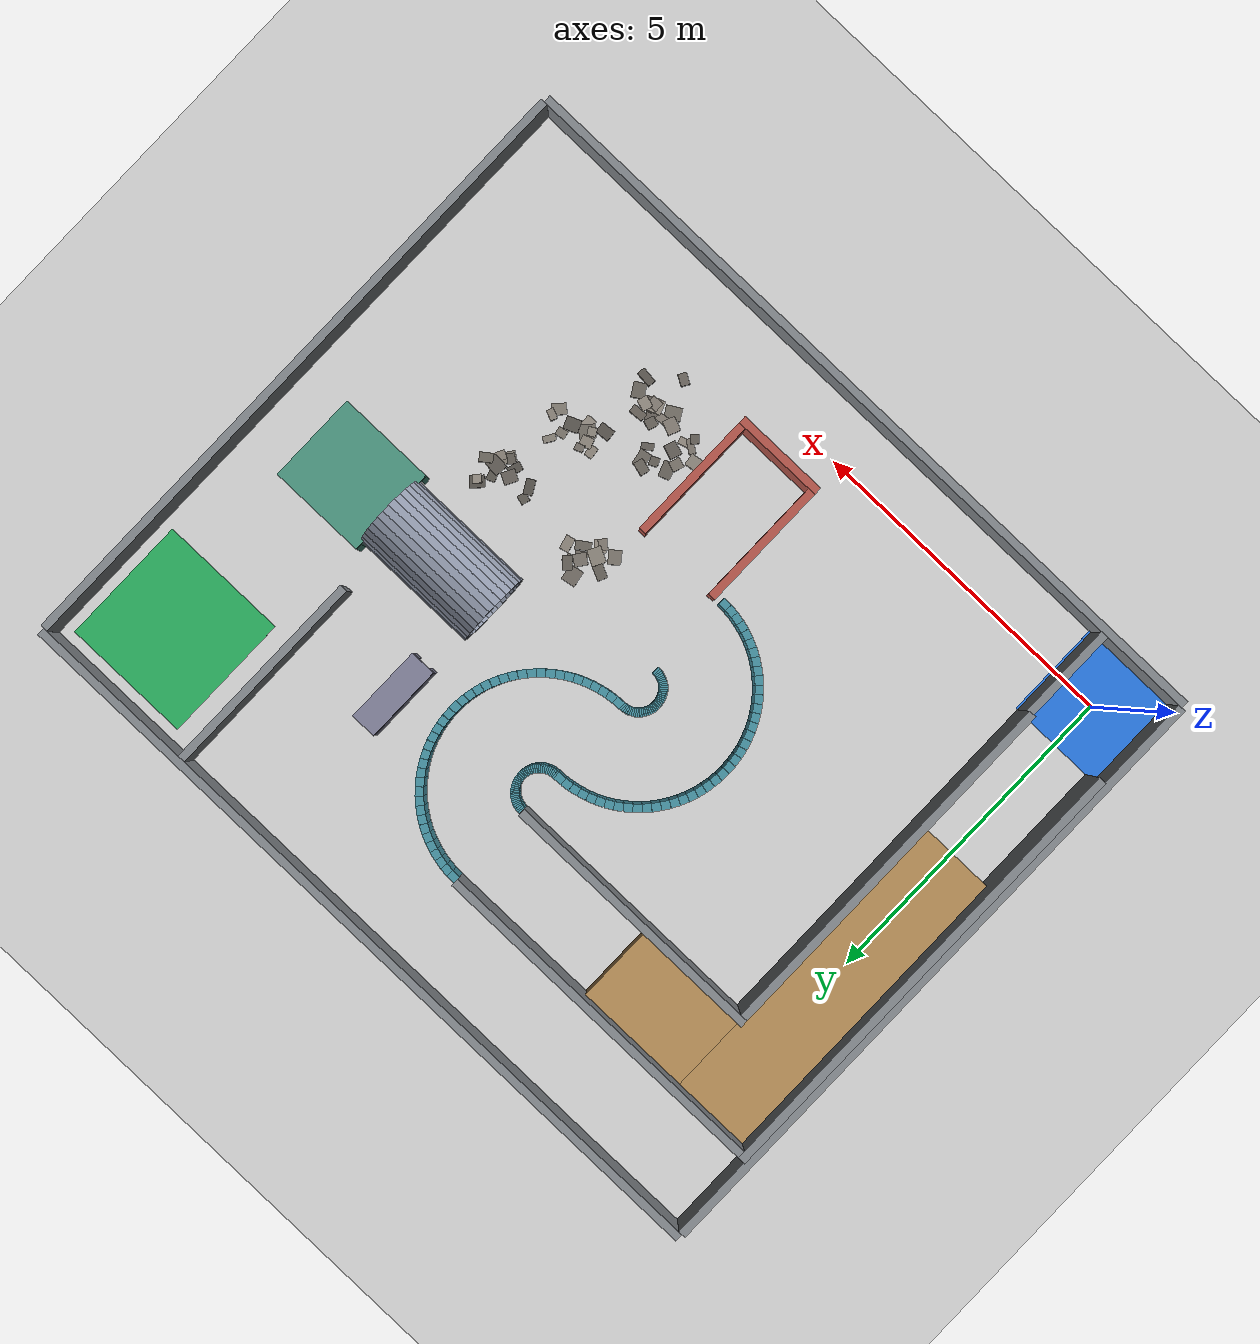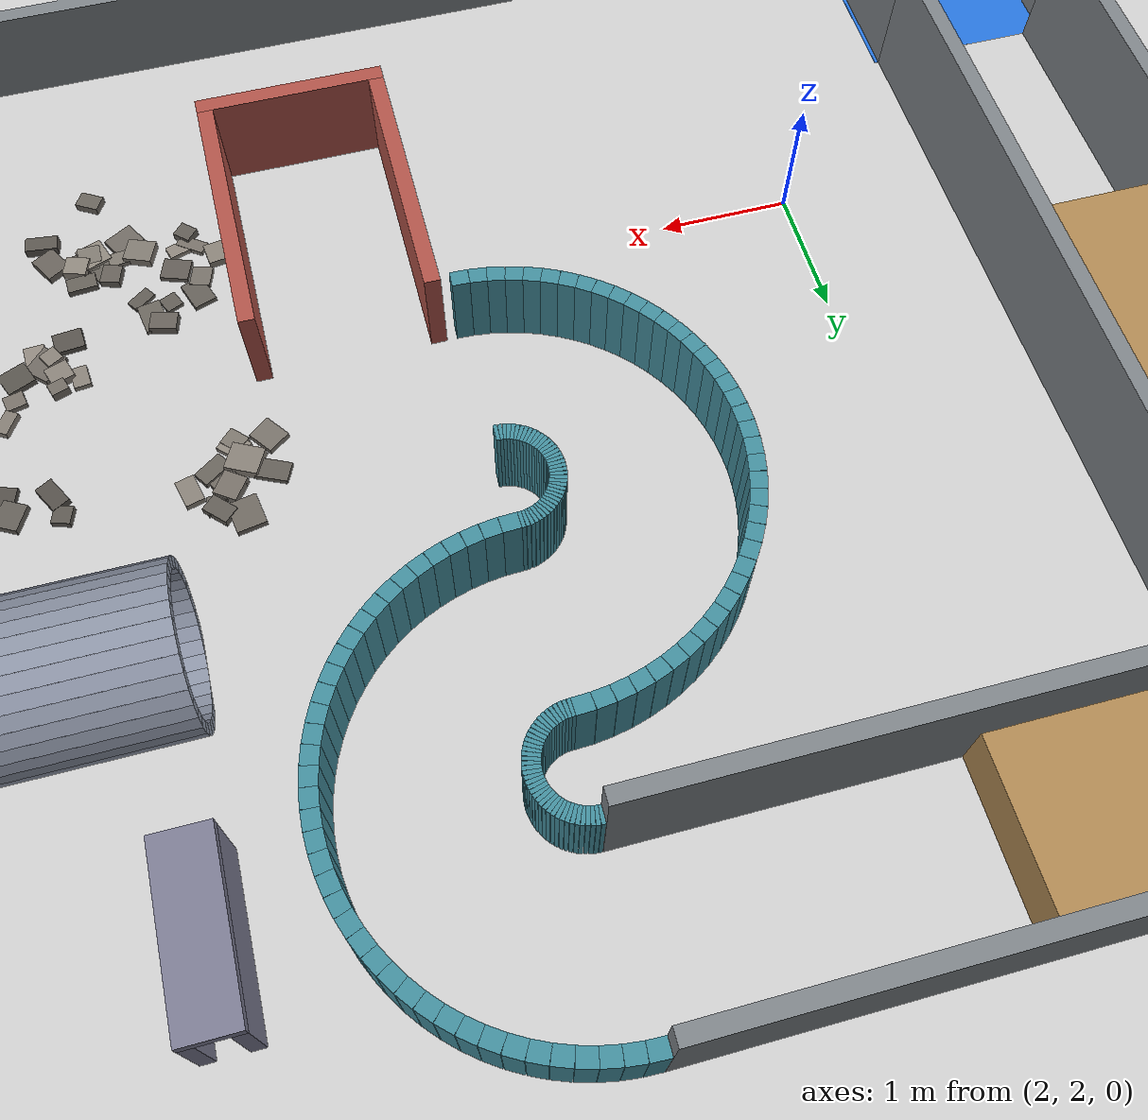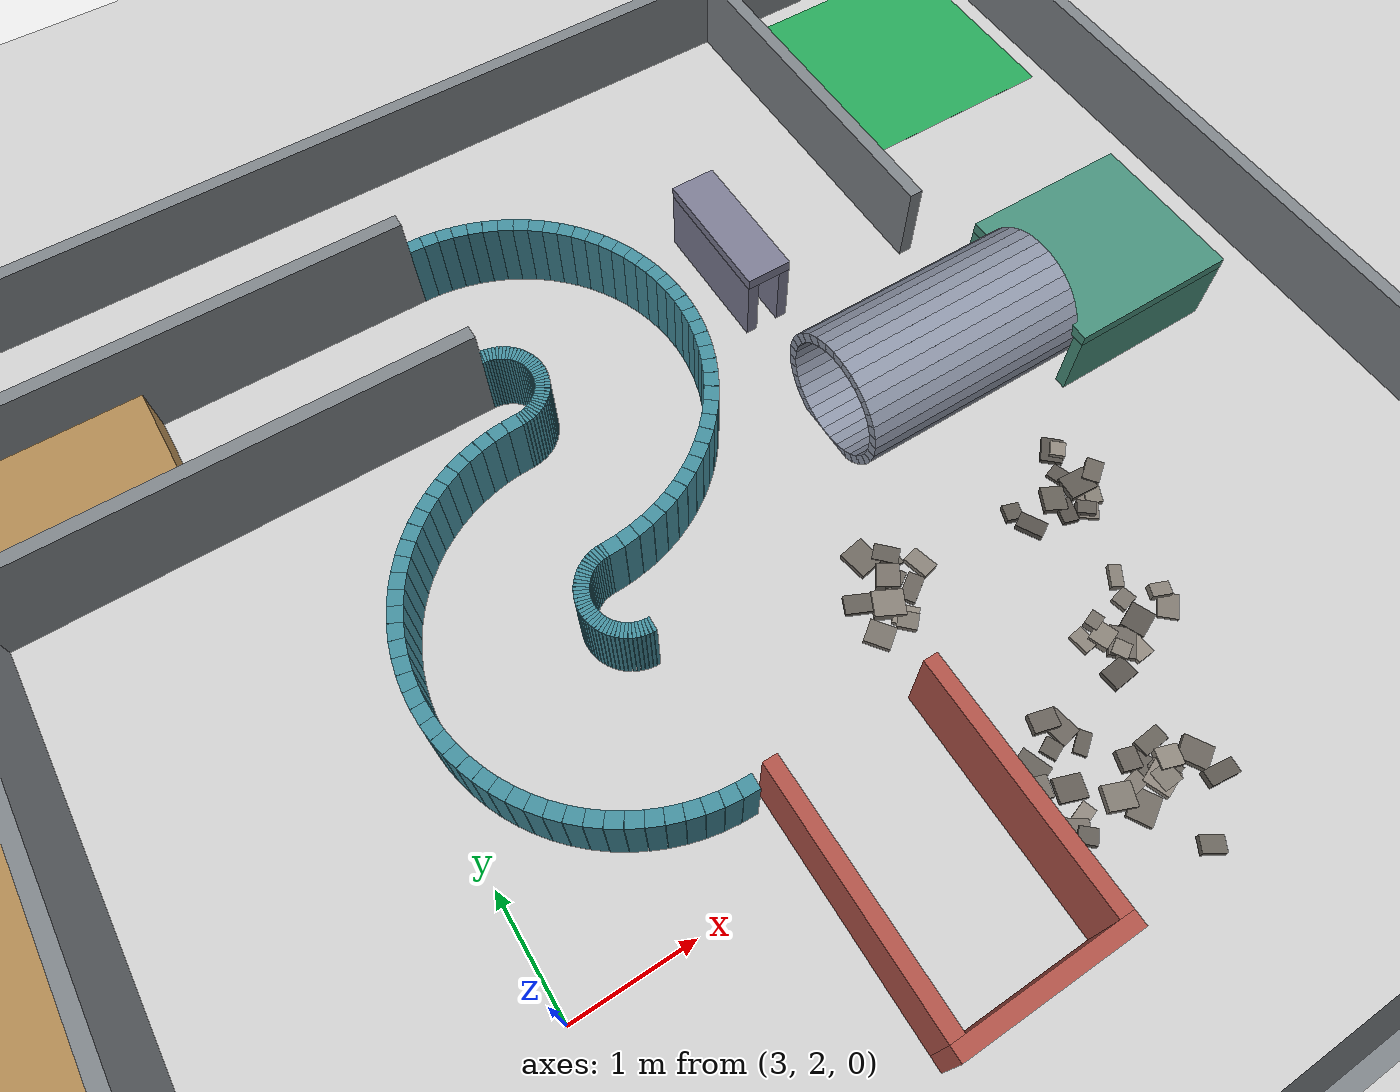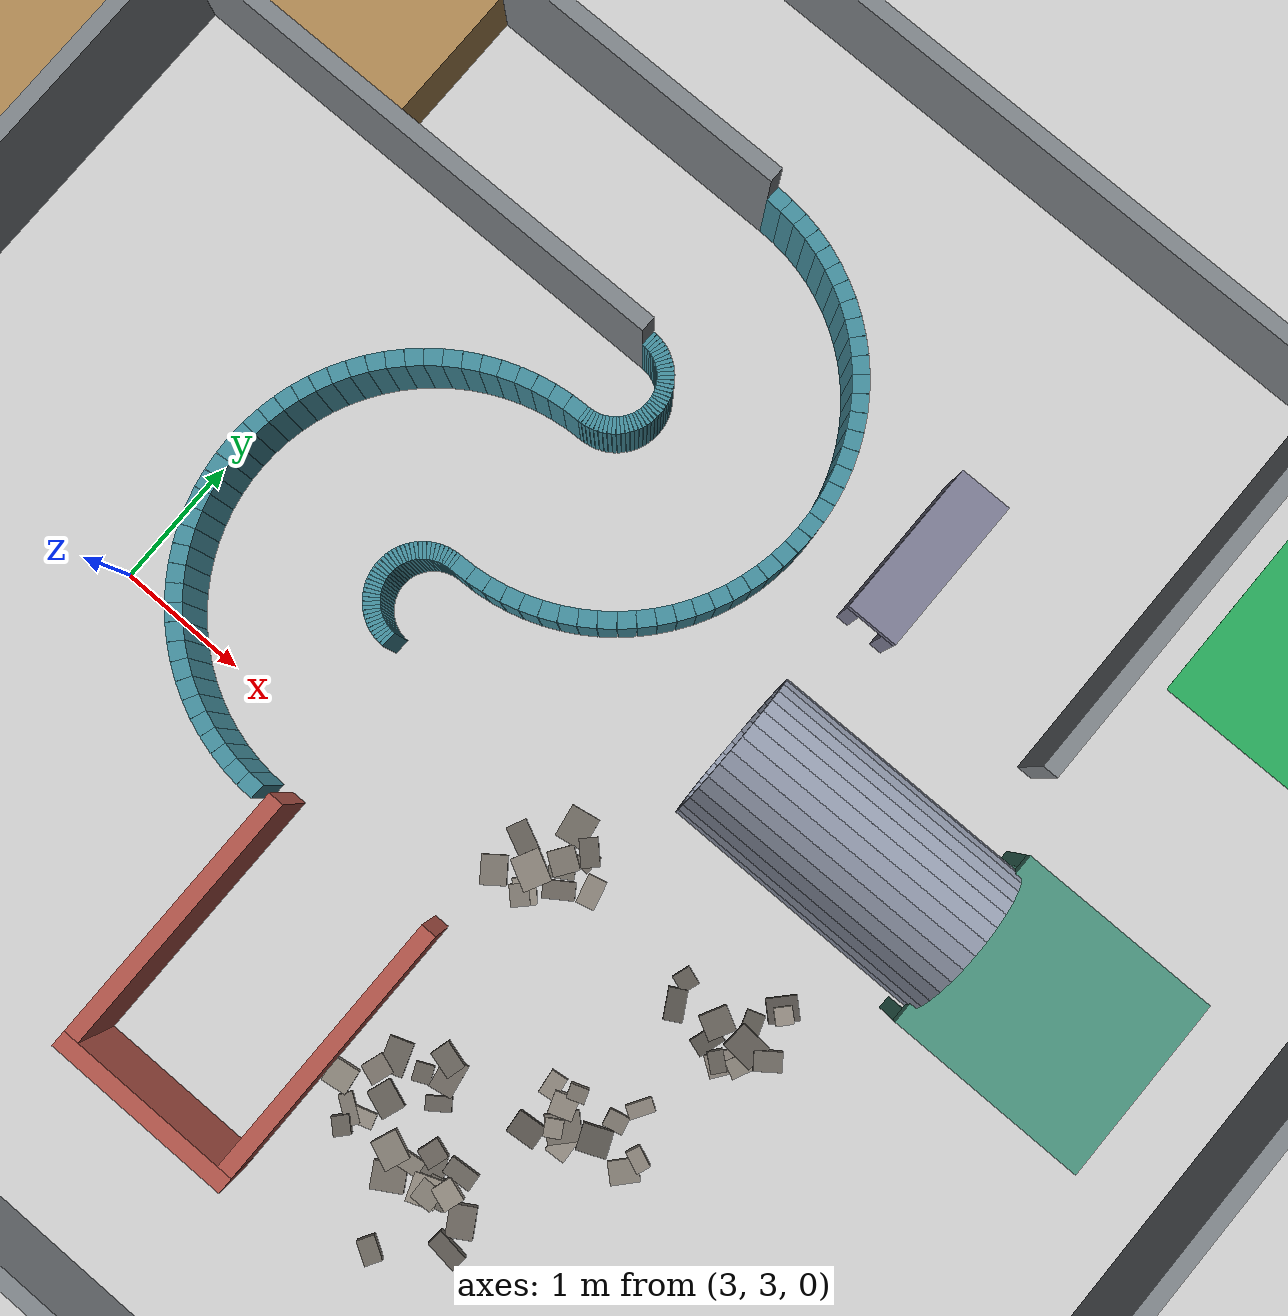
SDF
<sdf version="1.6">
 <world name="competition_arena">
  <include><uri>model://sun</uri></include>
  <include><uri>model://ground_plane</uri></include>
  <physics name="default" type="ode">
   <max_step_size>0.001</max_step_size>
   <real_time_update_rate>1000</real_time_update_rate>
   <ode><solver><type>quick</type><iters>50</iters></solver></ode>
  </physics>
  <scene><ambient>0.72 0.72 0.72 1</ambient><background>0.80 0.85 0.90 1</background></scene>
  <model name="arena_boundary">
   <static>true</static>
   <link name="structure">
    <collision name="south_collision">
     <pose>5.25 -0.81 0.375 0 0 0</pose>
     <geometry><box><size>12.12 0.12 0.75</size></box></geometry>
     <surface><friction><ode><mu>0.9</mu><mu2>0.9</mu2></ode></friction></surface>
    </collision>
    <visual name="south_visual">
     <pose>5.25 -0.81 0.375 0 0 0</pose>
     <geometry><box><size>12.12 0.12 0.75</size></box></geometry>
     <material><ambient>0.49 0.51 0.53 1</ambient><diffuse>0.49 0.51 0.53 1</diffuse></material>
    </visual>
    <collision name="north_collision">
     <pose>5.25 9.31 0.375 0 0 0</pose>
     <geometry><box><size>12.12 0.12 0.75</size></box></geometry>
     <surface><friction><ode><mu>0.9</mu><mu2>0.9</mu2></ode></friction></surface>
    </collision>
    <visual name="north_visual">
     <pose>5.25 9.31 0.375 0 0 0</pose>
     <geometry><box><size>12.12 0.12 0.75</size></box></geometry>
     <material><ambient>0.49 0.51 0.53 1</ambient><diffuse>0.49 0.51 0.53 1</diffuse></material>
    </visual>
    <collision name="west_collision">
     <pose>-0.81 4.25 0.375 0 0 1.5707963</pose>
     <geometry><box><size>10 0.12 0.75</size></box></geometry>
     <surface><friction><ode><mu>0.9</mu><mu2>0.9</mu2></ode></friction></surface>
    </collision>
    <visual name="west_visual">
     <pose>-0.81 4.25 0.375 0 0 1.5707963</pose>
     <geometry><box><size>10 0.12 0.75</size></box></geometry>
     <material><ambient>0.49 0.51 0.53 1</ambient><diffuse>0.49 0.51 0.53 1</diffuse></material>
    </visual>
    <collision name="east_collision">
     <pose>11.31 4.25 0.375 0 0 1.5707963</pose>
     <geometry><box><size>10 0.12 0.75</size></box></geometry>
     <surface><friction><ode><mu>0.9</mu><mu2>0.9</mu2></ode></friction></surface>
    </collision>
    <visual name="east_visual">
     <pose>11.31 4.25 0.375 0 0 1.5707963</pose>
     <geometry><box><size>10 0.12 0.75</size></box></geometry>
     <material><ambient>0.49 0.51 0.53 1</ambient><diffuse>0.49 0.51 0.53 1</diffuse></material>
    </visual>
   </link>
  </model>
  <model name="start_pad">
   <static>true</static>
   <link name="structure">
    <visual name="mark_visual">
     <pose>0 0 0.001 0 0 0</pose>
     <geometry><box><size>1.5 1.5 0.002</size></box></geometry>
     <material><ambient>0.15 0.45 0.85 1</ambient><diffuse>0.15 0.45 0.85 1</diffuse></material>
    </visual>
   </link>
  </model>
  <model name="finish_pad">
   <static>true</static>
   <link name="structure">
    <visual name="mark_visual">
     <pose>10.1 8.1 0.001 0 0 0</pose>
     <geometry><box><size>2 2 0.002</size></box></geometry>
     <material><ambient>0.15 0.65 0.35 1</ambient><diffuse>0.15 0.65 0.35 1</diffuse></material>
    </visual>
   </link>
  </model>
  <model name="slope_turn_platform">
   <static>true</static>
   <link name="structure">
    <collision name="long_deck_collision">
     <pose>0 5.3335418 0.225 0 0 0</pose>
     <geometry><box><size>1.2 4.9329165 0.45</size></box></geometry>
     <surface><friction><ode><mu>0.9</mu><mu2>0.9</mu2></ode></friction></surface>
    </collision>
    <visual name="long_deck_visual">
     <pose>0 5.3335418 0.225 0 0 0</pose>
     <geometry><box><size>1.2 4.9329165 0.45</size></box></geometry>
     <material><ambient>0.68 0.53 0.32 1</ambient><diffuse>0.68 0.53 0.32 1</diffuse></material>
    </visual>
    <collision name="cross_deck_collision">
     <pose>1.2 7.2 0.225 0 0 0</pose>
     <geometry><box><size>2.4 1.2 0.45</size></box></geometry>
     <surface><friction><ode><mu>0.9</mu><mu2>0.9</mu2></ode></friction></surface>
    </collision>
    <visual name="cross_deck_visual">
     <pose>1.2 7.2 0.225 0 0 0</pose>
     <geometry><box><size>2.4 1.2 0.45</size></box></geometry>
     <material><ambient>0.68 0.53 0.32 1</ambient><diffuse>0.68 0.53 0.32 1</diffuse></material>
    </visual>
   </link>
  </model>
  <model name="slope_guard_walls">
   <static>true</static>
   <link name="structure">
    <collision name="inner_collision">
     <pose>0.66 3.615 0.5 0 0 1.5707963</pose>
     <geometry><box><size>5.73 0.12 1</size></box></geometry>
     <surface><friction><ode><mu>0.9</mu><mu2>0.9</mu2></ode></friction></surface>
    </collision>
    <visual name="inner_visual">
     <pose>0.66 3.615 0.5 0 0 1.5707963</pose>
     <geometry><box><size>5.73 0.12 1</size></box></geometry>
     <material><ambient>0.49 0.51 0.53 1</ambient><diffuse>0.49 0.51 0.53 1</diffuse></material>
    </visual>
    <collision name="outer_collision">
     <pose>-0.66 4.335 0.5 0 0 1.5707963</pose>
     <geometry><box><size>7.17 0.12 1</size></box></geometry>
     <surface><friction><ode><mu>0.9</mu><mu2>0.9</mu2></ode></friction></surface>
    </collision>
    <visual name="outer_visual">
     <pose>-0.66 4.335 0.5 0 0 1.5707963</pose>
     <geometry><box><size>7.17 0.12 1</size></box></geometry>
     <material><ambient>0.49 0.51 0.53 1</ambient><diffuse>0.49 0.51 0.53 1</diffuse></material>
    </visual>
    <collision name="north_collision">
     <pose>2.1 7.86 0.5 0 0 0</pose>
     <geometry><box><size>5.4 0.12 1</size></box></geometry>
     <surface><friction><ode><mu>0.9</mu><mu2>0.9</mu2></ode></friction></surface>
    </collision>
    <visual name="north_visual">
     <pose>2.1 7.86 0.5 0 0 0</pose>
     <geometry><box><size>5.4 0.12 1</size></box></geometry>
     <material><ambient>0.49 0.51 0.53 1</ambient><diffuse>0.49 0.51 0.53 1</diffuse></material>
    </visual>
    <collision name="south_collision">
     <pose>2.7 6.54 0.5 0 0 0</pose>
     <geometry><box><size>4.2 0.12 1</size></box></geometry>
     <surface><friction><ode><mu>0.9</mu><mu2>0.9</mu2></ode></friction></surface>
    </collision>
    <visual name="south_visual">
     <pose>2.7 6.54 0.5 0 0 0</pose>
     <geometry><box><size>4.2 0.12 1</size></box></geometry>
     <material><ambient>0.49 0.51 0.53 1</ambient><diffuse>0.49 0.51 0.53 1</diffuse></material>
    </visual>
   </link>
  </model>
  <model name="start_entry_partition">
   <static>true</static>
   <link name="structure">
    <collision name="east_gate_collision">
     <pose>0.66 0 0.375 0 0 1.5707963</pose>
     <geometry><box><size>1.5 0.12 0.75</size></box></geometry>
     <surface><friction><ode><mu>0.9</mu><mu2>0.9</mu2></ode></friction></surface>
    </collision>
    <visual name="east_gate_visual">
     <pose>0.66 0 0.375 0 0 1.5707963</pose>
     <geometry><box><size>1.5 0.12 0.75</size></box></geometry>
     <material><ambient>0.49 0.51 0.53 1</ambient><diffuse>0.49 0.51 0.53 1</diffuse></material>
    </visual>
   </link>
  </model>
  <model name="s_bend_walls">
   <static>true</static>
   <link name="structure">
    <collision name="arc0_side-1_00_collision">
     <pose>4.813338 6.5394759 0.325 0 0 -0.039269908</pose>
     <geometry><box><size>0.027696675 0.12 0.65</size></box></geometry>
     <surface><friction><ode><mu>0.9</mu><mu2>0.9</mu2></ode></friction></surface>
    </collision>
    <visual name="arc0_side-1_00_visual">
     <pose>4.813338 6.5394759 0.325 0 0 -0.039269908</pose>
     <geometry><box><size>0.027696675 0.12 0.65</size></box></geometry>
     <material><ambient>0.26 0.55 0.61 1</ambient><diffuse>0.26 0.55 0.61 1</diffuse></material>
    </visual>
    <collision name="arc0_side-1_01_collision">
     <pose>4.8399319 6.537383 0.325 0 0 -0.11780972</pose>
     <geometry><box><size>0.027696675 0.12 0.65</size></box></geometry>
     <surface><friction><ode><mu>0.9</mu><mu2>0.9</mu2></ode></friction></surface>
    </collision>
    <visual name="arc0_side-1_01_visual">
     <pose>4.8399319 6.537383 0.325 0 0 -0.11780972</pose>
     <geometry><box><size>0.027696675 0.12 0.65</size></box></geometry>
     <material><ambient>0.26 0.55 0.61 1</ambient><diffuse>0.26 0.55 0.61 1</diffuse></material>
    </visual>
    <collision name="arc0_side-1_02_collision">
     <pose>4.8662796 6.5332099 0.325 0 0 -0.19634954</pose>
     <geometry><box><size>0.027696675 0.12 0.65</size></box></geometry>
     <surface><friction><ode><mu>0.9</mu><mu2>0.9</mu2></ode></friction></surface>
    </collision>
    <visual name="arc0_side-1_02_visual">
     <pose>4.8662796 6.5332099 0.325 0 0 -0.19634954</pose>
     <geometry><box><size>0.027696675 0.12 0.65</size></box></geometry>
     <material><ambient>0.26 0.55 0.61 1</ambient><diffuse>0.26 0.55 0.61 1</diffuse></material>
    </visual>
    <collision name="arc0_side-1_03_collision">
     <pose>4.8922186 6.5269825 0.325 0 0 -0.27488936</pose>
     <geometry><box><size>0.027696675 0.12 0.65</size></box></geometry>
     <surface><friction><ode><mu>0.9</mu><mu2>0.9</mu2></ode></friction></surface>
    </collision>
    <visual name="arc0_side-1_03_visual">
     <pose>4.8922186 6.5269825 0.325 0 0 -0.27488936</pose>
     <geometry><box><size>0.027696675 0.12 0.65</size></box></geometry>
     <material><ambient>0.26 0.55 0.61 1</ambient><diffuse>0.26 0.55 0.61 1</diffuse></material>
    </visual>
    <collision name="arc0_side-1_04_collision">
     <pose>4.9175891 6.5187391 0.325 0 0 -0.35342917</pose>
     <geometry><box><size>0.027696675 0.12 0.65</size></box></geometry>
     <surface><friction><ode><mu>0.9</mu><mu2>0.9</mu2></ode></friction></surface>
    </collision>
    <visual name="arc0_side-1_04_visual">
     <pose>4.9175891 6.5187391 0.325 0 0 -0.35342917</pose>
     <geometry><box><size>0.027696675 0.12 0.65</size></box></geometry>
     <material><ambient>0.26 0.55 0.61 1</ambient><diffuse>0.26 0.55 0.61 1</diffuse></material>
    </visual>
    <collision name="arc0_side-1_05_collision">
     <pose>4.9422346 6.5085306 0.325 0 0 -0.43196899</pose>
     <geometry><box><size>0.027696675 0.12 0.65</size></box></geometry>
     <surface><friction><ode><mu>0.9</mu><mu2>0.9</mu2></ode></friction></surface>
    </collision>
    <visual name="arc0_side-1_05_visual">
     <pose>4.9422346 6.5085306 0.325 0 0 -0.43196899</pose>
     <geometry><box><size>0.027696675 0.12 0.65</size></box></geometry>
     <material><ambient>0.26 0.55 0.61 1</ambient><diffuse>0.26 0.55 0.61 1</diffuse></material>
    </visual>
    <collision name="arc0_side-1_06_collision">
     <pose>4.9660031 6.4964199 0.325 0 0 -0.51050881</pose>
     <geometry><box><size>0.027696675 0.12 0.65</size></box></geometry>
     <surface><friction><ode><mu>0.9</mu><mu2>0.9</mu2></ode></friction></surface>
    </collision>
    <visual name="arc0_side-1_06_visual">
     <pose>4.9660031 6.4964199 0.325 0 0 -0.51050881</pose>
     <geometry><box><size>0.027696675 0.12 0.65</size></box></geometry>
     <material><ambient>0.26 0.55 0.61 1</ambient><diffuse>0.26 0.55 0.61 1</diffuse></material>
    </visual>
    <collision name="arc0_side-1_07_collision">
     <pose>4.9887482 6.4824817 0.325 0 0 -0.58904862</pose>
     <geometry><box><size>0.027696675 0.12 0.65</size></box></geometry>
     <surface><friction><ode><mu>0.9</mu><mu2>0.9</mu2></ode></friction></surface>
    </collision>
    <visual name="arc0_side-1_07_visual">
     <pose>4.9887482 6.4824817 0.325 0 0 -0.58904862</pose>
     <geometry><box><size>0.027696675 0.12 0.65</size></box></geometry>
     <material><ambient>0.26 0.55 0.61 1</ambient><diffuse>0.26 0.55 0.61 1</diffuse></material>
    </visual>
    <collision name="arc0_side-1_08_collision">
     <pose>5.0103297 6.4668019 0.325 0 0 -0.66758844</pose>
     <geometry><box><size>0.027696675 0.12 0.65</size></box></geometry>
     <surface><friction><ode><mu>0.9</mu><mu2>0.9</mu2></ode></friction></surface>
    </collision>
    <visual name="arc0_side-1_08_visual">
     <pose>5.0103297 6.4668019 0.325 0 0 -0.66758844</pose>
     <geometry><box><size>0.027696675 0.12 0.65</size></box></geometry>
     <material><ambient>0.26 0.55 0.61 1</ambient><diffuse>0.26 0.55 0.61 1</diffuse></material>
    </visual>
    <collision name="arc0_side-1_09_collision">
     <pose>5.0306143 6.4494772 0.325 0 0 -0.74612826</pose>
     <geometry><box><size>0.027696675 0.12 0.65</size></box></geometry>
     <surface><friction><ode><mu>0.9</mu><mu2>0.9</mu2></ode></friction></surface>
    </collision>
    <visual name="arc0_side-1_09_visual">
     <pose>5.0306143 6.4494772 0.325 0 0 -0.74612826</pose>
     <geometry><box><size>0.027696675 0.12 0.65</size></box></geometry>
     <material><ambient>0.26 0.55 0.61 1</ambient><diffuse>0.26 0.55 0.61 1</diffuse></material>
    </visual>
    <collision name="arc0_side-1_10_collision">
     <pose>5.0494772 6.4306143 0.325 0 0 -0.82466807</pose>
     <geometry><box><size>0.027696675 0.12 0.65</size></box></geometry>
     <surface><friction><ode><mu>0.9</mu><mu2>0.9</mu2></ode></friction></surface>
    </collision>
    <visual name="arc0_side-1_10_visual">
     <pose>5.0494772 6.4306143 0.325 0 0 -0.82466807</pose>
     <geometry><box><size>0.027696675 0.12 0.65</size></box></geometry>
     <material><ambient>0.26 0.55 0.61 1</ambient><diffuse>0.26 0.55 0.61 1</diffuse></material>
    </visual>
    <collision name="arc0_side-1_11_collision">
     <pose>5.0668019 6.4103297 0.325 0 0 -0.90320789</pose>
     <geometry><box><size>0.027696675 0.12 0.65</size></box></geometry>
     <surface><friction><ode><mu>0.9</mu><mu2>0.9</mu2></ode></friction></surface>
    </collision>
    <visual name="arc0_side-1_11_visual">
     <pose>5.0668019 6.4103297 0.325 0 0 -0.90320789</pose>
     <geometry><box><size>0.027696675 0.12 0.65</size></box></geometry>
     <material><ambient>0.26 0.55 0.61 1</ambient><diffuse>0.26 0.55 0.61 1</diffuse></material>
    </visual>
    <collision name="arc0_side-1_12_collision">
     <pose>5.0824817 6.3887482 0.325 0 0 -0.9817477</pose>
     <geometry><box><size>0.027696675 0.12 0.65</size></box></geometry>
     <surface><friction><ode><mu>0.9</mu><mu2>0.9</mu2></ode></friction></surface>
    </collision>
    <visual name="arc0_side-1_12_visual">
     <pose>5.0824817 6.3887482 0.325 0 0 -0.9817477</pose>
     <geometry><box><size>0.027696675 0.12 0.65</size></box></geometry>
     <material><ambient>0.26 0.55 0.61 1</ambient><diffuse>0.26 0.55 0.61 1</diffuse></material>
    </visual>
    <collision name="arc0_side-1_13_collision">
     <pose>5.0964199 6.3660031 0.325 0 0 -1.0602875</pose>
     <geometry><box><size>0.027696675 0.12 0.65</size></box></geometry>
     <surface><friction><ode><mu>0.9</mu><mu2>0.9</mu2></ode></friction></surface>
    </collision>
    <visual name="arc0_side-1_13_visual">
     <pose>5.0964199 6.3660031 0.325 0 0 -1.0602875</pose>
     <geometry><box><size>0.027696675 0.12 0.65</size></box></geometry>
     <material><ambient>0.26 0.55 0.61 1</ambient><diffuse>0.26 0.55 0.61 1</diffuse></material>
    </visual>
    <collision name="arc0_side-1_14_collision">
     <pose>5.1085306 6.3422346 0.325 0 0 -1.1388273</pose>
     <geometry><box><size>0.027696675 0.12 0.65</size></box></geometry>
     <surface><friction><ode><mu>0.9</mu><mu2>0.9</mu2></ode></friction></surface>
    </collision>
    <visual name="arc0_side-1_14_visual">
     <pose>5.1085306 6.3422346 0.325 0 0 -1.1388273</pose>
     <geometry><box><size>0.027696675 0.12 0.65</size></box></geometry>
     <material><ambient>0.26 0.55 0.61 1</ambient><diffuse>0.26 0.55 0.61 1</diffuse></material>
    </visual>
    <collision name="arc0_side-1_15_collision">
     <pose>5.1187391 6.3175891 0.325 0 0 -1.2173672</pose>
     <geometry><box><size>0.027696675 0.12 0.65</size></box></geometry>
     <surface><friction><ode><mu>0.9</mu><mu2>0.9</mu2></ode></friction></surface>
    </collision>
    <visual name="arc0_side-1_15_visual">
     <pose>5.1187391 6.3175891 0.325 0 0 -1.2173672</pose>
     <geometry><box><size>0.027696675 0.12 0.65</size></box></geometry>
     <material><ambient>0.26 0.55 0.61 1</ambient><diffuse>0.26 0.55 0.61 1</diffuse></material>
    </visual>
    <collision name="arc0_side-1_16_collision">
     <pose>5.1269825 6.2922186 0.325 0 0 -1.295907</pose>
     <geometry><box><size>0.027696675 0.12 0.65</size></box></geometry>
     <surface><friction><ode><mu>0.9</mu><mu2>0.9</mu2></ode></friction></surface>
    </collision>
    <visual name="arc0_side-1_16_visual">
     <pose>5.1269825 6.2922186 0.325 0 0 -1.295907</pose>
     <geometry><box><size>0.027696675 0.12 0.65</size></box></geometry>
     <material><ambient>0.26 0.55 0.61 1</ambient><diffuse>0.26 0.55 0.61 1</diffuse></material>
    </visual>
    <collision name="arc0_side-1_17_collision">
     <pose>5.1332099 6.2662796 0.325 0 0 -1.3744468</pose>
     <geometry><box><size>0.027696675 0.12 0.65</size></box></geometry>
     <surface><friction><ode><mu>0.9</mu><mu2>0.9</mu2></ode></friction></surface>
    </collision>
    <visual name="arc0_side-1_17_visual">
     <pose>5.1332099 6.2662796 0.325 0 0 -1.3744468</pose>
     <geometry><box><size>0.027696675 0.12 0.65</size></box></geometry>
     <material><ambient>0.26 0.55 0.61 1</ambient><diffuse>0.26 0.55 0.61 1</diffuse></material>
    </visual>
    <collision name="arc0_side-1_18_collision">
     <pose>5.137383 6.2399319 0.325 0 0 -1.4529866</pose>
     <geometry><box><size>0.027696675 0.12 0.65</size></box></geometry>
     <surface><friction><ode><mu>0.9</mu><mu2>0.9</mu2></ode></friction></surface>
    </collision>
    <visual name="arc0_side-1_18_visual">
     <pose>5.137383 6.2399319 0.325 0 0 -1.4529866</pose>
     <geometry><box><size>0.027696675 0.12 0.65</size></box></geometry>
     <material><ambient>0.26 0.55 0.61 1</ambient><diffuse>0.26 0.55 0.61 1</diffuse></material>
    </visual>
    <collision name="arc0_side-1_19_collision">
     <pose>5.1394759 6.213338 0.325 0 0 -1.5315264</pose>
     <geometry><box><size>0.027696675 0.12 0.65</size></box></geometry>
     <surface><friction><ode><mu>0.9</mu><mu2>0.9</mu2></ode></friction></surface>
    </collision>
    <visual name="arc0_side-1_19_visual">
     <pose>5.1394759 6.213338 0.325 0 0 -1.5315264</pose>
     <geometry><box><size>0.027696675 0.12 0.65</size></box></geometry>
     <material><ambient>0.26 0.55 0.61 1</ambient><diffuse>0.26 0.55 0.61 1</diffuse></material>
    </visual>
    <collision name="arc0_side-1_20_collision">
     <pose>5.1394759 6.186662 0.325 0 0 -1.6100662</pose>
     <geometry><box><size>0.027696675 0.12 0.65</size></box></geometry>
     <surface><friction><ode><mu>0.9</mu><mu2>0.9</mu2></ode></friction></surface>
    </collision>
    <visual name="arc0_side-1_20_visual">
     <pose>5.1394759 6.186662 0.325 0 0 -1.6100662</pose>
     <geometry><box><size>0.027696675 0.12 0.65</size></box></geometry>
     <material><ambient>0.26 0.55 0.61 1</ambient><diffuse>0.26 0.55 0.61 1</diffuse></material>
    </visual>
    <collision name="arc0_side-1_21_collision">
     <pose>5.137383 6.1600681 0.325 0 0 -1.6886061</pose>
     <geometry><box><size>0.027696675 0.12 0.65</size></box></geometry>
     <surface><friction><ode><mu>0.9</mu><mu2>0.9</mu2></ode></friction></surface>
    </collision>
    <visual name="arc0_side-1_21_visual">
     <pose>5.137383 6.1600681 0.325 0 0 -1.6886061</pose>
     <geometry><box><size>0.027696675 0.12 0.65</size></box></geometry>
     <material><ambient>0.26 0.55 0.61 1</ambient><diffuse>0.26 0.55 0.61 1</diffuse></material>
    </visual>
    <collision name="arc0_side-1_22_collision">
     <pose>5.1332099 6.1337204 0.325 0 0 -1.7671459</pose>
     <geometry><box><size>0.027696675 0.12 0.65</size></box></geometry>
     <surface><friction><ode><mu>0.9</mu><mu2>0.9</mu2></ode></friction></surface>
    </collision>
    <visual name="arc0_side-1_22_visual">
     <pose>5.1332099 6.1337204 0.325 0 0 -1.7671459</pose>
     <geometry><box><size>0.027696675 0.12 0.65</size></box></geometry>
     <material><ambient>0.26 0.55 0.61 1</ambient><diffuse>0.26 0.55 0.61 1</diffuse></material>
    </visual>
    <collision name="arc0_side-1_23_collision">
     <pose>5.1269825 6.1077814 0.325 0 0 -1.8456857</pose>
     <geometry><box><size>0.027696675 0.12 0.65</size></box></geometry>
     <surface><friction><ode><mu>0.9</mu><mu2>0.9</mu2></ode></friction></surface>
    </collision>
    <visual name="arc0_side-1_23_visual">
     <pose>5.1269825 6.1077814 0.325 0 0 -1.8456857</pose>
     <geometry><box><size>0.027696675 0.12 0.65</size></box></geometry>
     <material><ambient>0.26 0.55 0.61 1</ambient><diffuse>0.26 0.55 0.61 1</diffuse></material>
    </visual>
    <collision name="arc0_side-1_24_collision">
     <pose>5.1187391 6.0824109 0.325 0 0 -1.9242255</pose>
     <geometry><box><size>0.027696675 0.12 0.65</size></box></geometry>
     <surface><friction><ode><mu>0.9</mu><mu2>0.9</mu2></ode></friction></surface>
    </collision>
    <visual name="arc0_side-1_24_visual">
     <pose>5.1187391 6.0824109 0.325 0 0 -1.9242255</pose>
     <geometry><box><size>0.027696675 0.12 0.65</size></box></geometry>
     <material><ambient>0.26 0.55 0.61 1</ambient><diffuse>0.26 0.55 0.61 1</diffuse></material>
    </visual>
    <collision name="arc0_side-1_25_collision">
     <pose>5.1085306 6.0577654 0.325 0 0 -2.0027653</pose>
     <geometry><box><size>0.027696675 0.12 0.65</size></box></geometry>
     <surface><friction><ode><mu>0.9</mu><mu2>0.9</mu2></ode></friction></surface>
    </collision>
    <visual name="arc0_side-1_25_visual">
     <pose>5.1085306 6.0577654 0.325 0 0 -2.0027653</pose>
     <geometry><box><size>0.027696675 0.12 0.65</size></box></geometry>
     <material><ambient>0.26 0.55 0.61 1</ambient><diffuse>0.26 0.55 0.61 1</diffuse></material>
    </visual>
    <collision name="arc0_side-1_26_collision">
     <pose>5.0964199 6.0339969 0.325 0 0 -2.0813051</pose>
     <geometry><box><size>0.027696675 0.12 0.65</size></box></geometry>
     <surface><friction><ode><mu>0.9</mu><mu2>0.9</mu2></ode></friction></surface>
    </collision>
    <visual name="arc0_side-1_26_visual">
     <pose>5.0964199 6.0339969 0.325 0 0 -2.0813051</pose>
     <geometry><box><size>0.027696675 0.12 0.65</size></box></geometry>
     <material><ambient>0.26 0.55 0.61 1</ambient><diffuse>0.26 0.55 0.61 1</diffuse></material>
    </visual>
    <collision name="arc0_side-1_27_collision">
     <pose>5.0824817 6.0112518 0.325 0 0 -2.1598449</pose>
     <geometry><box><size>0.027696675 0.12 0.65</size></box></geometry>
     <surface><friction><ode><mu>0.9</mu><mu2>0.9</mu2></ode></friction></surface>
    </collision>
    <visual name="arc0_side-1_27_visual">
     <pose>5.0824817 6.0112518 0.325 0 0 -2.1598449</pose>
     <geometry><box><size>0.027696675 0.12 0.65</size></box></geometry>
     <material><ambient>0.26 0.55 0.61 1</ambient><diffuse>0.26 0.55 0.61 1</diffuse></material>
    </visual>
    <collision name="arc0_side-1_28_collision">
     <pose>5.0668019 5.9896703 0.325 0 0 -2.2383848</pose>
     <geometry><box><size>0.027696675 0.12 0.65</size></box></geometry>
     <surface><friction><ode><mu>0.9</mu><mu2>0.9</mu2></ode></friction></surface>
    </collision>
    <visual name="arc0_side-1_28_visual">
     <pose>5.0668019 5.9896703 0.325 0 0 -2.2383848</pose>
     <geometry><box><size>0.027696675 0.12 0.65</size></box></geometry>
     <material><ambient>0.26 0.55 0.61 1</ambient><diffuse>0.26 0.55 0.61 1</diffuse></material>
    </visual>
    <collision name="arc0_side-1_29_collision">
     <pose>5.0494772 5.9693857 0.325 0 0 -2.3169246</pose>
     <geometry><box><size>0.027696675 0.12 0.65</size></box></geometry>
     <surface><friction><ode><mu>0.9</mu><mu2>0.9</mu2></ode></friction></surface>
    </collision>
    <visual name="arc0_side-1_29_visual">
     <pose>5.0494772 5.9693857 0.325 0 0 -2.3169246</pose>
     <geometry><box><size>0.027696675 0.12 0.65</size></box></geometry>
     <material><ambient>0.26 0.55 0.61 1</ambient><diffuse>0.26 0.55 0.61 1</diffuse></material>
    </visual>
    <collision name="arc0_side-1_30_collision">
     <pose>5.0306143 5.9505228 0.325 0 0 -2.3954644</pose>
     <geometry><box><size>0.027696675 0.12 0.65</size></box></geometry>
     <surface><friction><ode><mu>0.9</mu><mu2>0.9</mu2></ode></friction></surface>
    </collision>
    <visual name="arc0_side-1_30_visual">
     <pose>5.0306143 5.9505228 0.325 0 0 -2.3954644</pose>
     <geometry><box><size>0.027696675 0.12 0.65</size></box></geometry>
     <material><ambient>0.26 0.55 0.61 1</ambient><diffuse>0.26 0.55 0.61 1</diffuse></material>
    </visual>
    <collision name="arc0_side-1_31_collision">
     <pose>5.0103297 5.9331981 0.325 0 0 -2.4740042</pose>
     <geometry><box><size>0.027696675 0.12 0.65</size></box></geometry>
     <surface><friction><ode><mu>0.9</mu><mu2>0.9</mu2></ode></friction></surface>
    </collision>
    <visual name="arc0_side-1_31_visual">
     <pose>5.0103297 5.9331981 0.325 0 0 -2.4740042</pose>
     <geometry><box><size>0.027696675 0.12 0.65</size></box></geometry>
     <material><ambient>0.26 0.55 0.61 1</ambient><diffuse>0.26 0.55 0.61 1</diffuse></material>
    </visual>
    <collision name="arc0_side-1_32_collision">
     <pose>4.9887482 5.9175183 0.325 0 0 -2.552544</pose>
     <geometry><box><size>0.027696675 0.12 0.65</size></box></geometry>
     <surface><friction><ode><mu>0.9</mu><mu2>0.9</mu2></ode></friction></surface>
    </collision>
    <visual name="arc0_side-1_32_visual">
     <pose>4.9887482 5.9175183 0.325 0 0 -2.552544</pose>
     <geometry><box><size>0.027696675 0.12 0.65</size></box></geometry>
     <material><ambient>0.26 0.55 0.61 1</ambient><diffuse>0.26 0.55 0.61 1</diffuse></material>
    </visual>
    <collision name="arc0_side-1_33_collision">
     <pose>4.9660031 5.9035801 0.325 0 0 -2.6310838</pose>
     <geometry><box><size>0.027696675 0.12 0.65</size></box></geometry>
     <surface><friction><ode><mu>0.9</mu><mu2>0.9</mu2></ode></friction></surface>
    </collision>
    <visual name="arc0_side-1_33_visual">
     <pose>4.9660031 5.9035801 0.325 0 0 -2.6310838</pose>
     <geometry><box><size>0.027696675 0.12 0.65</size></box></geometry>
     <material><ambient>0.26 0.55 0.61 1</ambient><diffuse>0.26 0.55 0.61 1</diffuse></material>
    </visual>
    <collision name="arc0_side-1_34_collision">
     <pose>4.9422346 5.8914694 0.325 0 0 -2.7096237</pose>
     <geometry><box><size>0.027696675 0.12 0.65</size></box></geometry>
     <surface><friction><ode><mu>0.9</mu><mu2>0.9</mu2></ode></friction></surface>
    </collision>
    <visual name="arc0_side-1_34_visual">
     <pose>4.9422346 5.8914694 0.325 0 0 -2.7096237</pose>
     <geometry><box><size>0.027696675 0.12 0.65</size></box></geometry>
     <material><ambient>0.26 0.55 0.61 1</ambient><diffuse>0.26 0.55 0.61 1</diffuse></material>
    </visual>
    <collision name="arc0_side-1_35_collision">
     <pose>4.9175891 5.8812609 0.325 0 0 -2.7881635</pose>
     <geometry><box><size>0.027696675 0.12 0.65</size></box></geometry>
     <surface><friction><ode><mu>0.9</mu><mu2>0.9</mu2></ode></friction></surface>
    </collision>
    <visual name="arc0_side-1_35_visual">
     <pose>4.9175891 5.8812609 0.325 0 0 -2.7881635</pose>
     <geometry><box><size>0.027696675 0.12 0.65</size></box></geometry>
     <material><ambient>0.26 0.55 0.61 1</ambient><diffuse>0.26 0.55 0.61 1</diffuse></material>
    </visual>
    <collision name="arc0_side-1_36_collision">
     <pose>4.8922186 5.8730175 0.325 0 0 -2.8667033</pose>
     <geometry><box><size>0.027696675 0.12 0.65</size></box></geometry>
     <surface><friction><ode><mu>0.9</mu><mu2>0.9</mu2></ode></friction></surface>
    </collision>
    <visual name="arc0_side-1_36_visual">
     <pose>4.8922186 5.8730175 0.325 0 0 -2.8667033</pose>
     <geometry><box><size>0.027696675 0.12 0.65</size></box></geometry>
     <material><ambient>0.26 0.55 0.61 1</ambient><diffuse>0.26 0.55 0.61 1</diffuse></material>
    </visual>
    <collision name="arc0_side-1_37_collision">
     <pose>4.8662796 5.8667901 0.325 0 0 -2.9452431</pose>
     <geometry><box><size>0.027696675 0.12 0.65</size></box></geometry>
     <surface><friction><ode><mu>0.9</mu><mu2>0.9</mu2></ode></friction></surface>
    </collision>
    <visual name="arc0_side-1_37_visual">
     <pose>4.8662796 5.8667901 0.325 0 0 -2.9452431</pose>
     <geometry><box><size>0.027696675 0.12 0.65</size></box></geometry>
     <material><ambient>0.26 0.55 0.61 1</ambient><diffuse>0.26 0.55 0.61 1</diffuse></material>
    </visual>
    <collision name="arc0_side-1_38_collision">
     <pose>4.8399319 5.862617 0.325 0 0 -3.0237829</pose>
     <geometry><box><size>0.027696675 0.12 0.65</size></box></geometry>
     <surface><friction><ode><mu>0.9</mu><mu2>0.9</mu2></ode></friction></surface>
    </collision>
    <visual name="arc0_side-1_38_visual">
     <pose>4.8399319 5.862617 0.325 0 0 -3.0237829</pose>
     <geometry><box><size>0.027696675 0.12 0.65</size></box></geometry>
     <material><ambient>0.26 0.55 0.61 1</ambient><diffuse>0.26 0.55 0.61 1</diffuse></material>
    </visual>
    <collision name="arc0_side-1_39_collision">
     <pose>4.813338 5.8605241 0.325 0 0 -3.1023227</pose>
     <geometry><box><size>0.027696675 0.12 0.65</size></box></geometry>
     <surface><friction><ode><mu>0.9</mu><mu2>0.9</mu2></ode></friction></surface>
    </collision>
    <visual name="arc0_side-1_39_visual">
     <pose>4.813338 5.8605241 0.325 0 0 -3.1023227</pose>
     <geometry><box><size>0.027696675 0.12 0.65</size></box></geometry>
     <material><ambient>0.26 0.55 0.61 1</ambient><diffuse>0.26 0.55 0.61 1</diffuse></material>
    </visual>
    <collision name="arc0_side1_00_collision">
     <pose>4.865121 7.8574414 0.325 0 0 -0.039269908</pose>
     <geometry><box><size>0.13134259 0.12 0.65</size></box></geometry>
     <surface><friction><ode><mu>0.9</mu><mu2>0.9</mu2></ode></friction></surface>
    </collision>
    <visual name="arc0_side1_00_visual">
     <pose>4.865121 7.8574414 0.325 0 0 -0.039269908</pose>
     <geometry><box><size>0.13134259 0.12 0.65</size></box></geometry>
     <material><ambient>0.26 0.55 0.61 1</ambient><diffuse>0.26 0.55 0.61 1</diffuse></material>
    </visual>
    <collision name="arc0_side1_01_collision">
     <pose>4.9949617 7.8472227 0.325 0 0 -0.11780972</pose>
     <geometry><box><size>0.13134259 0.12 0.65</size></box></geometry>
     <surface><friction><ode><mu>0.9</mu><mu2>0.9</mu2></ode></friction></surface>
    </collision>
    <visual name="arc0_side1_01_visual">
     <pose>4.9949617 7.8472227 0.325 0 0 -0.11780972</pose>
     <geometry><box><size>0.13134259 0.12 0.65</size></box></geometry>
     <material><ambient>0.26 0.55 0.61 1</ambient><diffuse>0.26 0.55 0.61 1</diffuse></material>
    </visual>
    <collision name="arc0_side1_02_collision">
     <pose>5.1236003 7.8268484 0.325 0 0 -0.19634954</pose>
     <geometry><box><size>0.13134259 0.12 0.65</size></box></geometry>
     <surface><friction><ode><mu>0.9</mu><mu2>0.9</mu2></ode></friction></surface>
    </collision>
    <visual name="arc0_side1_02_visual">
     <pose>5.1236003 7.8268484 0.325 0 0 -0.19634954</pose>
     <geometry><box><size>0.13134259 0.12 0.65</size></box></geometry>
     <material><ambient>0.26 0.55 0.61 1</ambient><diffuse>0.26 0.55 0.61 1</diffuse></material>
    </visual>
    <collision name="arc0_side1_03_collision">
     <pose>5.2502438 7.7964439 0.325 0 0 -0.27488936</pose>
     <geometry><box><size>0.13134259 0.12 0.65</size></box></geometry>
     <surface><friction><ode><mu>0.9</mu><mu2>0.9</mu2></ode></friction></surface>
    </collision>
    <visual name="arc0_side1_03_visual">
     <pose>5.2502438 7.7964439 0.325 0 0 -0.27488936</pose>
     <geometry><box><size>0.13134259 0.12 0.65</size></box></geometry>
     <material><ambient>0.26 0.55 0.61 1</ambient><diffuse>0.26 0.55 0.61 1</diffuse></material>
    </visual>
    <collision name="arc0_side1_04_collision">
     <pose>5.3741114 7.7561969 0.325 0 0 -0.35342917</pose>
     <geometry><box><size>0.13134259 0.12 0.65</size></box></geometry>
     <surface><friction><ode><mu>0.9</mu><mu2>0.9</mu2></ode></friction></surface>
    </collision>
    <visual name="arc0_side1_04_visual">
     <pose>5.3741114 7.7561969 0.325 0 0 -0.35342917</pose>
     <geometry><box><size>0.13134259 0.12 0.65</size></box></geometry>
     <material><ambient>0.26 0.55 0.61 1</ambient><diffuse>0.26 0.55 0.61 1</diffuse></material>
    </visual>
    <collision name="arc0_side1_05_collision">
     <pose>5.4944394 7.7063554 0.325 0 0 -0.43196899</pose>
     <geometry><box><size>0.13134259 0.12 0.65</size></box></geometry>
     <surface><friction><ode><mu>0.9</mu><mu2>0.9</mu2></ode></friction></surface>
    </collision>
    <visual name="arc0_side1_05_visual">
     <pose>5.4944394 7.7063554 0.325 0 0 -0.43196899</pose>
     <geometry><box><size>0.13134259 0.12 0.65</size></box></geometry>
     <material><ambient>0.26 0.55 0.61 1</ambient><diffuse>0.26 0.55 0.61 1</diffuse></material>
    </visual>
    <collision name="arc0_side1_06_collision">
     <pose>5.6104859 7.6472268 0.325 0 0 -0.51050881</pose>
     <geometry><box><size>0.13134259 0.12 0.65</size></box></geometry>
     <surface><friction><ode><mu>0.9</mu><mu2>0.9</mu2></ode></friction></surface>
    </collision>
    <visual name="arc0_side1_06_visual">
     <pose>5.6104859 7.6472268 0.325 0 0 -0.51050881</pose>
     <geometry><box><size>0.13134259 0.12 0.65</size></box></geometry>
     <material><ambient>0.26 0.55 0.61 1</ambient><diffuse>0.26 0.55 0.61 1</diffuse></material>
    </visual>
    <collision name="arc0_side1_07_collision">
     <pose>5.7215356 7.5791754 0.325 0 0 -0.58904862</pose>
     <geometry><box><size>0.13134259 0.12 0.65</size></box></geometry>
     <surface><friction><ode><mu>0.9</mu><mu2>0.9</mu2></ode></friction></surface>
    </collision>
    <visual name="arc0_side1_07_visual">
     <pose>5.7215356 7.5791754 0.325 0 0 -0.58904862</pose>
     <geometry><box><size>0.13134259 0.12 0.65</size></box></geometry>
     <material><ambient>0.26 0.55 0.61 1</ambient><diffuse>0.26 0.55 0.61 1</diffuse></material>
    </visual>
    <collision name="arc0_side1_08_collision">
     <pose>5.8269036 7.5026211 0.325 0 0 -0.66758844</pose>
     <geometry><box><size>0.13134259 0.12 0.65</size></box></geometry>
     <surface><friction><ode><mu>0.9</mu><mu2>0.9</mu2></ode></friction></surface>
    </collision>
    <visual name="arc0_side1_08_visual">
     <pose>5.8269036 7.5026211 0.325 0 0 -0.66758844</pose>
     <geometry><box><size>0.13134259 0.12 0.65</size></box></geometry>
     <material><ambient>0.26 0.55 0.61 1</ambient><diffuse>0.26 0.55 0.61 1</diffuse></material>
    </visual>
    <collision name="arc0_side1_09_collision">
     <pose>5.9259405 7.4180356 0.325 0 0 -0.74612826</pose>
     <geometry><box><size>0.13134259 0.12 0.65</size></box></geometry>
     <surface><friction><ode><mu>0.9</mu><mu2>0.9</mu2></ode></friction></surface>
    </collision>
    <visual name="arc0_side1_09_visual">
     <pose>5.9259405 7.4180356 0.325 0 0 -0.74612826</pose>
     <geometry><box><size>0.13134259 0.12 0.65</size></box></geometry>
     <material><ambient>0.26 0.55 0.61 1</ambient><diffuse>0.26 0.55 0.61 1</diffuse></material>
    </visual>
    <collision name="arc0_side1_10_collision">
     <pose>6.0180356 7.3259405 0.325 0 0 -0.82466807</pose>
     <geometry><box><size>0.13134259 0.12 0.65</size></box></geometry>
     <surface><friction><ode><mu>0.9</mu><mu2>0.9</mu2></ode></friction></surface>
    </collision>
    <visual name="arc0_side1_10_visual">
     <pose>6.0180356 7.3259405 0.325 0 0 -0.82466807</pose>
     <geometry><box><size>0.13134259 0.12 0.65</size></box></geometry>
     <material><ambient>0.26 0.55 0.61 1</ambient><diffuse>0.26 0.55 0.61 1</diffuse></material>
    </visual>
    <collision name="arc0_side1_11_collision">
     <pose>6.1026211 7.2269036 0.325 0 0 -0.90320789</pose>
     <geometry><box><size>0.13134259 0.12 0.65</size></box></geometry>
     <surface><friction><ode><mu>0.9</mu><mu2>0.9</mu2></ode></friction></surface>
    </collision>
    <visual name="arc0_side1_11_visual">
     <pose>6.1026211 7.2269036 0.325 0 0 -0.90320789</pose>
     <geometry><box><size>0.13134259 0.12 0.65</size></box></geometry>
     <material><ambient>0.26 0.55 0.61 1</ambient><diffuse>0.26 0.55 0.61 1</diffuse></material>
    </visual>
    <collision name="arc0_side1_12_collision">
     <pose>6.1791754 7.1215356 0.325 0 0 -0.9817477</pose>
     <geometry><box><size>0.13134259 0.12 0.65</size></box></geometry>
     <surface><friction><ode><mu>0.9</mu><mu2>0.9</mu2></ode></friction></surface>
    </collision>
    <visual name="arc0_side1_12_visual">
     <pose>6.1791754 7.1215356 0.325 0 0 -0.9817477</pose>
     <geometry><box><size>0.13134259 0.12 0.65</size></box></geometry>
     <material><ambient>0.26 0.55 0.61 1</ambient><diffuse>0.26 0.55 0.61 1</diffuse></material>
    </visual>
    <collision name="arc0_side1_13_collision">
     <pose>6.2472268 7.0104859 0.325 0 0 -1.0602875</pose>
     <geometry><box><size>0.13134259 0.12 0.65</size></box></geometry>
     <surface><friction><ode><mu>0.9</mu><mu2>0.9</mu2></ode></friction></surface>
    </collision>
    <visual name="arc0_side1_13_visual">
     <pose>6.2472268 7.0104859 0.325 0 0 -1.0602875</pose>
     <geometry><box><size>0.13134259 0.12 0.65</size></box></geometry>
     <material><ambient>0.26 0.55 0.61 1</ambient><diffuse>0.26 0.55 0.61 1</diffuse></material>
    </visual>
    <collision name="arc0_side1_14_collision">
     <pose>6.3063554 6.8944394 0.325 0 0 -1.1388273</pose>
     <geometry><box><size>0.13134259 0.12 0.65</size></box></geometry>
     <surface><friction><ode><mu>0.9</mu><mu2>0.9</mu2></ode></friction></surface>
    </collision>
    <visual name="arc0_side1_14_visual">
     <pose>6.3063554 6.8944394 0.325 0 0 -1.1388273</pose>
     <geometry><box><size>0.13134259 0.12 0.65</size></box></geometry>
     <material><ambient>0.26 0.55 0.61 1</ambient><diffuse>0.26 0.55 0.61 1</diffuse></material>
    </visual>
    <collision name="arc0_side1_15_collision">
     <pose>6.3561969 6.7741114 0.325 0 0 -1.2173672</pose>
     <geometry><box><size>0.13134259 0.12 0.65</size></box></geometry>
     <surface><friction><ode><mu>0.9</mu><mu2>0.9</mu2></ode></friction></surface>
    </collision>
    <visual name="arc0_side1_15_visual">
     <pose>6.3561969 6.7741114 0.325 0 0 -1.2173672</pose>
     <geometry><box><size>0.13134259 0.12 0.65</size></box></geometry>
     <material><ambient>0.26 0.55 0.61 1</ambient><diffuse>0.26 0.55 0.61 1</diffuse></material>
    </visual>
    <collision name="arc0_side1_16_collision">
     <pose>6.3964439 6.6502438 0.325 0 0 -1.295907</pose>
     <geometry><box><size>0.13134259 0.12 0.65</size></box></geometry>
     <surface><friction><ode><mu>0.9</mu><mu2>0.9</mu2></ode></friction></surface>
    </collision>
    <visual name="arc0_side1_16_visual">
     <pose>6.3964439 6.6502438 0.325 0 0 -1.295907</pose>
     <geometry><box><size>0.13134259 0.12 0.65</size></box></geometry>
     <material><ambient>0.26 0.55 0.61 1</ambient><diffuse>0.26 0.55 0.61 1</diffuse></material>
    </visual>
    <collision name="arc0_side1_17_collision">
     <pose>6.4268484 6.5236003 0.325 0 0 -1.3744468</pose>
     <geometry><box><size>0.13134259 0.12 0.65</size></box></geometry>
     <surface><friction><ode><mu>0.9</mu><mu2>0.9</mu2></ode></friction></surface>
    </collision>
    <visual name="arc0_side1_17_visual">
     <pose>6.4268484 6.5236003 0.325 0 0 -1.3744468</pose>
     <geometry><box><size>0.13134259 0.12 0.65</size></box></geometry>
     <material><ambient>0.26 0.55 0.61 1</ambient><diffuse>0.26 0.55 0.61 1</diffuse></material>
    </visual>
    <collision name="arc0_side1_18_collision">
     <pose>6.4472227 6.3949617 0.325 0 0 -1.4529866</pose>
     <geometry><box><size>0.13134259 0.12 0.65</size></box></geometry>
     <surface><friction><ode><mu>0.9</mu><mu2>0.9</mu2></ode></friction></surface>
    </collision>
    <visual name="arc0_side1_18_visual">
     <pose>6.4472227 6.3949617 0.325 0 0 -1.4529866</pose>
     <geometry><box><size>0.13134259 0.12 0.65</size></box></geometry>
     <material><ambient>0.26 0.55 0.61 1</ambient><diffuse>0.26 0.55 0.61 1</diffuse></material>
    </visual>
    <collision name="arc0_side1_19_collision">
     <pose>6.4574414 6.265121 0.325 0 0 -1.5315264</pose>
     <geometry><box><size>0.13134259 0.12 0.65</size></box></geometry>
     <surface><friction><ode><mu>0.9</mu><mu2>0.9</mu2></ode></friction></surface>
    </collision>
    <visual name="arc0_side1_19_visual">
     <pose>6.4574414 6.265121 0.325 0 0 -1.5315264</pose>
     <geometry><box><size>0.13134259 0.12 0.65</size></box></geometry>
     <material><ambient>0.26 0.55 0.61 1</ambient><diffuse>0.26 0.55 0.61 1</diffuse></material>
    </visual>
    <collision name="arc0_side1_20_collision">
     <pose>6.4574414 6.134879 0.325 0 0 -1.6100662</pose>
     <geometry><box><size>0.13134259 0.12 0.65</size></box></geometry>
     <surface><friction><ode><mu>0.9</mu><mu2>0.9</mu2></ode></friction></surface>
    </collision>
    <visual name="arc0_side1_20_visual">
     <pose>6.4574414 6.134879 0.325 0 0 -1.6100662</pose>
     <geometry><box><size>0.13134259 0.12 0.65</size></box></geometry>
     <material><ambient>0.26 0.55 0.61 1</ambient><diffuse>0.26 0.55 0.61 1</diffuse></material>
    </visual>
    <collision name="arc0_side1_21_collision">
     <pose>6.4472227 6.0050383 0.325 0 0 -1.6886061</pose>
     <geometry><box><size>0.13134259 0.12 0.65</size></box></geometry>
     <surface><friction><ode><mu>0.9</mu><mu2>0.9</mu2></ode></friction></surface>
    </collision>
    <visual name="arc0_side1_21_visual">
     <pose>6.4472227 6.0050383 0.325 0 0 -1.6886061</pose>
     <geometry><box><size>0.13134259 0.12 0.65</size></box></geometry>
     <material><ambient>0.26 0.55 0.61 1</ambient><diffuse>0.26 0.55 0.61 1</diffuse></material>
    </visual>
    <collision name="arc0_side1_22_collision">
     <pose>6.4268484 5.8763997 0.325 0 0 -1.7671459</pose>
     <geometry><box><size>0.13134259 0.12 0.65</size></box></geometry>
     <surface><friction><ode><mu>0.9</mu><mu2>0.9</mu2></ode></friction></surface>
    </collision>
    <visual name="arc0_side1_22_visual">
     <pose>6.4268484 5.8763997 0.325 0 0 -1.7671459</pose>
     <geometry><box><size>0.13134259 0.12 0.65</size></box></geometry>
     <material><ambient>0.26 0.55 0.61 1</ambient><diffuse>0.26 0.55 0.61 1</diffuse></material>
    </visual>
    <collision name="arc0_side1_23_collision">
     <pose>6.3964439 5.7497562 0.325 0 0 -1.8456857</pose>
     <geometry><box><size>0.13134259 0.12 0.65</size></box></geometry>
     <surface><friction><ode><mu>0.9</mu><mu2>0.9</mu2></ode></friction></surface>
    </collision>
    <visual name="arc0_side1_23_visual">
     <pose>6.3964439 5.7497562 0.325 0 0 -1.8456857</pose>
     <geometry><box><size>0.13134259 0.12 0.65</size></box></geometry>
     <material><ambient>0.26 0.55 0.61 1</ambient><diffuse>0.26 0.55 0.61 1</diffuse></material>
    </visual>
    <collision name="arc0_side1_24_collision">
     <pose>6.3561969 5.6258886 0.325 0 0 -1.9242255</pose>
     <geometry><box><size>0.13134259 0.12 0.65</size></box></geometry>
     <surface><friction><ode><mu>0.9</mu><mu2>0.9</mu2></ode></friction></surface>
    </collision>
    <visual name="arc0_side1_24_visual">
     <pose>6.3561969 5.6258886 0.325 0 0 -1.9242255</pose>
     <geometry><box><size>0.13134259 0.12 0.65</size></box></geometry>
     <material><ambient>0.26 0.55 0.61 1</ambient><diffuse>0.26 0.55 0.61 1</diffuse></material>
    </visual>
    <collision name="arc0_side1_25_collision">
     <pose>6.3063554 5.5055606 0.325 0 0 -2.0027653</pose>
     <geometry><box><size>0.13134259 0.12 0.65</size></box></geometry>
     <surface><friction><ode><mu>0.9</mu><mu2>0.9</mu2></ode></friction></surface>
    </collision>
    <visual name="arc0_side1_25_visual">
     <pose>6.3063554 5.5055606 0.325 0 0 -2.0027653</pose>
     <geometry><box><size>0.13134259 0.12 0.65</size></box></geometry>
     <material><ambient>0.26 0.55 0.61 1</ambient><diffuse>0.26 0.55 0.61 1</diffuse></material>
    </visual>
    <collision name="arc0_side1_26_collision">
     <pose>6.2472268 5.3895141 0.325 0 0 -2.0813051</pose>
     <geometry><box><size>0.13134259 0.12 0.65</size></box></geometry>
     <surface><friction><ode><mu>0.9</mu><mu2>0.9</mu2></ode></friction></surface>
    </collision>
    <visual name="arc0_side1_26_visual">
     <pose>6.2472268 5.3895141 0.325 0 0 -2.0813051</pose>
     <geometry><box><size>0.13134259 0.12 0.65</size></box></geometry>
     <material><ambient>0.26 0.55 0.61 1</ambient><diffuse>0.26 0.55 0.61 1</diffuse></material>
    </visual>
    <collision name="arc0_side1_27_collision">
     <pose>6.1791754 5.2784644 0.325 0 0 -2.1598449</pose>
     <geometry><box><size>0.13134259 0.12 0.65</size></box></geometry>
     <surface><friction><ode><mu>0.9</mu><mu2>0.9</mu2></ode></friction></surface>
    </collision>
    <visual name="arc0_side1_27_visual">
     <pose>6.1791754 5.2784644 0.325 0 0 -2.1598449</pose>
     <geometry><box><size>0.13134259 0.12 0.65</size></box></geometry>
     <material><ambient>0.26 0.55 0.61 1</ambient><diffuse>0.26 0.55 0.61 1</diffuse></material>
    </visual>
    <collision name="arc0_side1_28_collision">
     <pose>6.1026211 5.1730964 0.325 0 0 -2.2383848</pose>
     <geometry><box><size>0.13134259 0.12 0.65</size></box></geometry>
     <surface><friction><ode><mu>0.9</mu><mu2>0.9</mu2></ode></friction></surface>
    </collision>
    <visual name="arc0_side1_28_visual">
     <pose>6.1026211 5.1730964 0.325 0 0 -2.2383848</pose>
     <geometry><box><size>0.13134259 0.12 0.65</size></box></geometry>
     <material><ambient>0.26 0.55 0.61 1</ambient><diffuse>0.26 0.55 0.61 1</diffuse></material>
    </visual>
    <collision name="arc0_side1_29_collision">
     <pose>6.0180356 5.0740595 0.325 0 0 -2.3169246</pose>
     <geometry><box><size>0.13134259 0.12 0.65</size></box></geometry>
     <surface><friction><ode><mu>0.9</mu><mu2>0.9</mu2></ode></friction></surface>
    </collision>
    <visual name="arc0_side1_29_visual">
     <pose>6.0180356 5.0740595 0.325 0 0 -2.3169246</pose>
     <geometry><box><size>0.13134259 0.12 0.65</size></box></geometry>
     <material><ambient>0.26 0.55 0.61 1</ambient><diffuse>0.26 0.55 0.61 1</diffuse></material>
    </visual>
    <collision name="arc0_side1_30_collision">
     <pose>5.9259405 4.9819644 0.325 0 0 -2.3954644</pose>
     <geometry><box><size>0.13134259 0.12 0.65</size></box></geometry>
     <surface><friction><ode><mu>0.9</mu><mu2>0.9</mu2></ode></friction></surface>
    </collision>
    <visual name="arc0_side1_30_visual">
     <pose>5.9259405 4.9819644 0.325 0 0 -2.3954644</pose>
     <geometry><box><size>0.13134259 0.12 0.65</size></box></geometry>
     <material><ambient>0.26 0.55 0.61 1</ambient><diffuse>0.26 0.55 0.61 1</diffuse></material>
    </visual>
    <collision name="arc0_side1_31_collision">
     <pose>5.8269036 4.8973789 0.325 0 0 -2.4740042</pose>
     <geometry><box><size>0.13134259 0.12 0.65</size></box></geometry>
     <surface><friction><ode><mu>0.9</mu><mu2>0.9</mu2></ode></friction></surface>
    </collision>
    <visual name="arc0_side1_31_visual">
     <pose>5.8269036 4.8973789 0.325 0 0 -2.4740042</pose>
     <geometry><box><size>0.13134259 0.12 0.65</size></box></geometry>
     <material><ambient>0.26 0.55 0.61 1</ambient><diffuse>0.26 0.55 0.61 1</diffuse></material>
    </visual>
    <collision name="arc0_side1_32_collision">
     <pose>5.7215356 4.8208246 0.325 0 0 -2.552544</pose>
     <geometry><box><size>0.13134259 0.12 0.65</size></box></geometry>
     <surface><friction><ode><mu>0.9</mu><mu2>0.9</mu2></ode></friction></surface>
    </collision>
    <visual name="arc0_side1_32_visual">
     <pose>5.7215356 4.8208246 0.325 0 0 -2.552544</pose>
     <geometry><box><size>0.13134259 0.12 0.65</size></box></geometry>
     <material><ambient>0.26 0.55 0.61 1</ambient><diffuse>0.26 0.55 0.61 1</diffuse></material>
    </visual>
    <collision name="arc0_side1_33_collision">
     <pose>5.6104859 4.7527732 0.325 0 0 -2.6310838</pose>
     <geometry><box><size>0.13134259 0.12 0.65</size></box></geometry>
     <surface><friction><ode><mu>0.9</mu><mu2>0.9</mu2></ode></friction></surface>
    </collision>
    <visual name="arc0_side1_33_visual">
     <pose>5.6104859 4.7527732 0.325 0 0 -2.6310838</pose>
     <geometry><box><size>0.13134259 0.12 0.65</size></box></geometry>
     <material><ambient>0.26 0.55 0.61 1</ambient><diffuse>0.26 0.55 0.61 1</diffuse></material>
    </visual>
    <collision name="arc0_side1_34_collision">
     <pose>5.4944394 4.6936446 0.325 0 0 -2.7096237</pose>
     <geometry><box><size>0.13134259 0.12 0.65</size></box></geometry>
     <surface><friction><ode><mu>0.9</mu><mu2>0.9</mu2></ode></friction></surface>
    </collision>
    <visual name="arc0_side1_34_visual">
     <pose>5.4944394 4.6936446 0.325 0 0 -2.7096237</pose>
     <geometry><box><size>0.13134259 0.12 0.65</size></box></geometry>
     <material><ambient>0.26 0.55 0.61 1</ambient><diffuse>0.26 0.55 0.61 1</diffuse></material>
    </visual>
    <collision name="arc0_side1_35_collision">
     <pose>5.3741114 4.6438031 0.325 0 0 -2.7881635</pose>
     <geometry><box><size>0.13134259 0.12 0.65</size></box></geometry>
     <surface><friction><ode><mu>0.9</mu><mu2>0.9</mu2></ode></friction></surface>
    </collision>
    <visual name="arc0_side1_35_visual">
     <pose>5.3741114 4.6438031 0.325 0 0 -2.7881635</pose>
     <geometry><box><size>0.13134259 0.12 0.65</size></box></geometry>
     <material><ambient>0.26 0.55 0.61 1</ambient><diffuse>0.26 0.55 0.61 1</diffuse></material>
    </visual>
    <collision name="arc0_side1_36_collision">
     <pose>5.2502438 4.6035561 0.325 0 0 -2.8667033</pose>
     <geometry><box><size>0.13134259 0.12 0.65</size></box></geometry>
     <surface><friction><ode><mu>0.9</mu><mu2>0.9</mu2></ode></friction></surface>
    </collision>
    <visual name="arc0_side1_36_visual">
     <pose>5.2502438 4.6035561 0.325 0 0 -2.8667033</pose>
     <geometry><box><size>0.13134259 0.12 0.65</size></box></geometry>
     <material><ambient>0.26 0.55 0.61 1</ambient><diffuse>0.26 0.55 0.61 1</diffuse></material>
    </visual>
    <collision name="arc0_side1_37_collision">
     <pose>5.1236003 4.5731516 0.325 0 0 -2.9452431</pose>
     <geometry><box><size>0.13134259 0.12 0.65</size></box></geometry>
     <surface><friction><ode><mu>0.9</mu><mu2>0.9</mu2></ode></friction></surface>
    </collision>
    <visual name="arc0_side1_37_visual">
     <pose>5.1236003 4.5731516 0.325 0 0 -2.9452431</pose>
     <geometry><box><size>0.13134259 0.12 0.65</size></box></geometry>
     <material><ambient>0.26 0.55 0.61 1</ambient><diffuse>0.26 0.55 0.61 1</diffuse></material>
    </visual>
    <collision name="arc0_side1_38_collision">
     <pose>4.9949617 4.5527773 0.325 0 0 -3.0237829</pose>
     <geometry><box><size>0.13134259 0.12 0.65</size></box></geometry>
     <surface><friction><ode><mu>0.9</mu><mu2>0.9</mu2></ode></friction></surface>
    </collision>
    <visual name="arc0_side1_38_visual">
     <pose>4.9949617 4.5527773 0.325 0 0 -3.0237829</pose>
     <geometry><box><size>0.13134259 0.12 0.65</size></box></geometry>
     <material><ambient>0.26 0.55 0.61 1</ambient><diffuse>0.26 0.55 0.61 1</diffuse></material>
    </visual>
    <collision name="arc0_side1_39_collision">
     <pose>4.865121 4.5425586 0.325 0 0 -3.1023227</pose>
     <geometry><box><size>0.13134259 0.12 0.65</size></box></geometry>
     <surface><friction><ode><mu>0.9</mu><mu2>0.9</mu2></ode></friction></surface>
    </collision>
    <visual name="arc0_side1_39_visual">
     <pose>4.865121 4.5425586 0.325 0 0 -3.1023227</pose>
     <geometry><box><size>0.13134259 0.12 0.65</size></box></geometry>
     <material><ambient>0.26 0.55 0.61 1</ambient><diffuse>0.26 0.55 0.61 1</diffuse></material>
    </visual>
    <collision name="arc1_side-1_00_collision">
     <pose>4.786662 4.5394759 0.325 0 0 -3.1023227</pose>
     <geometry><box><size>0.027696675 0.12 0.65</size></box></geometry>
     <surface><friction><ode><mu>0.9</mu><mu2>0.9</mu2></ode></friction></surface>
    </collision>
    <visual name="arc1_side-1_00_visual">
     <pose>4.786662 4.5394759 0.325 0 0 -3.1023227</pose>
     <geometry><box><size>0.027696675 0.12 0.65</size></box></geometry>
     <material><ambient>0.26 0.55 0.61 1</ambient><diffuse>0.26 0.55 0.61 1</diffuse></material>
    </visual>
    <collision name="arc1_side-1_01_collision">
     <pose>4.7600681 4.537383 0.325 0 0 -3.0237829</pose>
     <geometry><box><size>0.027696675 0.12 0.65</size></box></geometry>
     <surface><friction><ode><mu>0.9</mu><mu2>0.9</mu2></ode></friction></surface>
    </collision>
    <visual name="arc1_side-1_01_visual">
     <pose>4.7600681 4.537383 0.325 0 0 -3.0237829</pose>
     <geometry><box><size>0.027696675 0.12 0.65</size></box></geometry>
     <material><ambient>0.26 0.55 0.61 1</ambient><diffuse>0.26 0.55 0.61 1</diffuse></material>
    </visual>
    <collision name="arc1_side-1_02_collision">
     <pose>4.7337204 4.5332099 0.325 0 0 -2.9452431</pose>
     <geometry><box><size>0.027696675 0.12 0.65</size></box></geometry>
     <surface><friction><ode><mu>0.9</mu><mu2>0.9</mu2></ode></friction></surface>
    </collision>
    <visual name="arc1_side-1_02_visual">
     <pose>4.7337204 4.5332099 0.325 0 0 -2.9452431</pose>
     <geometry><box><size>0.027696675 0.12 0.65</size></box></geometry>
     <material><ambient>0.26 0.55 0.61 1</ambient><diffuse>0.26 0.55 0.61 1</diffuse></material>
    </visual>
    <collision name="arc1_side-1_03_collision">
     <pose>4.7077814 4.5269825 0.325 0 0 -2.8667033</pose>
     <geometry><box><size>0.027696675 0.12 0.65</size></box></geometry>
     <surface><friction><ode><mu>0.9</mu><mu2>0.9</mu2></ode></friction></surface>
    </collision>
    <visual name="arc1_side-1_03_visual">
     <pose>4.7077814 4.5269825 0.325 0 0 -2.8667033</pose>
     <geometry><box><size>0.027696675 0.12 0.65</size></box></geometry>
     <material><ambient>0.26 0.55 0.61 1</ambient><diffuse>0.26 0.55 0.61 1</diffuse></material>
    </visual>
    <collision name="arc1_side-1_04_collision">
     <pose>4.6824109 4.5187391 0.325 0 0 -2.7881635</pose>
     <geometry><box><size>0.027696675 0.12 0.65</size></box></geometry>
     <surface><friction><ode><mu>0.9</mu><mu2>0.9</mu2></ode></friction></surface>
    </collision>
    <visual name="arc1_side-1_04_visual">
     <pose>4.6824109 4.5187391 0.325 0 0 -2.7881635</pose>
     <geometry><box><size>0.027696675 0.12 0.65</size></box></geometry>
     <material><ambient>0.26 0.55 0.61 1</ambient><diffuse>0.26 0.55 0.61 1</diffuse></material>
    </visual>
    <collision name="arc1_side-1_05_collision">
     <pose>4.6577654 4.5085306 0.325 0 0 -2.7096237</pose>
     <geometry><box><size>0.027696675 0.12 0.65</size></box></geometry>
     <surface><friction><ode><mu>0.9</mu><mu2>0.9</mu2></ode></friction></surface>
    </collision>
    <visual name="arc1_side-1_05_visual">
     <pose>4.6577654 4.5085306 0.325 0 0 -2.7096237</pose>
     <geometry><box><size>0.027696675 0.12 0.65</size></box></geometry>
     <material><ambient>0.26 0.55 0.61 1</ambient><diffuse>0.26 0.55 0.61 1</diffuse></material>
    </visual>
    <collision name="arc1_side-1_06_collision">
     <pose>4.6339969 4.4964199 0.325 0 0 -2.6310838</pose>
     <geometry><box><size>0.027696675 0.12 0.65</size></box></geometry>
     <surface><friction><ode><mu>0.9</mu><mu2>0.9</mu2></ode></friction></surface>
    </collision>
    <visual name="arc1_side-1_06_visual">
     <pose>4.6339969 4.4964199 0.325 0 0 -2.6310838</pose>
     <geometry><box><size>0.027696675 0.12 0.65</size></box></geometry>
     <material><ambient>0.26 0.55 0.61 1</ambient><diffuse>0.26 0.55 0.61 1</diffuse></material>
    </visual>
    <collision name="arc1_side-1_07_collision">
     <pose>4.6112518 4.4824817 0.325 0 0 -2.552544</pose>
     <geometry><box><size>0.027696675 0.12 0.65</size></box></geometry>
     <surface><friction><ode><mu>0.9</mu><mu2>0.9</mu2></ode></friction></surface>
    </collision>
    <visual name="arc1_side-1_07_visual">
     <pose>4.6112518 4.4824817 0.325 0 0 -2.552544</pose>
     <geometry><box><size>0.027696675 0.12 0.65</size></box></geometry>
     <material><ambient>0.26 0.55 0.61 1</ambient><diffuse>0.26 0.55 0.61 1</diffuse></material>
    </visual>
    <collision name="arc1_side-1_08_collision">
     <pose>4.5896703 4.4668019 0.325 0 0 -2.4740042</pose>
     <geometry><box><size>0.027696675 0.12 0.65</size></box></geometry>
     <surface><friction><ode><mu>0.9</mu><mu2>0.9</mu2></ode></friction></surface>
    </collision>
    <visual name="arc1_side-1_08_visual">
     <pose>4.5896703 4.4668019 0.325 0 0 -2.4740042</pose>
     <geometry><box><size>0.027696675 0.12 0.65</size></box></geometry>
     <material><ambient>0.26 0.55 0.61 1</ambient><diffuse>0.26 0.55 0.61 1</diffuse></material>
    </visual>
    <collision name="arc1_side-1_09_collision">
     <pose>4.5693857 4.4494772 0.325 0 0 -2.3954644</pose>
     <geometry><box><size>0.027696675 0.12 0.65</size></box></geometry>
     <surface><friction><ode><mu>0.9</mu><mu2>0.9</mu2></ode></friction></surface>
    </collision>
    <visual name="arc1_side-1_09_visual">
     <pose>4.5693857 4.4494772 0.325 0 0 -2.3954644</pose>
     <geometry><box><size>0.027696675 0.12 0.65</size></box></geometry>
     <material><ambient>0.26 0.55 0.61 1</ambient><diffuse>0.26 0.55 0.61 1</diffuse></material>
    </visual>
    <collision name="arc1_side-1_10_collision">
     <pose>4.5505228 4.4306143 0.325 0 0 -2.3169246</pose>
     <geometry><box><size>0.027696675 0.12 0.65</size></box></geometry>
     <surface><friction><ode><mu>0.9</mu><mu2>0.9</mu2></ode></friction></surface>
    </collision>
    <visual name="arc1_side-1_10_visual">
     <pose>4.5505228 4.4306143 0.325 0 0 -2.3169246</pose>
     <geometry><box><size>0.027696675 0.12 0.65</size></box></geometry>
     <material><ambient>0.26 0.55 0.61 1</ambient><diffuse>0.26 0.55 0.61 1</diffuse></material>
    </visual>
    <collision name="arc1_side-1_11_collision">
     <pose>4.5331981 4.4103297 0.325 0 0 -2.2383848</pose>
     <geometry><box><size>0.027696675 0.12 0.65</size></box></geometry>
     <surface><friction><ode><mu>0.9</mu><mu2>0.9</mu2></ode></friction></surface>
    </collision>
    <visual name="arc1_side-1_11_visual">
     <pose>4.5331981 4.4103297 0.325 0 0 -2.2383848</pose>
     <geometry><box><size>0.027696675 0.12 0.65</size></box></geometry>
     <material><ambient>0.26 0.55 0.61 1</ambient><diffuse>0.26 0.55 0.61 1</diffuse></material>
    </visual>
    <collision name="arc1_side-1_12_collision">
     <pose>4.5175183 4.3887482 0.325 0 0 -2.1598449</pose>
     <geometry><box><size>0.027696675 0.12 0.65</size></box></geometry>
     <surface><friction><ode><mu>0.9</mu><mu2>0.9</mu2></ode></friction></surface>
    </collision>
    <visual name="arc1_side-1_12_visual">
     <pose>4.5175183 4.3887482 0.325 0 0 -2.1598449</pose>
     <geometry><box><size>0.027696675 0.12 0.65</size></box></geometry>
     <material><ambient>0.26 0.55 0.61 1</ambient><diffuse>0.26 0.55 0.61 1</diffuse></material>
    </visual>
    <collision name="arc1_side-1_13_collision">
     <pose>4.5035801 4.3660031 0.325 0 0 -2.0813051</pose>
     <geometry><box><size>0.027696675 0.12 0.65</size></box></geometry>
     <surface><friction><ode><mu>0.9</mu><mu2>0.9</mu2></ode></friction></surface>
    </collision>
    <visual name="arc1_side-1_13_visual">
     <pose>4.5035801 4.3660031 0.325 0 0 -2.0813051</pose>
     <geometry><box><size>0.027696675 0.12 0.65</size></box></geometry>
     <material><ambient>0.26 0.55 0.61 1</ambient><diffuse>0.26 0.55 0.61 1</diffuse></material>
    </visual>
    <collision name="arc1_side-1_14_collision">
     <pose>4.4914694 4.3422346 0.325 0 0 -2.0027653</pose>
     <geometry><box><size>0.027696675 0.12 0.65</size></box></geometry>
     <surface><friction><ode><mu>0.9</mu><mu2>0.9</mu2></ode></friction></surface>
    </collision>
    <visual name="arc1_side-1_14_visual">
     <pose>4.4914694 4.3422346 0.325 0 0 -2.0027653</pose>
     <geometry><box><size>0.027696675 0.12 0.65</size></box></geometry>
     <material><ambient>0.26 0.55 0.61 1</ambient><diffuse>0.26 0.55 0.61 1</diffuse></material>
    </visual>
    <collision name="arc1_side-1_15_collision">
     <pose>4.4812609 4.3175891 0.325 0 0 -1.9242255</pose>
     <geometry><box><size>0.027696675 0.12 0.65</size></box></geometry>
     <surface><friction><ode><mu>0.9</mu><mu2>0.9</mu2></ode></friction></surface>
    </collision>
    <visual name="arc1_side-1_15_visual">
     <pose>4.4812609 4.3175891 0.325 0 0 -1.9242255</pose>
     <geometry><box><size>0.027696675 0.12 0.65</size></box></geometry>
     <material><ambient>0.26 0.55 0.61 1</ambient><diffuse>0.26 0.55 0.61 1</diffuse></material>
    </visual>
    <collision name="arc1_side-1_16_collision">
     <pose>4.4730175 4.2922186 0.325 0 0 -1.8456857</pose>
     <geometry><box><size>0.027696675 0.12 0.65</size></box></geometry>
     <surface><friction><ode><mu>0.9</mu><mu2>0.9</mu2></ode></friction></surface>
    </collision>
    <visual name="arc1_side-1_16_visual">
     <pose>4.4730175 4.2922186 0.325 0 0 -1.8456857</pose>
     <geometry><box><size>0.027696675 0.12 0.65</size></box></geometry>
     <material><ambient>0.26 0.55 0.61 1</ambient><diffuse>0.26 0.55 0.61 1</diffuse></material>
    </visual>
    <collision name="arc1_side-1_17_collision">
     <pose>4.4667901 4.2662796 0.325 0 0 -1.7671459</pose>
     <geometry><box><size>0.027696675 0.12 0.65</size></box></geometry>
     <surface><friction><ode><mu>0.9</mu><mu2>0.9</mu2></ode></friction></surface>
    </collision>
    <visual name="arc1_side-1_17_visual">
     <pose>4.4667901 4.2662796 0.325 0 0 -1.7671459</pose>
     <geometry><box><size>0.027696675 0.12 0.65</size></box></geometry>
     <material><ambient>0.26 0.55 0.61 1</ambient><diffuse>0.26 0.55 0.61 1</diffuse></material>
    </visual>
    <collision name="arc1_side-1_18_collision">
     <pose>4.462617 4.2399319 0.325 0 0 -1.6886061</pose>
     <geometry><box><size>0.027696675 0.12 0.65</size></box></geometry>
     <surface><friction><ode><mu>0.9</mu><mu2>0.9</mu2></ode></friction></surface>
    </collision>
    <visual name="arc1_side-1_18_visual">
     <pose>4.462617 4.2399319 0.325 0 0 -1.6886061</pose>
     <geometry><box><size>0.027696675 0.12 0.65</size></box></geometry>
     <material><ambient>0.26 0.55 0.61 1</ambient><diffuse>0.26 0.55 0.61 1</diffuse></material>
    </visual>
    <collision name="arc1_side-1_19_collision">
     <pose>4.4605241 4.213338 0.325 0 0 -1.6100662</pose>
     <geometry><box><size>0.027696675 0.12 0.65</size></box></geometry>
     <surface><friction><ode><mu>0.9</mu><mu2>0.9</mu2></ode></friction></surface>
    </collision>
    <visual name="arc1_side-1_19_visual">
     <pose>4.4605241 4.213338 0.325 0 0 -1.6100662</pose>
     <geometry><box><size>0.027696675 0.12 0.65</size></box></geometry>
     <material><ambient>0.26 0.55 0.61 1</ambient><diffuse>0.26 0.55 0.61 1</diffuse></material>
    </visual>
    <collision name="arc1_side-1_20_collision">
     <pose>4.4605241 4.186662 0.325 0 0 -1.5315264</pose>
     <geometry><box><size>0.027696675 0.12 0.65</size></box></geometry>
     <surface><friction><ode><mu>0.9</mu><mu2>0.9</mu2></ode></friction></surface>
    </collision>
    <visual name="arc1_side-1_20_visual">
     <pose>4.4605241 4.186662 0.325 0 0 -1.5315264</pose>
     <geometry><box><size>0.027696675 0.12 0.65</size></box></geometry>
     <material><ambient>0.26 0.55 0.61 1</ambient><diffuse>0.26 0.55 0.61 1</diffuse></material>
    </visual>
    <collision name="arc1_side-1_21_collision">
     <pose>4.462617 4.1600681 0.325 0 0 -1.4529866</pose>
     <geometry><box><size>0.027696675 0.12 0.65</size></box></geometry>
     <surface><friction><ode><mu>0.9</mu><mu2>0.9</mu2></ode></friction></surface>
    </collision>
    <visual name="arc1_side-1_21_visual">
     <pose>4.462617 4.1600681 0.325 0 0 -1.4529866</pose>
     <geometry><box><size>0.027696675 0.12 0.65</size></box></geometry>
     <material><ambient>0.26 0.55 0.61 1</ambient><diffuse>0.26 0.55 0.61 1</diffuse></material>
    </visual>
    <collision name="arc1_side-1_22_collision">
     <pose>4.4667901 4.1337204 0.325 0 0 -1.3744468</pose>
     <geometry><box><size>0.027696675 0.12 0.65</size></box></geometry>
     <surface><friction><ode><mu>0.9</mu><mu2>0.9</mu2></ode></friction></surface>
    </collision>
    <visual name="arc1_side-1_22_visual">
     <pose>4.4667901 4.1337204 0.325 0 0 -1.3744468</pose>
     <geometry><box><size>0.027696675 0.12 0.65</size></box></geometry>
     <material><ambient>0.26 0.55 0.61 1</ambient><diffuse>0.26 0.55 0.61 1</diffuse></material>
    </visual>
    <collision name="arc1_side-1_23_collision">
     <pose>4.4730175 4.1077814 0.325 0 0 -1.295907</pose>
     <geometry><box><size>0.027696675 0.12 0.65</size></box></geometry>
     <surface><friction><ode><mu>0.9</mu><mu2>0.9</mu2></ode></friction></surface>
    </collision>
    <visual name="arc1_side-1_23_visual">
     <pose>4.4730175 4.1077814 0.325 0 0 -1.295907</pose>
     <geometry><box><size>0.027696675 0.12 0.65</size></box></geometry>
     <material><ambient>0.26 0.55 0.61 1</ambient><diffuse>0.26 0.55 0.61 1</diffuse></material>
    </visual>
    <collision name="arc1_side-1_24_collision">
     <pose>4.4812609 4.0824109 0.325 0 0 -1.2173672</pose>
     <geometry><box><size>0.027696675 0.12 0.65</size></box></geometry>
     <surface><friction><ode><mu>0.9</mu><mu2>0.9</mu2></ode></friction></surface>
    </collision>
    <visual name="arc1_side-1_24_visual">
     <pose>4.4812609 4.0824109 0.325 0 0 -1.2173672</pose>
     <geometry><box><size>0.027696675 0.12 0.65</size></box></geometry>
     <material><ambient>0.26 0.55 0.61 1</ambient><diffuse>0.26 0.55 0.61 1</diffuse></material>
    </visual>
    <collision name="arc1_side-1_25_collision">
     <pose>4.4914694 4.0577654 0.325 0 0 -1.1388273</pose>
     <geometry><box><size>0.027696675 0.12 0.65</size></box></geometry>
     <surface><friction><ode><mu>0.9</mu><mu2>0.9</mu2></ode></friction></surface>
    </collision>
    <visual name="arc1_side-1_25_visual">
     <pose>4.4914694 4.0577654 0.325 0 0 -1.1388273</pose>
     <geometry><box><size>0.027696675 0.12 0.65</size></box></geometry>
     <material><ambient>0.26 0.55 0.61 1</ambient><diffuse>0.26 0.55 0.61 1</diffuse></material>
    </visual>
    <collision name="arc1_side-1_26_collision">
     <pose>4.5035801 4.0339969 0.325 0 0 -1.0602875</pose>
     <geometry><box><size>0.027696675 0.12 0.65</size></box></geometry>
     <surface><friction><ode><mu>0.9</mu><mu2>0.9</mu2></ode></friction></surface>
    </collision>
    <visual name="arc1_side-1_26_visual">
     <pose>4.5035801 4.0339969 0.325 0 0 -1.0602875</pose>
     <geometry><box><size>0.027696675 0.12 0.65</size></box></geometry>
     <material><ambient>0.26 0.55 0.61 1</ambient><diffuse>0.26 0.55 0.61 1</diffuse></material>
    </visual>
    <collision name="arc1_side-1_27_collision">
     <pose>4.5175183 4.0112518 0.325 0 0 -0.9817477</pose>
     <geometry><box><size>0.027696675 0.12 0.65</size></box></geometry>
     <surface><friction><ode><mu>0.9</mu><mu2>0.9</mu2></ode></friction></surface>
    </collision>
    <visual name="arc1_side-1_27_visual">
     <pose>4.5175183 4.0112518 0.325 0 0 -0.9817477</pose>
     <geometry><box><size>0.027696675 0.12 0.65</size></box></geometry>
     <material><ambient>0.26 0.55 0.61 1</ambient><diffuse>0.26 0.55 0.61 1</diffuse></material>
    </visual>
    <collision name="arc1_side-1_28_collision">
     <pose>4.5331981 3.9896703 0.325 0 0 -0.90320789</pose>
     <geometry><box><size>0.027696675 0.12 0.65</size></box></geometry>
     <surface><friction><ode><mu>0.9</mu><mu2>0.9</mu2></ode></friction></surface>
    </collision>
    <visual name="arc1_side-1_28_visual">
     <pose>4.5331981 3.9896703 0.325 0 0 -0.90320789</pose>
     <geometry><box><size>0.027696675 0.12 0.65</size></box></geometry>
     <material><ambient>0.26 0.55 0.61 1</ambient><diffuse>0.26 0.55 0.61 1</diffuse></material>
    </visual>
    <collision name="arc1_side-1_29_collision">
     <pose>4.5505228 3.9693857 0.325 0 0 -0.82466807</pose>
     <geometry><box><size>0.027696675 0.12 0.65</size></box></geometry>
     <surface><friction><ode><mu>0.9</mu><mu2>0.9</mu2></ode></friction></surface>
    </collision>
    <visual name="arc1_side-1_29_visual">
     <pose>4.5505228 3.9693857 0.325 0 0 -0.82466807</pose>
     <geometry><box><size>0.027696675 0.12 0.65</size></box></geometry>
     <material><ambient>0.26 0.55 0.61 1</ambient><diffuse>0.26 0.55 0.61 1</diffuse></material>
    </visual>
    <collision name="arc1_side-1_30_collision">
     <pose>4.5693857 3.9505228 0.325 0 0 -0.74612826</pose>
     <geometry><box><size>0.027696675 0.12 0.65</size></box></geometry>
     <surface><friction><ode><mu>0.9</mu><mu2>0.9</mu2></ode></friction></surface>
    </collision>
    <visual name="arc1_side-1_30_visual">
     <pose>4.5693857 3.9505228 0.325 0 0 -0.74612826</pose>
     <geometry><box><size>0.027696675 0.12 0.65</size></box></geometry>
     <material><ambient>0.26 0.55 0.61 1</ambient><diffuse>0.26 0.55 0.61 1</diffuse></material>
    </visual>
    <collision name="arc1_side-1_31_collision">
     <pose>4.5896703 3.9331981 0.325 0 0 -0.66758844</pose>
     <geometry><box><size>0.027696675 0.12 0.65</size></box></geometry>
     <surface><friction><ode><mu>0.9</mu><mu2>0.9</mu2></ode></friction></surface>
    </collision>
    <visual name="arc1_side-1_31_visual">
     <pose>4.5896703 3.9331981 0.325 0 0 -0.66758844</pose>
     <geometry><box><size>0.027696675 0.12 0.65</size></box></geometry>
     <material><ambient>0.26 0.55 0.61 1</ambient><diffuse>0.26 0.55 0.61 1</diffuse></material>
    </visual>
    <collision name="arc1_side-1_32_collision">
     <pose>4.6112518 3.9175183 0.325 0 0 -0.58904862</pose>
     <geometry><box><size>0.027696675 0.12 0.65</size></box></geometry>
     <surface><friction><ode><mu>0.9</mu><mu2>0.9</mu2></ode></friction></surface>
    </collision>
    <visual name="arc1_side-1_32_visual">
     <pose>4.6112518 3.9175183 0.325 0 0 -0.58904862</pose>
     <geometry><box><size>0.027696675 0.12 0.65</size></box></geometry>
     <material><ambient>0.26 0.55 0.61 1</ambient><diffuse>0.26 0.55 0.61 1</diffuse></material>
    </visual>
    <collision name="arc1_side-1_33_collision">
     <pose>4.6339969 3.9035801 0.325 0 0 -0.51050881</pose>
     <geometry><box><size>0.027696675 0.12 0.65</size></box></geometry>
     <surface><friction><ode><mu>0.9</mu><mu2>0.9</mu2></ode></friction></surface>
    </collision>
    <visual name="arc1_side-1_33_visual">
     <pose>4.6339969 3.9035801 0.325 0 0 -0.51050881</pose>
     <geometry><box><size>0.027696675 0.12 0.65</size></box></geometry>
     <material><ambient>0.26 0.55 0.61 1</ambient><diffuse>0.26 0.55 0.61 1</diffuse></material>
    </visual>
    <collision name="arc1_side-1_34_collision">
     <pose>4.6577654 3.8914694 0.325 0 0 -0.43196899</pose>
     <geometry><box><size>0.027696675 0.12 0.65</size></box></geometry>
     <surface><friction><ode><mu>0.9</mu><mu2>0.9</mu2></ode></friction></surface>
    </collision>
    <visual name="arc1_side-1_34_visual">
     <pose>4.6577654 3.8914694 0.325 0 0 -0.43196899</pose>
     <geometry><box><size>0.027696675 0.12 0.65</size></box></geometry>
     <material><ambient>0.26 0.55 0.61 1</ambient><diffuse>0.26 0.55 0.61 1</diffuse></material>
    </visual>
    <collision name="arc1_side-1_35_collision">
     <pose>4.6824109 3.8812609 0.325 0 0 -0.35342917</pose>
     <geometry><box><size>0.027696675 0.12 0.65</size></box></geometry>
     <surface><friction><ode><mu>0.9</mu><mu2>0.9</mu2></ode></friction></surface>
    </collision>
    <visual name="arc1_side-1_35_visual">
     <pose>4.6824109 3.8812609 0.325 0 0 -0.35342917</pose>
     <geometry><box><size>0.027696675 0.12 0.65</size></box></geometry>
     <material><ambient>0.26 0.55 0.61 1</ambient><diffuse>0.26 0.55 0.61 1</diffuse></material>
    </visual>
    <collision name="arc1_side-1_36_collision">
     <pose>4.7077814 3.8730175 0.325 0 0 -0.27488936</pose>
     <geometry><box><size>0.027696675 0.12 0.65</size></box></geometry>
     <surface><friction><ode><mu>0.9</mu><mu2>0.9</mu2></ode></friction></surface>
    </collision>
    <visual name="arc1_side-1_36_visual">
     <pose>4.7077814 3.8730175 0.325 0 0 -0.27488936</pose>
     <geometry><box><size>0.027696675 0.12 0.65</size></box></geometry>
     <material><ambient>0.26 0.55 0.61 1</ambient><diffuse>0.26 0.55 0.61 1</diffuse></material>
    </visual>
    <collision name="arc1_side-1_37_collision">
     <pose>4.7337204 3.8667901 0.325 0 0 -0.19634954</pose>
     <geometry><box><size>0.027696675 0.12 0.65</size></box></geometry>
     <surface><friction><ode><mu>0.9</mu><mu2>0.9</mu2></ode></friction></surface>
    </collision>
    <visual name="arc1_side-1_37_visual">
     <pose>4.7337204 3.8667901 0.325 0 0 -0.19634954</pose>
     <geometry><box><size>0.027696675 0.12 0.65</size></box></geometry>
     <material><ambient>0.26 0.55 0.61 1</ambient><diffuse>0.26 0.55 0.61 1</diffuse></material>
    </visual>
    <collision name="arc1_side-1_38_collision">
     <pose>4.7600681 3.862617 0.325 0 0 -0.11780972</pose>
     <geometry><box><size>0.027696675 0.12 0.65</size></box></geometry>
     <surface><friction><ode><mu>0.9</mu><mu2>0.9</mu2></ode></friction></surface>
    </collision>
    <visual name="arc1_side-1_38_visual">
     <pose>4.7600681 3.862617 0.325 0 0 -0.11780972</pose>
     <geometry><box><size>0.027696675 0.12 0.65</size></box></geometry>
     <material><ambient>0.26 0.55 0.61 1</ambient><diffuse>0.26 0.55 0.61 1</diffuse></material>
    </visual>
    <collision name="arc1_side-1_39_collision">
     <pose>4.786662 3.8605241 0.325 0 0 -0.039269908</pose>
     <geometry><box><size>0.027696675 0.12 0.65</size></box></geometry>
     <surface><friction><ode><mu>0.9</mu><mu2>0.9</mu2></ode></friction></surface>
    </collision>
    <visual name="arc1_side-1_39_visual">
     <pose>4.786662 3.8605241 0.325 0 0 -0.039269908</pose>
     <geometry><box><size>0.027696675 0.12 0.65</size></box></geometry>
     <material><ambient>0.26 0.55 0.61 1</ambient><diffuse>0.26 0.55 0.61 1</diffuse></material>
    </visual>
    <collision name="arc1_side1_00_collision">
     <pose>4.734879 5.8574414 0.325 0 0 -3.1023227</pose>
     <geometry><box><size>0.13134259 0.12 0.65</size></box></geometry>
     <surface><friction><ode><mu>0.9</mu><mu2>0.9</mu2></ode></friction></surface>
    </collision>
    <visual name="arc1_side1_00_visual">
     <pose>4.734879 5.8574414 0.325 0 0 -3.1023227</pose>
     <geometry><box><size>0.13134259 0.12 0.65</size></box></geometry>
     <material><ambient>0.26 0.55 0.61 1</ambient><diffuse>0.26 0.55 0.61 1</diffuse></material>
    </visual>
    <collision name="arc1_side1_01_collision">
     <pose>4.6050383 5.8472227 0.325 0 0 -3.0237829</pose>
     <geometry><box><size>0.13134259 0.12 0.65</size></box></geometry>
     <surface><friction><ode><mu>0.9</mu><mu2>0.9</mu2></ode></friction></surface>
    </collision>
    <visual name="arc1_side1_01_visual">
     <pose>4.6050383 5.8472227 0.325 0 0 -3.0237829</pose>
     <geometry><box><size>0.13134259 0.12 0.65</size></box></geometry>
     <material><ambient>0.26 0.55 0.61 1</ambient><diffuse>0.26 0.55 0.61 1</diffuse></material>
    </visual>
    <collision name="arc1_side1_02_collision">
     <pose>4.4763997 5.8268484 0.325 0 0 -2.9452431</pose>
     <geometry><box><size>0.13134259 0.12 0.65</size></box></geometry>
     <surface><friction><ode><mu>0.9</mu><mu2>0.9</mu2></ode></friction></surface>
    </collision>
    <visual name="arc1_side1_02_visual">
     <pose>4.4763997 5.8268484 0.325 0 0 -2.9452431</pose>
     <geometry><box><size>0.13134259 0.12 0.65</size></box></geometry>
     <material><ambient>0.26 0.55 0.61 1</ambient><diffuse>0.26 0.55 0.61 1</diffuse></material>
    </visual>
    <collision name="arc1_side1_03_collision">
     <pose>4.3497562 5.7964439 0.325 0 0 -2.8667033</pose>
     <geometry><box><size>0.13134259 0.12 0.65</size></box></geometry>
     <surface><friction><ode><mu>0.9</mu><mu2>0.9</mu2></ode></friction></surface>
    </collision>
    <visual name="arc1_side1_03_visual">
     <pose>4.3497562 5.7964439 0.325 0 0 -2.8667033</pose>
     <geometry><box><size>0.13134259 0.12 0.65</size></box></geometry>
     <material><ambient>0.26 0.55 0.61 1</ambient><diffuse>0.26 0.55 0.61 1</diffuse></material>
    </visual>
    <collision name="arc1_side1_04_collision">
     <pose>4.2258886 5.7561969 0.325 0 0 -2.7881635</pose>
     <geometry><box><size>0.13134259 0.12 0.65</size></box></geometry>
     <surface><friction><ode><mu>0.9</mu><mu2>0.9</mu2></ode></friction></surface>
    </collision>
    <visual name="arc1_side1_04_visual">
     <pose>4.2258886 5.7561969 0.325 0 0 -2.7881635</pose>
     <geometry><box><size>0.13134259 0.12 0.65</size></box></geometry>
     <material><ambient>0.26 0.55 0.61 1</ambient><diffuse>0.26 0.55 0.61 1</diffuse></material>
    </visual>
    <collision name="arc1_side1_05_collision">
     <pose>4.1055606 5.7063554 0.325 0 0 -2.7096237</pose>
     <geometry><box><size>0.13134259 0.12 0.65</size></box></geometry>
     <surface><friction><ode><mu>0.9</mu><mu2>0.9</mu2></ode></friction></surface>
    </collision>
    <visual name="arc1_side1_05_visual">
     <pose>4.1055606 5.7063554 0.325 0 0 -2.7096237</pose>
     <geometry><box><size>0.13134259 0.12 0.65</size></box></geometry>
     <material><ambient>0.26 0.55 0.61 1</ambient><diffuse>0.26 0.55 0.61 1</diffuse></material>
    </visual>
    <collision name="arc1_side1_06_collision">
     <pose>3.9895141 5.6472268 0.325 0 0 -2.6310838</pose>
     <geometry><box><size>0.13134259 0.12 0.65</size></box></geometry>
     <surface><friction><ode><mu>0.9</mu><mu2>0.9</mu2></ode></friction></surface>
    </collision>
    <visual name="arc1_side1_06_visual">
     <pose>3.9895141 5.6472268 0.325 0 0 -2.6310838</pose>
     <geometry><box><size>0.13134259 0.12 0.65</size></box></geometry>
     <material><ambient>0.26 0.55 0.61 1</ambient><diffuse>0.26 0.55 0.61 1</diffuse></material>
    </visual>
    <collision name="arc1_side1_07_collision">
     <pose>3.8784644 5.5791754 0.325 0 0 -2.552544</pose>
     <geometry><box><size>0.13134259 0.12 0.65</size></box></geometry>
     <surface><friction><ode><mu>0.9</mu><mu2>0.9</mu2></ode></friction></surface>
    </collision>
    <visual name="arc1_side1_07_visual">
     <pose>3.8784644 5.5791754 0.325 0 0 -2.552544</pose>
     <geometry><box><size>0.13134259 0.12 0.65</size></box></geometry>
     <material><ambient>0.26 0.55 0.61 1</ambient><diffuse>0.26 0.55 0.61 1</diffuse></material>
    </visual>
    <collision name="arc1_side1_08_collision">
     <pose>3.7730964 5.5026211 0.325 0 0 -2.4740042</pose>
     <geometry><box><size>0.13134259 0.12 0.65</size></box></geometry>
     <surface><friction><ode><mu>0.9</mu><mu2>0.9</mu2></ode></friction></surface>
    </collision>
    <visual name="arc1_side1_08_visual">
     <pose>3.7730964 5.5026211 0.325 0 0 -2.4740042</pose>
     <geometry><box><size>0.13134259 0.12 0.65</size></box></geometry>
     <material><ambient>0.26 0.55 0.61 1</ambient><diffuse>0.26 0.55 0.61 1</diffuse></material>
    </visual>
    <collision name="arc1_side1_09_collision">
     <pose>3.6740595 5.4180356 0.325 0 0 -2.3954644</pose>
     <geometry><box><size>0.13134259 0.12 0.65</size></box></geometry>
     <surface><friction><ode><mu>0.9</mu><mu2>0.9</mu2></ode></friction></surface>
    </collision>
    <visual name="arc1_side1_09_visual">
     <pose>3.6740595 5.4180356 0.325 0 0 -2.3954644</pose>
     <geometry><box><size>0.13134259 0.12 0.65</size></box></geometry>
     <material><ambient>0.26 0.55 0.61 1</ambient><diffuse>0.26 0.55 0.61 1</diffuse></material>
    </visual>
    <collision name="arc1_side1_10_collision">
     <pose>3.5819644 5.3259405 0.325 0 0 -2.3169246</pose>
     <geometry><box><size>0.13134259 0.12 0.65</size></box></geometry>
     <surface><friction><ode><mu>0.9</mu><mu2>0.9</mu2></ode></friction></surface>
    </collision>
    <visual name="arc1_side1_10_visual">
     <pose>3.5819644 5.3259405 0.325 0 0 -2.3169246</pose>
     <geometry><box><size>0.13134259 0.12 0.65</size></box></geometry>
     <material><ambient>0.26 0.55 0.61 1</ambient><diffuse>0.26 0.55 0.61 1</diffuse></material>
    </visual>
    <collision name="arc1_side1_11_collision">
     <pose>3.4973789 5.2269036 0.325 0 0 -2.2383848</pose>
     <geometry><box><size>0.13134259 0.12 0.65</size></box></geometry>
     <surface><friction><ode><mu>0.9</mu><mu2>0.9</mu2></ode></friction></surface>
    </collision>
    <visual name="arc1_side1_11_visual">
     <pose>3.4973789 5.2269036 0.325 0 0 -2.2383848</pose>
     <geometry><box><size>0.13134259 0.12 0.65</size></box></geometry>
     <material><ambient>0.26 0.55 0.61 1</ambient><diffuse>0.26 0.55 0.61 1</diffuse></material>
    </visual>
    <collision name="arc1_side1_12_collision">
     <pose>3.4208246 5.1215356 0.325 0 0 -2.1598449</pose>
     <geometry><box><size>0.13134259 0.12 0.65</size></box></geometry>
     <surface><friction><ode><mu>0.9</mu><mu2>0.9</mu2></ode></friction></surface>
    </collision>
    <visual name="arc1_side1_12_visual">
     <pose>3.4208246 5.1215356 0.325 0 0 -2.1598449</pose>
     <geometry><box><size>0.13134259 0.12 0.65</size></box></geometry>
     <material><ambient>0.26 0.55 0.61 1</ambient><diffuse>0.26 0.55 0.61 1</diffuse></material>
    </visual>
    <collision name="arc1_side1_13_collision">
     <pose>3.3527732 5.0104859 0.325 0 0 -2.0813051</pose>
     <geometry><box><size>0.13134259 0.12 0.65</size></box></geometry>
     <surface><friction><ode><mu>0.9</mu><mu2>0.9</mu2></ode></friction></surface>
    </collision>
    <visual name="arc1_side1_13_visual">
     <pose>3.3527732 5.0104859 0.325 0 0 -2.0813051</pose>
     <geometry><box><size>0.13134259 0.12 0.65</size></box></geometry>
     <material><ambient>0.26 0.55 0.61 1</ambient><diffuse>0.26 0.55 0.61 1</diffuse></material>
    </visual>
    <collision name="arc1_side1_14_collision">
     <pose>3.2936446 4.8944394 0.325 0 0 -2.0027653</pose>
     <geometry><box><size>0.13134259 0.12 0.65</size></box></geometry>
     <surface><friction><ode><mu>0.9</mu><mu2>0.9</mu2></ode></friction></surface>
    </collision>
    <visual name="arc1_side1_14_visual">
     <pose>3.2936446 4.8944394 0.325 0 0 -2.0027653</pose>
     <geometry><box><size>0.13134259 0.12 0.65</size></box></geometry>
     <material><ambient>0.26 0.55 0.61 1</ambient><diffuse>0.26 0.55 0.61 1</diffuse></material>
    </visual>
    <collision name="arc1_side1_15_collision">
     <pose>3.2438031 4.7741114 0.325 0 0 -1.9242255</pose>
     <geometry><box><size>0.13134259 0.12 0.65</size></box></geometry>
     <surface><friction><ode><mu>0.9</mu><mu2>0.9</mu2></ode></friction></surface>
    </collision>
    <visual name="arc1_side1_15_visual">
     <pose>3.2438031 4.7741114 0.325 0 0 -1.9242255</pose>
     <geometry><box><size>0.13134259 0.12 0.65</size></box></geometry>
     <material><ambient>0.26 0.55 0.61 1</ambient><diffuse>0.26 0.55 0.61 1</diffuse></material>
    </visual>
    <collision name="arc1_side1_16_collision">
     <pose>3.2035561 4.6502438 0.325 0 0 -1.8456857</pose>
     <geometry><box><size>0.13134259 0.12 0.65</size></box></geometry>
     <surface><friction><ode><mu>0.9</mu><mu2>0.9</mu2></ode></friction></surface>
    </collision>
    <visual name="arc1_side1_16_visual">
     <pose>3.2035561 4.6502438 0.325 0 0 -1.8456857</pose>
     <geometry><box><size>0.13134259 0.12 0.65</size></box></geometry>
     <material><ambient>0.26 0.55 0.61 1</ambient><diffuse>0.26 0.55 0.61 1</diffuse></material>
    </visual>
    <collision name="arc1_side1_17_collision">
     <pose>3.1731516 4.5236003 0.325 0 0 -1.7671459</pose>
     <geometry><box><size>0.13134259 0.12 0.65</size></box></geometry>
     <surface><friction><ode><mu>0.9</mu><mu2>0.9</mu2></ode></friction></surface>
    </collision>
    <visual name="arc1_side1_17_visual">
     <pose>3.1731516 4.5236003 0.325 0 0 -1.7671459</pose>
     <geometry><box><size>0.13134259 0.12 0.65</size></box></geometry>
     <material><ambient>0.26 0.55 0.61 1</ambient><diffuse>0.26 0.55 0.61 1</diffuse></material>
    </visual>
    <collision name="arc1_side1_18_collision">
     <pose>3.1527773 4.3949617 0.325 0 0 -1.6886061</pose>
     <geometry><box><size>0.13134259 0.12 0.65</size></box></geometry>
     <surface><friction><ode><mu>0.9</mu><mu2>0.9</mu2></ode></friction></surface>
    </collision>
    <visual name="arc1_side1_18_visual">
     <pose>3.1527773 4.3949617 0.325 0 0 -1.6886061</pose>
     <geometry><box><size>0.13134259 0.12 0.65</size></box></geometry>
     <material><ambient>0.26 0.55 0.61 1</ambient><diffuse>0.26 0.55 0.61 1</diffuse></material>
    </visual>
    <collision name="arc1_side1_19_collision">
     <pose>3.1425586 4.265121 0.325 0 0 -1.6100662</pose>
     <geometry><box><size>0.13134259 0.12 0.65</size></box></geometry>
     <surface><friction><ode><mu>0.9</mu><mu2>0.9</mu2></ode></friction></surface>
    </collision>
    <visual name="arc1_side1_19_visual">
     <pose>3.1425586 4.265121 0.325 0 0 -1.6100662</pose>
     <geometry><box><size>0.13134259 0.12 0.65</size></box></geometry>
     <material><ambient>0.26 0.55 0.61 1</ambient><diffuse>0.26 0.55 0.61 1</diffuse></material>
    </visual>
    <collision name="arc1_side1_20_collision">
     <pose>3.1425586 4.134879 0.325 0 0 -1.5315264</pose>
     <geometry><box><size>0.13134259 0.12 0.65</size></box></geometry>
     <surface><friction><ode><mu>0.9</mu><mu2>0.9</mu2></ode></friction></surface>
    </collision>
    <visual name="arc1_side1_20_visual">
     <pose>3.1425586 4.134879 0.325 0 0 -1.5315264</pose>
     <geometry><box><size>0.13134259 0.12 0.65</size></box></geometry>
     <material><ambient>0.26 0.55 0.61 1</ambient><diffuse>0.26 0.55 0.61 1</diffuse></material>
    </visual>
    <collision name="arc1_side1_21_collision">
     <pose>3.1527773 4.0050383 0.325 0 0 -1.4529866</pose>
     <geometry><box><size>0.13134259 0.12 0.65</size></box></geometry>
     <surface><friction><ode><mu>0.9</mu><mu2>0.9</mu2></ode></friction></surface>
    </collision>
    <visual name="arc1_side1_21_visual">
     <pose>3.1527773 4.0050383 0.325 0 0 -1.4529866</pose>
     <geometry><box><size>0.13134259 0.12 0.65</size></box></geometry>
     <material><ambient>0.26 0.55 0.61 1</ambient><diffuse>0.26 0.55 0.61 1</diffuse></material>
    </visual>
    <collision name="arc1_side1_22_collision">
     <pose>3.1731516 3.8763997 0.325 0 0 -1.3744468</pose>
     <geometry><box><size>0.13134259 0.12 0.65</size></box></geometry>
     <surface><friction><ode><mu>0.9</mu><mu2>0.9</mu2></ode></friction></surface>
    </collision>
    <visual name="arc1_side1_22_visual">
     <pose>3.1731516 3.8763997 0.325 0 0 -1.3744468</pose>
     <geometry><box><size>0.13134259 0.12 0.65</size></box></geometry>
     <material><ambient>0.26 0.55 0.61 1</ambient><diffuse>0.26 0.55 0.61 1</diffuse></material>
    </visual>
    <collision name="arc1_side1_23_collision">
     <pose>3.2035561 3.7497562 0.325 0 0 -1.295907</pose>
     <geometry><box><size>0.13134259 0.12 0.65</size></box></geometry>
     <surface><friction><ode><mu>0.9</mu><mu2>0.9</mu2></ode></friction></surface>
    </collision>
    <visual name="arc1_side1_23_visual">
     <pose>3.2035561 3.7497562 0.325 0 0 -1.295907</pose>
     <geometry><box><size>0.13134259 0.12 0.65</size></box></geometry>
     <material><ambient>0.26 0.55 0.61 1</ambient><diffuse>0.26 0.55 0.61 1</diffuse></material>
    </visual>
    <collision name="arc1_side1_24_collision">
     <pose>3.2438031 3.6258886 0.325 0 0 -1.2173672</pose>
     <geometry><box><size>0.13134259 0.12 0.65</size></box></geometry>
     <surface><friction><ode><mu>0.9</mu><mu2>0.9</mu2></ode></friction></surface>
    </collision>
    <visual name="arc1_side1_24_visual">
     <pose>3.2438031 3.6258886 0.325 0 0 -1.2173672</pose>
     <geometry><box><size>0.13134259 0.12 0.65</size></box></geometry>
     <material><ambient>0.26 0.55 0.61 1</ambient><diffuse>0.26 0.55 0.61 1</diffuse></material>
    </visual>
    <collision name="arc1_side1_25_collision">
     <pose>3.2936446 3.5055606 0.325 0 0 -1.1388273</pose>
     <geometry><box><size>0.13134259 0.12 0.65</size></box></geometry>
     <surface><friction><ode><mu>0.9</mu><mu2>0.9</mu2></ode></friction></surface>
    </collision>
    <visual name="arc1_side1_25_visual">
     <pose>3.2936446 3.5055606 0.325 0 0 -1.1388273</pose>
     <geometry><box><size>0.13134259 0.12 0.65</size></box></geometry>
     <material><ambient>0.26 0.55 0.61 1</ambient><diffuse>0.26 0.55 0.61 1</diffuse></material>
    </visual>
    <collision name="arc1_side1_26_collision">
     <pose>3.3527732 3.3895141 0.325 0 0 -1.0602875</pose>
     <geometry><box><size>0.13134259 0.12 0.65</size></box></geometry>
     <surface><friction><ode><mu>0.9</mu><mu2>0.9</mu2></ode></friction></surface>
    </collision>
    <visual name="arc1_side1_26_visual">
     <pose>3.3527732 3.3895141 0.325 0 0 -1.0602875</pose>
     <geometry><box><size>0.13134259 0.12 0.65</size></box></geometry>
     <material><ambient>0.26 0.55 0.61 1</ambient><diffuse>0.26 0.55 0.61 1</diffuse></material>
    </visual>
    <collision name="arc1_side1_27_collision">
     <pose>3.4208246 3.2784644 0.325 0 0 -0.9817477</pose>
     <geometry><box><size>0.13134259 0.12 0.65</size></box></geometry>
     <surface><friction><ode><mu>0.9</mu><mu2>0.9</mu2></ode></friction></surface>
    </collision>
    <visual name="arc1_side1_27_visual">
     <pose>3.4208246 3.2784644 0.325 0 0 -0.9817477</pose>
     <geometry><box><size>0.13134259 0.12 0.65</size></box></geometry>
     <material><ambient>0.26 0.55 0.61 1</ambient><diffuse>0.26 0.55 0.61 1</diffuse></material>
    </visual>
    <collision name="arc1_side1_28_collision">
     <pose>3.4973789 3.1730964 0.325 0 0 -0.90320789</pose>
     <geometry><box><size>0.13134259 0.12 0.65</size></box></geometry>
     <surface><friction><ode><mu>0.9</mu><mu2>0.9</mu2></ode></friction></surface>
    </collision>
    <visual name="arc1_side1_28_visual">
     <pose>3.4973789 3.1730964 0.325 0 0 -0.90320789</pose>
     <geometry><box><size>0.13134259 0.12 0.65</size></box></geometry>
     <material><ambient>0.26 0.55 0.61 1</ambient><diffuse>0.26 0.55 0.61 1</diffuse></material>
    </visual>
    <collision name="arc1_side1_29_collision">
     <pose>3.5819644 3.0740595 0.325 0 0 -0.82466807</pose>
     <geometry><box><size>0.13134259 0.12 0.65</size></box></geometry>
     <surface><friction><ode><mu>0.9</mu><mu2>0.9</mu2></ode></friction></surface>
    </collision>
    <visual name="arc1_side1_29_visual">
     <pose>3.5819644 3.0740595 0.325 0 0 -0.82466807</pose>
     <geometry><box><size>0.13134259 0.12 0.65</size></box></geometry>
     <material><ambient>0.26 0.55 0.61 1</ambient><diffuse>0.26 0.55 0.61 1</diffuse></material>
    </visual>
    <collision name="arc1_side1_30_collision">
     <pose>3.6740595 2.9819644 0.325 0 0 -0.74612826</pose>
     <geometry><box><size>0.13134259 0.12 0.65</size></box></geometry>
     <surface><friction><ode><mu>0.9</mu><mu2>0.9</mu2></ode></friction></surface>
    </collision>
    <visual name="arc1_side1_30_visual">
     <pose>3.6740595 2.9819644 0.325 0 0 -0.74612826</pose>
     <geometry><box><size>0.13134259 0.12 0.65</size></box></geometry>
     <material><ambient>0.26 0.55 0.61 1</ambient><diffuse>0.26 0.55 0.61 1</diffuse></material>
    </visual>
    <collision name="arc1_side1_31_collision">
     <pose>3.7730964 2.8973789 0.325 0 0 -0.66758844</pose>
     <geometry><box><size>0.13134259 0.12 0.65</size></box></geometry>
     <surface><friction><ode><mu>0.9</mu><mu2>0.9</mu2></ode></friction></surface>
    </collision>
    <visual name="arc1_side1_31_visual">
     <pose>3.7730964 2.8973789 0.325 0 0 -0.66758844</pose>
     <geometry><box><size>0.13134259 0.12 0.65</size></box></geometry>
     <material><ambient>0.26 0.55 0.61 1</ambient><diffuse>0.26 0.55 0.61 1</diffuse></material>
    </visual>
    <collision name="arc1_side1_32_collision">
     <pose>3.8784644 2.8208246 0.325 0 0 -0.58904862</pose>
     <geometry><box><size>0.13134259 0.12 0.65</size></box></geometry>
     <surface><friction><ode><mu>0.9</mu><mu2>0.9</mu2></ode></friction></surface>
    </collision>
    <visual name="arc1_side1_32_visual">
     <pose>3.8784644 2.8208246 0.325 0 0 -0.58904862</pose>
     <geometry><box><size>0.13134259 0.12 0.65</size></box></geometry>
     <material><ambient>0.26 0.55 0.61 1</ambient><diffuse>0.26 0.55 0.61 1</diffuse></material>
    </visual>
    <collision name="arc1_side1_33_collision">
     <pose>3.9895141 2.7527732 0.325 0 0 -0.51050881</pose>
     <geometry><box><size>0.13134259 0.12 0.65</size></box></geometry>
     <surface><friction><ode><mu>0.9</mu><mu2>0.9</mu2></ode></friction></surface>
    </collision>
    <visual name="arc1_side1_33_visual">
     <pose>3.9895141 2.7527732 0.325 0 0 -0.51050881</pose>
     <geometry><box><size>0.13134259 0.12 0.65</size></box></geometry>
     <material><ambient>0.26 0.55 0.61 1</ambient><diffuse>0.26 0.55 0.61 1</diffuse></material>
    </visual>
    <collision name="arc1_side1_34_collision">
     <pose>4.1055606 2.6936446 0.325 0 0 -0.43196899</pose>
     <geometry><box><size>0.13134259 0.12 0.65</size></box></geometry>
     <surface><friction><ode><mu>0.9</mu><mu2>0.9</mu2></ode></friction></surface>
    </collision>
    <visual name="arc1_side1_34_visual">
     <pose>4.1055606 2.6936446 0.325 0 0 -0.43196899</pose>
     <geometry><box><size>0.13134259 0.12 0.65</size></box></geometry>
     <material><ambient>0.26 0.55 0.61 1</ambient><diffuse>0.26 0.55 0.61 1</diffuse></material>
    </visual>
    <collision name="arc1_side1_35_collision">
     <pose>4.2258886 2.6438031 0.325 0 0 -0.35342917</pose>
     <geometry><box><size>0.13134259 0.12 0.65</size></box></geometry>
     <surface><friction><ode><mu>0.9</mu><mu2>0.9</mu2></ode></friction></surface>
    </collision>
    <visual name="arc1_side1_35_visual">
     <pose>4.2258886 2.6438031 0.325 0 0 -0.35342917</pose>
     <geometry><box><size>0.13134259 0.12 0.65</size></box></geometry>
     <material><ambient>0.26 0.55 0.61 1</ambient><diffuse>0.26 0.55 0.61 1</diffuse></material>
    </visual>
    <collision name="arc1_side1_36_collision">
     <pose>4.3497562 2.6035561 0.325 0 0 -0.27488936</pose>
     <geometry><box><size>0.13134259 0.12 0.65</size></box></geometry>
     <surface><friction><ode><mu>0.9</mu><mu2>0.9</mu2></ode></friction></surface>
    </collision>
    <visual name="arc1_side1_36_visual">
     <pose>4.3497562 2.6035561 0.325 0 0 -0.27488936</pose>
     <geometry><box><size>0.13134259 0.12 0.65</size></box></geometry>
     <material><ambient>0.26 0.55 0.61 1</ambient><diffuse>0.26 0.55 0.61 1</diffuse></material>
    </visual>
    <collision name="arc1_side1_37_collision">
     <pose>4.4763997 2.5731516 0.325 0 0 -0.19634954</pose>
     <geometry><box><size>0.13134259 0.12 0.65</size></box></geometry>
     <surface><friction><ode><mu>0.9</mu><mu2>0.9</mu2></ode></friction></surface>
    </collision>
    <visual name="arc1_side1_37_visual">
     <pose>4.4763997 2.5731516 0.325 0 0 -0.19634954</pose>
     <geometry><box><size>0.13134259 0.12 0.65</size></box></geometry>
     <material><ambient>0.26 0.55 0.61 1</ambient><diffuse>0.26 0.55 0.61 1</diffuse></material>
    </visual>
    <collision name="arc1_side1_38_collision">
     <pose>4.6050383 2.5527773 0.325 0 0 -0.11780972</pose>
     <geometry><box><size>0.13134259 0.12 0.65</size></box></geometry>
     <surface><friction><ode><mu>0.9</mu><mu2>0.9</mu2></ode></friction></surface>
    </collision>
    <visual name="arc1_side1_38_visual">
     <pose>4.6050383 2.5527773 0.325 0 0 -0.11780972</pose>
     <geometry><box><size>0.13134259 0.12 0.65</size></box></geometry>
     <material><ambient>0.26 0.55 0.61 1</ambient><diffuse>0.26 0.55 0.61 1</diffuse></material>
    </visual>
    <collision name="arc1_side1_39_collision">
     <pose>4.734879 2.5425586 0.325 0 0 -0.039269908</pose>
     <geometry><box><size>0.13134259 0.12 0.65</size></box></geometry>
     <surface><friction><ode><mu>0.9</mu><mu2>0.9</mu2></ode></friction></surface>
    </collision>
    <visual name="arc1_side1_39_visual">
     <pose>4.734879 2.5425586 0.325 0 0 -0.039269908</pose>
     <geometry><box><size>0.13134259 0.12 0.65</size></box></geometry>
     <material><ambient>0.26 0.55 0.61 1</ambient><diffuse>0.26 0.55 0.61 1</diffuse></material>
    </visual>
   </link>
  </model>
  <model name="dead_end">
   <static>true</static>
   <link name="structure">
    <collision name="left_collision">
     <pose>4.94 1.6 0.375 0 0 1.5707963</pose>
     <geometry><box><size>2 0.12 0.75</size></box></geometry>
     <surface><friction><ode><mu>0.9</mu><mu2>0.9</mu2></ode></friction></surface>
    </collision>
    <visual name="left_visual">
     <pose>4.94 1.6 0.375 0 0 1.5707963</pose>
     <geometry><box><size>2 0.12 0.75</size></box></geometry>
     <material><ambient>0.68 0.32 0.28 1</ambient><diffuse>0.68 0.32 0.28 1</diffuse></material>
    </visual>
    <collision name="right_collision">
     <pose>6.26 1.6 0.375 0 0 1.5707963</pose>
     <geometry><box><size>2 0.12 0.75</size></box></geometry>
     <surface><friction><ode><mu>0.9</mu><mu2>0.9</mu2></ode></friction></surface>
    </collision>
    <visual name="right_visual">
     <pose>6.26 1.6 0.375 0 0 1.5707963</pose>
     <geometry><box><size>2 0.12 0.75</size></box></geometry>
     <material><ambient>0.68 0.32 0.28 1</ambient><diffuse>0.68 0.32 0.28 1</diffuse></material>
    </visual>
    <collision name="closed_end_collision">
     <pose>5.6 0.54 0.375 0 0 0</pose>
     <geometry><box><size>1.44 0.12 0.75</size></box></geometry>
     <surface><friction><ode><mu>0.9</mu><mu2>0.9</mu2></ode></friction></surface>
    </collision>
    <visual name="closed_end_visual">
     <pose>5.6 0.54 0.375 0 0 0</pose>
     <geometry><box><size>1.44 0.12 0.75</size></box></geometry>
     <material><ambient>0.68 0.32 0.28 1</ambient><diffuse>0.68 0.32 0.28 1</diffuse></material>
    </visual>
   </link>
  </model>
  <model name="rubble_patch_1">
   <static>true</static>
   <link name="structure">
    <collision name="rock_00_collision">
     <pose>6.7544395 1.445329 0.021875733 0 0 2.8028648</pose>
     <geometry><box><size>0.21574126 0.18120394 0.043751466</size></box></geometry>
     <surface><friction><ode><mu>0.9</mu><mu2>0.9</mu2></ode></friction></surface>
    </collision>
    <visual name="rock_00_visual">
     <pose>6.7544395 1.445329 0.021875733 0 0 2.8028648</pose>
     <geometry><box><size>0.21574126 0.18120394 0.043751466</size></box></geometry>
     <material>
      <ambient>0.37357058 0.35489205 0.32874211 1</ambient>
      <diffuse>0.37357058 0.35489205 0.32874211 1</diffuse>
     </material>
    </visual>
    <collision name="rock_01_collision">
     <pose>7.0497635 1.6518465 0.01574493 0 0 0.6246669</pose>
     <geometry><box><size>0.18569619 0.10318432 0.031489861</size></box></geometry>
     <surface><friction><ode><mu>0.9</mu><mu2>0.9</mu2></ode></friction></surface>
    </collision>
    <visual name="rock_01_visual">
     <pose>7.0497635 1.6518465 0.01574493 0 0 0.6246669</pose>
     <geometry><box><size>0.18569619 0.10318432 0.031489861</size></box></geometry>
     <material>
      <ambient>0.37247311 0.35384946 0.32777634 1</ambient>
      <diffuse>0.37247311 0.35384946 0.32777634 1</diffuse>
     </material>
    </visual>
    <collision name="rock_02_collision">
     <pose>6.6045481 1.2313939 0.020511016 0 0 2.5315558</pose>
     <geometry><box><size>0.22522596 0.10077985 0.041022031</size></box></geometry>
     <surface><friction><ode><mu>0.9</mu><mu2>0.9</mu2></ode></friction></surface>
    </collision>
    <visual name="rock_02_visual">
     <pose>6.6045481 1.2313939 0.020511016 0 0 2.5315558</pose>
     <geometry><box><size>0.22522596 0.10077985 0.041022031</size></box></geometry>
     <material>
      <ambient>0.46142376 0.43835258 0.40605291 1</ambient>
      <diffuse>0.46142376 0.43835258 0.40605291 1</diffuse>
     </material>
    </visual>
    <collision name="rock_03_collision">
     <pose>6.7159734 1.251323 0.018886987 0 0 0.30384346</pose>
     <geometry><box><size>0.16375729 0.1111295 0.037773975</size></box></geometry>
     <surface><friction><ode><mu>0.9</mu><mu2>0.9</mu2></ode></friction></surface>
    </collision>
    <visual name="rock_03_visual">
     <pose>6.7159734 1.251323 0.018886987 0 0 0.30384346</pose>
     <geometry><box><size>0.16375729 0.1111295 0.037773975</size></box></geometry>
     <material>
      <ambient>0.54973114 0.52224458 0.4837634 1</ambient>
      <diffuse>0.54973114 0.52224458 0.4837634 1</diffuse>
     </material>
    </visual>
    <collision name="rock_04_collision">
     <pose>7.00104 1.2139275 0.035178207 0 0 1.1892008</pose>
     <geometry><box><size>0.18970965 0.21677389 0.070356414</size></box></geometry>
     <surface><friction><ode><mu>0.9</mu><mu2>0.9</mu2></ode></friction></surface>
    </collision>
    <visual name="rock_04_visual">
     <pose>7.00104 1.2139275 0.035178207 0 0 1.1892008</pose>
     <geometry><box><size>0.18970965 0.21677389 0.070356414</size></box></geometry>
     <material>
      <ambient>0.49513563 0.47037885 0.43571935 1</ambient>
      <diffuse>0.49513563 0.47037885 0.43571935 1</diffuse>
     </material>
    </visual>
    <collision name="rock_05_collision">
     <pose>6.4118914 1.368371 0.030462994 0 0 0.14396155</pose>
     <geometry><box><size>0.19505578 0.18454862 0.060925988</size></box></geometry>
     <surface><friction><ode><mu>0.9</mu><mu2>0.9</mu2></ode></friction></surface>
    </collision>
    <visual name="rock_05_visual">
     <pose>6.4118914 1.368371 0.030462994 0 0 0.14396155</pose>
     <geometry><box><size>0.19505578 0.18454862 0.060925988</size></box></geometry>
     <material>
      <ambient>0.52680966 0.50046917 0.4635925 1</ambient>
      <diffuse>0.52680966 0.50046917 0.4635925 1</diffuse>
     </material>
    </visual>
    <collision name="rock_06_collision">
     <pose>6.833509 1.7397461 0.016994799 0 0 1.9970616</pose>
     <geometry><box><size>0.13313019 0.13335683 0.033989599</size></box></geometry>
     <surface><friction><ode><mu>0.9</mu><mu2>0.9</mu2></ode></friction></surface>
    </collision>
    <visual name="rock_06_visual">
     <pose>6.833509 1.7397461 0.016994799 0 0 1.9970616</pose>
     <geometry><box><size>0.13313019 0.13335683 0.033989599</size></box></geometry>
     <material>
      <ambient>0.37586981 0.35707632 0.33076544 1</ambient>
      <diffuse>0.37586981 0.35707632 0.33076544 1</diffuse>
     </material>
    </visual>
    <collision name="rock_07_collision">
     <pose>6.6191553 1.7055646 0.020237676 0 0 1.9136415</pose>
     <geometry><box><size>0.2417651 0.17776425 0.040475352</size></box></geometry>
     <surface><friction><ode><mu>0.9</mu><mu2>0.9</mu2></ode></friction></surface>
    </collision>
    <visual name="rock_07_visual">
     <pose>6.6191553 1.7055646 0.020237676 0 0 1.9136415</pose>
     <geometry><box><size>0.2417651 0.17776425 0.040475352</size></box></geometry>
     <material>
      <ambient>0.38407468 0.36487094 0.33798572 1</ambient>
      <diffuse>0.38407468 0.36487094 0.33798572 1</diffuse>
     </material>
    </visual>
    <collision name="rock_08_collision">
     <pose>6.9827002 1.8380367 0.019085062 0 0 1.7497092</pose>
     <geometry><box><size>0.24863804 0.17679997 0.038170125</size></box></geometry>
     <surface><friction><ode><mu>0.9</mu><mu2>0.9</mu2></ode></friction></surface>
    </collision>
    <visual name="rock_08_visual">
     <pose>6.9827002 1.8380367 0.019085062 0 0 1.7497092</pose>
     <geometry><box><size>0.24863804 0.17679997 0.038170125</size></box></geometry>
     <material>
      <ambient>0.41106931 0.39051584 0.36174099 1</ambient>
      <diffuse>0.41106931 0.39051584 0.36174099 1</diffuse>
     </material>
    </visual>
    <collision name="rock_09_collision">
     <pose>6.6350073 1.1212456 0.034399998 0 0 0.84113277</pose>
     <geometry><box><size>0.12417303 0.13785437 0.068799996</size></box></geometry>
     <surface><friction><ode><mu>0.9</mu><mu2>0.9</mu2></ode></friction></surface>
    </collision>
    <visual name="rock_09_visual">
     <pose>6.6350073 1.1212456 0.034399998 0 0 0.84113277</pose>
     <geometry><box><size>0.12417303 0.13785437 0.068799996</size></box></geometry>
     <material>
      <ambient>0.37497154 0.35622296 0.32997495 1</ambient>
      <diffuse>0.37497154 0.35622296 0.32997495 1</diffuse>
     </material>
    </visual>
    <collision name="rock_10_collision">
     <pose>6.9060533 1.9239008 0.036909191 0 0 2.873136</pose>
     <geometry><box><size>0.20520703 0.14747583 0.073818381</size></box></geometry>
     <surface><friction><ode><mu>0.9</mu><mu2>0.9</mu2></ode></friction></surface>
    </collision>
    <visual name="rock_10_visual">
     <pose>6.9060533 1.9239008 0.036909191 0 0 2.873136</pose>
     <geometry><box><size>0.20520703 0.14747583 0.073818381</size></box></geometry>
     <material>
      <ambient>0.39552269 0.37574656 0.34805997 1</ambient>
      <diffuse>0.39552269 0.37574656 0.34805997 1</diffuse>
     </material>
    </visual>
    <collision name="rock_11_collision">
     <pose>6.5760982 1.5592132 0.021165688 0 0 2.8205938</pose>
     <geometry><box><size>0.15415641 0.17015032 0.042331375</size></box></geometry>
     <surface><friction><ode><mu>0.9</mu><mu2>0.9</mu2></ode></friction></surface>
    </collision>
    <visual name="rock_11_visual">
     <pose>6.5760982 1.5592132 0.021165688 0 0 2.8205938</pose>
     <geometry><box><size>0.15415641 0.17015032 0.042331375</size></box></geometry>
     <material>
      <ambient>0.45472835 0.43199193 0.40016095 1</ambient>
      <diffuse>0.45472835 0.43199193 0.40016095 1</diffuse>
     </material>
    </visual>
   </link>
  </model>
  <model name="rubble_patch_2">
   <static>true</static>
   <link name="structure">
    <collision name="rock_00_collision">
     <pose>7.7299734 2.3245127 0.03993844 0 0 0.3444729</pose>
     <geometry><box><size>0.13181822 0.10565397 0.07987688</size></box></geometry>
     <surface><friction><ode><mu>0.9</mu><mu2>0.9</mu2></ode></friction></surface>
    </collision>
    <visual name="rock_00_visual">
     <pose>7.7299734 2.3245127 0.03993844 0 0 0.3444729</pose>
     <geometry><box><size>0.13181822 0.10565397 0.07987688</size></box></geometry>
     <material>
      <ambient>0.44228631 0.42017199 0.38921195 1</ambient>
      <diffuse>0.44228631 0.42017199 0.38921195 1</diffuse>
     </material>
    </visual>
    <collision name="rock_01_collision">
     <pose>7.6211931 1.9124887 0.025553999 0 0 1.6622617</pose>
     <geometry><box><size>0.16961051 0.21953457 0.051107998</size></box></geometry>
     <surface><friction><ode><mu>0.9</mu><mu2>0.9</mu2></ode></friction></surface>
    </collision>
    <visual name="rock_01_visual">
     <pose>7.6211931 1.9124887 0.025553999 0 0 1.6622617</pose>
     <geometry><box><size>0.16961051 0.21953457 0.051107998</size></box></geometry>
     <material>
      <ambient>0.33524665 0.31848432 0.29501705 1</ambient>
      <diffuse>0.33524665 0.31848432 0.29501705 1</diffuse>
     </material>
    </visual>
    <collision name="rock_02_collision">
     <pose>8.3106275 2.1245484 0.015287026 0 0 0.83825606</pose>
     <geometry><box><size>0.20862235 0.16443644 0.030574051</size></box></geometry>
     <surface><friction><ode><mu>0.9</mu><mu2>0.9</mu2></ode></friction></surface>
    </collision>
    <visual name="rock_02_visual">
     <pose>8.3106275 2.1245484 0.015287026 0 0 0.83825606</pose>
     <geometry><box><size>0.20862235 0.16443644 0.030574051</size></box></geometry>
     <material>
      <ambient>0.49297324 0.46832457 0.43381645 1</ambient>
      <diffuse>0.49297324 0.46832457 0.43381645 1</diffuse>
     </material>
    </visual>
    <collision name="rock_03_collision">
     <pose>7.8048984 2.083617 0.025869131 0 0 0.82746111</pose>
     <geometry><box><size>0.24399607 0.20510235 0.051738263</size></box></geometry>
     <surface><friction><ode><mu>0.9</mu><mu2>0.9</mu2></ode></friction></surface>
    </collision>
    <visual name="rock_03_visual">
     <pose>7.8048984 2.083617 0.025869131 0 0 0.82746111</pose>
     <geometry><box><size>0.24399607 0.20510235 0.051738263</size></box></geometry>
     <material>
      <ambient>0.42889369 0.40744901 0.37742645 1</ambient>
      <diffuse>0.42889369 0.40744901 0.37742645 1</diffuse>
     </material>
    </visual>
    <collision name="rock_04_collision">
     <pose>7.7097988 2.1992996 0.037815696 0 0 1.9131363</pose>
     <geometry><box><size>0.15879782 0.17667394 0.075631392</size></box></geometry>
     <surface><friction><ode><mu>0.9</mu><mu2>0.9</mu2></ode></friction></surface>
    </collision>
    <visual name="rock_04_visual">
     <pose>7.7097988 2.1992996 0.037815696 0 0 1.9131363</pose>
     <geometry><box><size>0.15879782 0.17667394 0.075631392</size></box></geometry>
     <material>
      <ambient>0.52892446 0.50247823 0.46545352 1</ambient>
      <diffuse>0.52892446 0.50247823 0.46545352 1</diffuse>
     </material>
    </visual>
    <collision name="rock_05_collision">
     <pose>8.1252616 2.5219715 0.028484476 0 0 1.0183663</pose>
     <geometry><box><size>0.18894598 0.10006863 0.056968952</size></box></geometry>
     <surface><friction><ode><mu>0.9</mu><mu2>0.9</mu2></ode></friction></surface>
    </collision>
    <visual name="rock_05_visual">
     <pose>8.1252616 2.5219715 0.028484476 0 0 1.0183663</pose>
     <geometry><box><size>0.18894598 0.10006863 0.056968952</size></box></geometry>
     <material>
      <ambient>0.50687035 0.48152684 0.44604591 1</ambient>
      <diffuse>0.50687035 0.48152684 0.44604591 1</diffuse>
     </material>
    </visual>
    <collision name="rock_06_collision">
     <pose>8.3305101 2.2529487 0.036968047 0 0 2.7583485</pose>
     <geometry><box><size>0.15997684 0.10695102 0.073936094</size></box></geometry>
     <surface><friction><ode><mu>0.9</mu><mu2>0.9</mu2></ode></friction></surface>
    </collision>
    <visual name="rock_06_visual">
     <pose>8.3305101 2.2529487 0.036968047 0 0 2.7583485</pose>
     <geometry><box><size>0.15997684 0.10695102 0.073936094</size></box></geometry>
     <material>
      <ambient>0.51959973 0.49361974 0.45724776 1</ambient>
      <diffuse>0.51959973 0.49361974 0.45724776 1</diffuse>
     </material>
    </visual>
    <collision name="rock_07_collision">
     <pose>8.0244509 2.1569094 0.027149762 0 0 0.40335368</pose>
     <geometry><box><size>0.21887828 0.19190013 0.054299523</size></box></geometry>
     <surface><friction><ode><mu>0.9</mu><mu2>0.9</mu2></ode></friction></surface>
    </collision>
    <visual name="rock_07_visual">
     <pose>8.0244509 2.1569094 0.027149762 0 0 0.40335368</pose>
     <geometry><box><size>0.21887828 0.19190013 0.054299523</size></box></geometry>
     <material>
      <ambient>0.336611 0.31978045 0.29621768 1</ambient>
      <diffuse>0.336611 0.31978045 0.29621768 1</diffuse>
     </material>
    </visual>
    <collision name="rock_08_collision">
     <pose>7.5703466 2.2516126 0.021626416 0 0 1.6942486</pose>
     <geometry><box><size>0.17500793 0.12541578 0.043252831</size></box></geometry>
     <surface><friction><ode><mu>0.9</mu><mu2>0.9</mu2></ode></friction></surface>
    </collision>
    <visual name="rock_08_visual">
     <pose>7.5703466 2.2516126 0.021626416 0 0 1.6942486</pose>
     <geometry><box><size>0.17500793 0.12541578 0.043252831</size></box></geometry>
     <material>
      <ambient>0.52938393 0.50291473 0.46585786 1</ambient>
      <diffuse>0.52938393 0.50291473 0.46585786 1</diffuse>
     </material>
    </visual>
    <collision name="rock_09_collision">
     <pose>7.874618 1.999778 0.022792907 0 0 1.6260125</pose>
     <geometry><box><size>0.20448415 0.15257201 0.045585815</size></box></geometry>
     <surface><friction><ode><mu>0.9</mu><mu2>0.9</mu2></ode></friction></surface>
    </collision>
    <visual name="rock_09_visual">
     <pose>7.874618 1.999778 0.022792907 0 0 1.6260125</pose>
     <geometry><box><size>0.20448415 0.15257201 0.045585815</size></box></geometry>
     <material>
      <ambient>0.55883585 0.53089405 0.49177554 1</ambient>
      <diffuse>0.55883585 0.53089405 0.49177554 1</diffuse>
     </material>
    </visual>
    <collision name="rock_10_collision">
     <pose>8.054572 2.346999 0.023452139 0 0 0.22303136</pose>
     <geometry><box><size>0.14991492 0.12642609 0.046904278</size></box></geometry>
     <surface><friction><ode><mu>0.9</mu><mu2>0.9</mu2></ode></friction></surface>
    </collision>
    <visual name="rock_10_visual">
     <pose>8.054572 2.346999 0.023452139 0 0 0.22303136</pose>
     <geometry><box><size>0.14991492 0.12642609 0.046904278</size></box></geometry>
     <material>
      <ambient>0.46119409 0.43813439 0.4058508 1</ambient>
      <diffuse>0.46119409 0.43813439 0.4058508 1</diffuse>
     </material>
    </visual>
    <collision name="rock_11_collision">
     <pose>7.7536977 2.0420242 0.0376355 0 0 2.1016557</pose>
     <geometry><box><size>0.12921146 0.12856056 0.075271001</size></box></geometry>
     <surface><friction><ode><mu>0.9</mu><mu2>0.9</mu2></ode></friction></surface>
    </collision>
    <visual name="rock_11_visual">
     <pose>7.7536977 2.0420242 0.0376355 0 0 2.1016557</pose>
     <geometry><box><size>0.12921146 0.12856056 0.075271001</size></box></geometry>
     <material>
      <ambient>0.5263125 0.49999687 0.463155 1</ambient>
      <diffuse>0.5263125 0.49999687 0.463155 1</diffuse>
     </material>
    </visual>
   </link>
  </model>
  <model name="rubble_patch_3">
   <static>true</static>
   <link name="structure">
    <collision name="rock_00_collision">
     <pose>6.6364726 3.459571 0.038387856 0 0 2.5368266</pose>
     <geometry><box><size>0.18144723 0.19415433 0.076775712</size></box></geometry>
     <surface><friction><ode><mu>0.9</mu><mu2>0.9</mu2></ode></friction></surface>
    </collision>
    <visual name="rock_00_visual">
     <pose>6.6364726 3.459571 0.038387856 0 0 2.5368266</pose>
     <geometry><box><size>0.18144723 0.19415433 0.076775712</size></box></geometry>
     <material>
      <ambient>0.45705034 0.43419783 0.4022043 1</ambient>
      <diffuse>0.45705034 0.43419783 0.4022043 1</diffuse>
     </material>
    </visual>
    <collision name="rock_01_collision">
     <pose>6.6512392 3.4303957 0.02577628 0 0 2.1154371</pose>
     <geometry><box><size>0.18071321 0.1874891 0.051552559</size></box></geometry>
     <surface><friction><ode><mu>0.9</mu><mu2>0.9</mu2></ode></friction></surface>
    </collision>
    <visual name="rock_01_visual">
     <pose>6.6512392 3.4303957 0.02577628 0 0 2.1154371</pose>
     <geometry><box><size>0.18071321 0.1874891 0.051552559</size></box></geometry>
     <material>
      <ambient>0.42165887 0.40057593 0.37105981 1</ambient>
      <diffuse>0.42165887 0.40057593 0.37105981 1</diffuse>
     </material>
    </visual>
    <collision name="rock_02_collision">
     <pose>6.7404742 3.2859775 0.025065532 0 0 0.59755891</pose>
     <geometry><box><size>0.23201743 0.12983876 0.050131064</size></box></geometry>
     <surface><friction><ode><mu>0.9</mu><mu2>0.9</mu2></ode></friction></surface>
    </collision>
    <visual name="rock_02_visual">
     <pose>6.7404742 3.2859775 0.025065532 0 0 0.59755891</pose>
     <geometry><box><size>0.23201743 0.12983876 0.050131064</size></box></geometry>
     <material>
      <ambient>0.40143263 0.38136099 0.35326071 1</ambient>
      <diffuse>0.40143263 0.38136099 0.35326071 1</diffuse>
     </material>
    </visual>
    <collision name="rock_03_collision">
     <pose>6.322817 3.3927394 0.021963629 0 0 2.706008</pose>
     <geometry><box><size>0.24002453 0.15317569 0.043927257</size></box></geometry>
     <surface><friction><ode><mu>0.9</mu><mu2>0.9</mu2></ode></friction></surface>
    </collision>
    <visual name="rock_03_visual">
     <pose>6.322817 3.3927394 0.021963629 0 0 2.706008</pose>
     <geometry><box><size>0.24002453 0.15317569 0.043927257</size></box></geometry>
     <material>
      <ambient>0.37995355 0.36095587 0.33435912 1</ambient>
      <diffuse>0.37995355 0.36095587 0.33435912 1</diffuse>
     </material>
    </visual>
    <collision name="rock_04_collision">
     <pose>6.5038045 3.2685267 0.039982062 0 0 2.6662563</pose>
     <geometry><box><size>0.24596951 0.21116404 0.079964123</size></box></geometry>
     <surface><friction><ode><mu>0.9</mu><mu2>0.9</mu2></ode></friction></surface>
    </collision>
    <visual name="rock_04_visual">
     <pose>6.5038045 3.2685267 0.039982062 0 0 2.6662563</pose>
     <geometry><box><size>0.24596951 0.21116404 0.079964123</size></box></geometry>
     <material>
      <ambient>0.52064662 0.49461429 0.45816903 1</ambient>
      <diffuse>0.52064662 0.49461429 0.45816903 1</diffuse>
     </material>
    </visual>
    <collision name="rock_05_collision">
     <pose>6.7574042 3.571231 0.020343682 0 0 3.095439</pose>
     <geometry><box><size>0.1276226 0.14547677 0.040687365</size></box></geometry>
     <surface><friction><ode><mu>0.9</mu><mu2>0.9</mu2></ode></friction></surface>
    </collision>
    <visual name="rock_05_visual">
     <pose>6.7574042 3.571231 0.020343682 0 0 3.095439</pose>
     <geometry><box><size>0.1276226 0.14547677 0.040687365</size></box></geometry>
     <material>
      <ambient>0.41624967 0.39543719 0.36629971 1</ambient>
      <diffuse>0.41624967 0.39543719 0.36629971 1</diffuse>
     </material>
    </visual>
    <collision name="rock_06_collision">
     <pose>6.561995 3.6966484 0.026375209 0 0 1.7459977</pose>
     <geometry><box><size>0.24445129 0.21945072 0.052750418</size></box></geometry>
     <surface><friction><ode><mu>0.9</mu><mu2>0.9</mu2></ode></friction></surface>
    </collision>
    <visual name="rock_06_visual">
     <pose>6.561995 3.6966484 0.026375209 0 0 1.7459977</pose>
     <geometry><box><size>0.24445129 0.21945072 0.052750418</size></box></geometry>
     <material>
      <ambient>0.4215218 0.40044571 0.37093918 1</ambient>
      <diffuse>0.4215218 0.40044571 0.37093918 1</diffuse>
     </material>
    </visual>
    <collision name="rock_07_collision">
     <pose>6.5650867 3.1264275 0.022417696 0 0 2.3498345</pose>
     <geometry><box><size>0.19529344 0.16506342 0.044835391</size></box></geometry>
     <surface><friction><ode><mu>0.9</mu><mu2>0.9</mu2></ode></friction></surface>
    </collision>
    <visual name="rock_07_visual">
     <pose>6.5650867 3.1264275 0.022417696 0 0 2.3498345</pose>
     <geometry><box><size>0.19529344 0.16506342 0.044835391</size></box></geometry>
     <material>
      <ambient>0.55249025 0.52486574 0.48619142 1</ambient>
      <diffuse>0.55249025 0.52486574 0.48619142 1</diffuse>
     </material>
    </visual>
    <collision name="rock_08_collision">
     <pose>6.9219933 3.4208978 0.02757126 0 0 0.25167759</pose>
     <geometry><box><size>0.14046625 0.21529347 0.055142519</size></box></geometry>
     <surface><friction><ode><mu>0.9</mu><mu2>0.9</mu2></ode></friction></surface>
    </collision>
    <visual name="rock_08_visual">
     <pose>6.9219933 3.4208978 0.02757126 0 0 0.25167759</pose>
     <geometry><box><size>0.14046625 0.21529347 0.055142519</size></box></geometry>
     <material>
      <ambient>0.52465277 0.49842014 0.46169444 1</ambient>
      <diffuse>0.52465277 0.49842014 0.46169444 1</diffuse>
     </material>
    </visual>
    <collision name="rock_09_collision">
     <pose>6.7362062 3.6192843 0.031880314 0 0 0.77350833</pose>
     <geometry><box><size>0.13558526 0.20683448 0.063760628</size></box></geometry>
     <surface><friction><ode><mu>0.9</mu><mu2>0.9</mu2></ode></friction></surface>
    </collision>
    <visual name="rock_09_visual">
     <pose>6.7362062 3.6192843 0.031880314 0 0 0.77350833</pose>
     <geometry><box><size>0.13558526 0.20683448 0.063760628</size></box></geometry>
     <material>
      <ambient>0.37644893 0.35762649 0.33127506 1</ambient>
      <diffuse>0.37644893 0.35762649 0.33127506 1</diffuse>
     </material>
    </visual>
    <collision name="rock_10_collision">
     <pose>6.3064864 3.101822 0.025480623 0 0 0.6416992</pose>
     <geometry><box><size>0.18796175 0.21216475 0.050961246</size></box></geometry>
     <surface><friction><ode><mu>0.9</mu><mu2>0.9</mu2></ode></friction></surface>
    </collision>
    <visual name="rock_10_visual">
     <pose>6.3064864 3.101822 0.025480623 0 0 0.6416992</pose>
     <geometry><box><size>0.18796175 0.21216475 0.050961246</size></box></geometry>
     <material>
      <ambient>0.46008135 0.43707728 0.40487159 1</ambient>
      <diffuse>0.46008135 0.43707728 0.40487159 1</diffuse>
     </material>
    </visual>
    <collision name="rock_11_collision">
     <pose>6.5536492 3.0850918 0.024894646 0 0 2.362052</pose>
     <geometry><box><size>0.15899962 0.13794126 0.049789292</size></box></geometry>
     <surface><friction><ode><mu>0.9</mu><mu2>0.9</mu2></ode></friction></surface>
    </collision>
    <visual name="rock_11_visual">
     <pose>6.5536492 3.0850918 0.024894646 0 0 2.362052</pose>
     <geometry><box><size>0.15899962 0.13794126 0.049789292</size></box></geometry>
     <material>
      <ambient>0.48120565 0.45714537 0.42346098 1</ambient>
      <diffuse>0.48120565 0.45714537 0.42346098 1</diffuse>
     </material>
    </visual>
   </link>
  </model>
  <model name="rubble_patch_4">
   <static>true</static>
   <link name="structure">
    <collision name="rock_00_collision">
     <pose>8.4735348 3.6340952 0.039961361 0 0 0.83315167</pose>
     <geometry><box><size>0.12952389 0.12557852 0.079922722</size></box></geometry>
     <surface><friction><ode><mu>0.9</mu><mu2>0.9</mu2></ode></friction></surface>
    </collision>
    <visual name="rock_00_visual">
     <pose>8.4735348 3.6340952 0.039961361 0 0 0.83315167</pose>
     <geometry><box><size>0.12952389 0.12557852 0.079922722</size></box></geometry>
     <material>
      <ambient>0.55906315 0.53110999 0.49197557 1</ambient>
      <diffuse>0.55906315 0.53110999 0.49197557 1</diffuse>
     </material>
    </visual>
    <collision name="rock_01_collision">
     <pose>8.5857512 3.3280377 0.036981756 0 0 2.2102359</pose>
     <geometry><box><size>0.14050709 0.20004939 0.073963512</size></box></geometry>
     <surface><friction><ode><mu>0.9</mu><mu2>0.9</mu2></ode></friction></surface>
    </collision>
    <visual name="rock_01_visual">
     <pose>8.5857512 3.3280377 0.036981756 0 0 2.2102359</pose>
     <geometry><box><size>0.14050709 0.20004939 0.073963512</size></box></geometry>
     <material>
      <ambient>0.4086865 0.38825218 0.35964412 1</ambient>
      <diffuse>0.4086865 0.38825218 0.35964412 1</diffuse>
     </material>
    </visual>
    <collision name="rock_02_collision">
     <pose>7.858513 3.2113803 0.031349408 0 0 2.0840971</pose>
     <geometry><box><size>0.22622354 0.13592545 0.062698816</size></box></geometry>
     <surface><friction><ode><mu>0.9</mu><mu2>0.9</mu2></ode></friction></surface>
    </collision>
    <visual name="rock_02_visual">
     <pose>7.858513 3.2113803 0.031349408 0 0 2.0840971</pose>
     <geometry><box><size>0.22622354 0.13592545 0.062698816</size></box></geometry>
     <material>
      <ambient>0.32187755 0.30578367 0.28325224 1</ambient>
      <diffuse>0.32187755 0.30578367 0.28325224 1</diffuse>
     </material>
    </visual>
    <collision name="rock_03_collision">
     <pose>8.352914 3.4382647 0.017885717 0 0 1.9001289</pose>
     <geometry><box><size>0.19191907 0.13268179 0.035771434</size></box></geometry>
     <surface><friction><ode><mu>0.9</mu><mu2>0.9</mu2></ode></friction></surface>
    </collision>
    <visual name="rock_03_visual">
     <pose>8.352914 3.4382647 0.017885717 0 0 1.9001289</pose>
     <geometry><box><size>0.19191907 0.13268179 0.035771434</size></box></geometry>
     <material>
      <ambient>0.34568863 0.3284042 0.304206 1</ambient>
      <diffuse>0.34568863 0.3284042 0.304206 1</diffuse>
     </material>
    </visual>
    <collision name="rock_04_collision">
     <pose>8.1589646 3.3011419 0.030855949 0 0 2.6581132</pose>
     <geometry><box><size>0.18350914 0.20864038 0.061711898</size></box></geometry>
     <surface><friction><ode><mu>0.9</mu><mu2>0.9</mu2></ode></friction></surface>
    </collision>
    <visual name="rock_04_visual">
     <pose>8.1589646 3.3011419 0.030855949 0 0 2.6581132</pose>
     <geometry><box><size>0.18350914 0.20864038 0.061711898</size></box></geometry>
     <material>
      <ambient>0.38335614 0.36418833 0.3373534 1</ambient>
      <diffuse>0.38335614 0.36418833 0.3373534 1</diffuse>
     </material>
    </visual>
    <collision name="rock_05_collision">
     <pose>8.4449881 3.6604834 0.021917006 0 0 0.82295673</pose>
     <geometry><box><size>0.2202455 0.17645361 0.043834011</size></box></geometry>
     <surface><friction><ode><mu>0.9</mu><mu2>0.9</mu2></ode></friction></surface>
    </collision>
    <visual name="rock_05_visual">
     <pose>8.4449881 3.6604834 0.021917006 0 0 0.82295673</pose>
     <geometry><box><size>0.2202455 0.17645361 0.043834011</size></box></geometry>
     <material>
      <ambient>0.32085097 0.30480842 0.28234885 1</ambient>
      <diffuse>0.32085097 0.30480842 0.28234885 1</diffuse>
     </material>
    </visual>
    <collision name="rock_06_collision">
     <pose>8.1815935 3.1662688 0.025692173 0 0 2.8397754</pose>
     <geometry><box><size>0.1297817 0.20597277 0.051384346</size></box></geometry>
     <surface><friction><ode><mu>0.9</mu><mu2>0.9</mu2></ode></friction></surface>
    </collision>
    <visual name="rock_06_visual">
     <pose>8.1815935 3.1662688 0.025692173 0 0 2.8397754</pose>
     <geometry><box><size>0.1297817 0.20597277 0.051384346</size></box></geometry>
     <material>
      <ambient>0.32232073 0.30620469 0.28364224 1</ambient>
      <diffuse>0.32232073 0.30620469 0.28364224 1</diffuse>
     </material>
    </visual>
    <collision name="rock_07_collision">
     <pose>7.8056487 3.3838426 0.029562739 0 0 2.8242336</pose>
     <geometry><box><size>0.13656792 0.136991 0.059125478</size></box></geometry>
     <surface><friction><ode><mu>0.9</mu><mu2>0.9</mu2></ode></friction></surface>
    </collision>
    <visual name="rock_07_visual">
     <pose>7.8056487 3.3838426 0.029562739 0 0 2.8242336</pose>
     <geometry><box><size>0.13656792 0.136991 0.059125478</size></box></geometry>
     <material>
      <ambient>0.35554251 0.33776538 0.31287741 1</ambient>
      <diffuse>0.35554251 0.33776538 0.31287741 1</diffuse>
     </material>
    </visual>
    <collision name="rock_08_collision">
     <pose>8.3192982 3.0999248 0.037473116 0 0 2.4508075</pose>
     <geometry><box><size>0.15243887 0.11233523 0.074946232</size></box></geometry>
     <surface><friction><ode><mu>0.9</mu><mu2>0.9</mu2></ode></friction></surface>
    </collision>
    <visual name="rock_08_visual">
     <pose>8.3192982 3.0999248 0.037473116 0 0 2.4508075</pose>
     <geometry><box><size>0.15243887 0.11233523 0.074946232</size></box></geometry>
     <material>
      <ambient>0.37041837 0.35189745 0.32596816 1</ambient>
      <diffuse>0.37041837 0.35189745 0.32596816 1</diffuse>
     </material>
    </visual>
    <collision name="rock_09_collision">
     <pose>8.4141459 3.3091258 0.030516538 0 0 3.0668417</pose>
     <geometry><box><size>0.24088453 0.20375268 0.061033076</size></box></geometry>
     <surface><friction><ode><mu>0.9</mu><mu2>0.9</mu2></ode></friction></surface>
    </collision>
    <visual name="rock_09_visual">
     <pose>8.4141459 3.3091258 0.030516538 0 0 3.0668417</pose>
     <geometry><box><size>0.24088453 0.20375268 0.061033076</size></box></geometry>
     <material>
      <ambient>0.3570928 0.33923816 0.31424167 1</ambient>
      <diffuse>0.3570928 0.33923816 0.31424167 1</diffuse>
     </material>
    </visual>
    <collision name="rock_10_collision">
     <pose>8.357427 3.1079496 0.015619659 0 0 2.520296</pose>
     <geometry><box><size>0.16318411 0.21169791 0.031239318</size></box></geometry>
     <surface><friction><ode><mu>0.9</mu><mu2>0.9</mu2></ode></friction></surface>
    </collision>
    <visual name="rock_10_visual">
     <pose>8.357427 3.1079496 0.015619659 0 0 2.520296</pose>
     <geometry><box><size>0.16318411 0.21169791 0.031239318</size></box></geometry>
     <material>
      <ambient>0.49677547 0.4719367 0.43716242 1</ambient>
      <diffuse>0.49677547 0.4719367 0.43716242 1</diffuse>
     </material>
    </visual>
    <collision name="rock_11_collision">
     <pose>8.4661631 3.194494 0.021670143 0 0 2.6973503</pose>
     <geometry><box><size>0.13405243 0.20466001 0.043340285</size></box></geometry>
     <surface><friction><ode><mu>0.9</mu><mu2>0.9</mu2></ode></friction></surface>
    </collision>
    <visual name="rock_11_visual">
     <pose>8.4661631 3.194494 0.021670143 0 0 2.6973503</pose>
     <geometry><box><size>0.13405243 0.20466001 0.043340285</size></box></geometry>
     <material>
      <ambient>0.50896988 0.48352139 0.4478935 1</ambient>
      <diffuse>0.50896988 0.48352139 0.4478935 1</diffuse>
     </material>
    </visual>
   </link>
  </model>
  <model name="rubble_patch_5">
   <static>true</static>
   <link name="structure">
    <collision name="rock_00_collision">
     <pose>7.4700806 1.400559 0.026507581 0 0 0.074344014</pose>
     <geometry><box><size>0.22339491 0.12731146 0.053015162</size></box></geometry>
     <surface><friction><ode><mu>0.9</mu><mu2>0.9</mu2></ode></friction></surface>
    </collision>
    <visual name="rock_00_visual">
     <pose>7.4700806 1.400559 0.026507581 0 0 0.074344014</pose>
     <geometry><box><size>0.22339491 0.12731146 0.053015162</size></box></geometry>
     <material>
      <ambient>0.39324581 0.37358352 0.34605631 1</ambient>
      <diffuse>0.39324581 0.37358352 0.34605631 1</diffuse>
     </material>
    </visual>
    <collision name="rock_01_collision">
     <pose>7.4901791 1.2415383 0.036608824 0 0 1.2556267</pose>
     <geometry><box><size>0.15628625 0.17697781 0.073217647</size></box></geometry>
     <surface><friction><ode><mu>0.9</mu><mu2>0.9</mu2></ode></friction></surface>
    </collision>
    <visual name="rock_01_visual">
     <pose>7.4901791 1.2415383 0.036608824 0 0 1.2556267</pose>
     <geometry><box><size>0.15628625 0.17697781 0.073217647</size></box></geometry>
     <material>
      <ambient>0.55205338 0.52445072 0.48580698 1</ambient>
      <diffuse>0.55205338 0.52445072 0.48580698 1</diffuse>
     </material>
    </visual>
    <collision name="rock_02_collision">
     <pose>7.7272118 0.96106279 0.038480929 0 0 3.0238907</pose>
     <geometry><box><size>0.24615208 0.12142814 0.076961857</size></box></geometry>
     <surface><friction><ode><mu>0.9</mu><mu2>0.9</mu2></ode></friction></surface>
    </collision>
    <visual name="rock_02_visual">
     <pose>7.7272118 0.96106279 0.038480929 0 0 3.0238907</pose>
     <geometry><box><size>0.24615208 0.12142814 0.076961857</size></box></geometry>
     <material>
      <ambient>0.34768202 0.33029792 0.30596018 1</ambient>
      <diffuse>0.34768202 0.33029792 0.30596018 1</diffuse>
     </material>
    </visual>
    <collision name="rock_03_collision">
     <pose>7.3856247 1.1474614 0.025864094 0 0 1.6066829</pose>
     <geometry><box><size>0.16077805 0.17274506 0.051728188</size></box></geometry>
     <surface><friction><ode><mu>0.9</mu><mu2>0.9</mu2></ode></friction></surface>
    </collision>
    <visual name="rock_03_visual">
     <pose>7.3856247 1.1474614 0.025864094 0 0 1.6066829</pose>
     <geometry><box><size>0.16077805 0.17274506 0.051728188</size></box></geometry>
     <material>
      <ambient>0.49485081 0.47010827 0.43546872 1</ambient>
      <diffuse>0.49485081 0.47010827 0.43546872 1</diffuse>
     </material>
    </visual>
    <collision name="rock_04_collision">
     <pose>7.1434096 1.2256555 0.021368063 0 0 1.6915968</pose>
     <geometry><box><size>0.12021987 0.21106902 0.042736125</size></box></geometry>
     <surface><friction><ode><mu>0.9</mu><mu2>0.9</mu2></ode></friction></surface>
    </collision>
    <visual name="rock_04_visual">
     <pose>7.1434096 1.2256555 0.021368063 0 0 1.6915968</pose>
     <geometry><box><size>0.12021987 0.21106902 0.042736125</size></box></geometry>
     <material>
      <ambient>0.49010847 0.46560304 0.43129545 1</ambient>
      <diffuse>0.49010847 0.46560304 0.43129545 1</diffuse>
     </material>
    </visual>
    <collision name="rock_05_collision">
     <pose>7.3260052 0.61951392 0.031765713 0 0 1.037354</pose>
     <geometry><box><size>0.1290966 0.17970852 0.063531425</size></box></geometry>
     <surface><friction><ode><mu>0.9</mu><mu2>0.9</mu2></ode></friction></surface>
    </collision>
    <visual name="rock_05_visual">
     <pose>7.3260052 0.61951392 0.031765713 0 0 1.037354</pose>
     <geometry><box><size>0.1290966 0.17970852 0.063531425</size></box></geometry>
     <material>
      <ambient>0.40741315 0.3870425 0.35852357 1</ambient>
      <diffuse>0.40741315 0.3870425 0.35852357 1</diffuse>
     </material>
    </visual>
    <collision name="rock_06_collision">
     <pose>7.2380189 1.3814252 0.032993857 0 0 1.2641781</pose>
     <geometry><box><size>0.16020701 0.14900715 0.065987713</size></box></geometry>
     <surface><friction><ode><mu>0.9</mu><mu2>0.9</mu2></ode></friction></surface>
    </collision>
    <visual name="rock_06_visual">
     <pose>7.2380189 1.3814252 0.032993857 0 0 1.2641781</pose>
     <geometry><box><size>0.16020701 0.14900715 0.065987713</size></box></geometry>
     <material>
      <ambient>0.39207734 0.37247348 0.34502806 1</ambient>
      <diffuse>0.39207734 0.37247348 0.34502806 1</diffuse>
     </material>
    </visual>
    <collision name="rock_07_collision">
     <pose>7.3545741 1.1539879 0.025511158 0 0 1.9336971</pose>
     <geometry><box><size>0.20805133 0.20833667 0.051022317</size></box></geometry>
     <surface><friction><ode><mu>0.9</mu><mu2>0.9</mu2></ode></friction></surface>
    </collision>
    <visual name="rock_07_visual">
     <pose>7.3545741 1.1539879 0.025511158 0 0 1.9336971</pose>
     <geometry><box><size>0.20805133 0.20833667 0.051022317</size></box></geometry>
     <material>
      <ambient>0.54568728 0.51840292 0.48020481 1</ambient>
      <diffuse>0.54568728 0.51840292 0.48020481 1</diffuse>
     </material>
    </visual>
    <collision name="rock_08_collision">
     <pose>7.2951768 1.3161793 0.015010148 0 0 2.0568184</pose>
     <geometry><box><size>0.17588546 0.16959817 0.030020297</size></box></geometry>
     <surface><friction><ode><mu>0.9</mu><mu2>0.9</mu2></ode></friction></surface>
    </collision>
    <visual name="rock_08_visual">
     <pose>7.2951768 1.3161793 0.015010148 0 0 2.0568184</pose>
     <geometry><box><size>0.17588546 0.16959817 0.030020297</size></box></geometry>
     <material>
      <ambient>0.38885929 0.36941633 0.34219618 1</ambient>
      <diffuse>0.38885929 0.36941633 0.34219618 1</diffuse>
     </material>
    </visual>
    <collision name="rock_09_collision">
     <pose>7.1079833 1.0652962 0.020342535 0 0 0.53310124</pose>
     <geometry><box><size>0.23715351 0.19552297 0.04068507</size></box></geometry>
     <surface><friction><ode><mu>0.9</mu><mu2>0.9</mu2></ode></friction></surface>
    </collision>
    <visual name="rock_09_visual">
     <pose>7.1079833 1.0652962 0.020342535 0 0 0.53310124</pose>
     <geometry><box><size>0.23715351 0.19552297 0.04068507</size></box></geometry>
     <material>
      <ambient>0.43356468 0.41188645 0.38153692 1</ambient>
      <diffuse>0.43356468 0.41188645 0.38153692 1</diffuse>
     </material>
    </visual>
    <collision name="rock_10_collision">
     <pose>7.6782974 1.1641024 0.030823521 0 0 2.1136499</pose>
     <geometry><box><size>0.22639505 0.19013658 0.061647043</size></box></geometry>
     <surface><friction><ode><mu>0.9</mu><mu2>0.9</mu2></ode></friction></surface>
    </collision>
    <visual name="rock_10_visual">
     <pose>7.6782974 1.1641024 0.030823521 0 0 2.1136499</pose>
     <geometry><box><size>0.22639505 0.19013658 0.061647043</size></box></geometry>
     <material>
      <ambient>0.40044518 0.38042292 0.35239176 1</ambient>
      <diffuse>0.40044518 0.38042292 0.35239176 1</diffuse>
     </material>
    </visual>
    <collision name="rock_11_collision">
     <pose>7.431861 1.1982642 0.015610635 0 0 0.22879663</pose>
     <geometry><box><size>0.18176772 0.20196852 0.031221269</size></box></geometry>
     <surface><friction><ode><mu>0.9</mu><mu2>0.9</mu2></ode></friction></surface>
    </collision>
    <visual name="rock_11_visual">
     <pose>7.431861 1.1982642 0.015610635 0 0 0.22879663</pose>
     <geometry><box><size>0.18176772 0.20196852 0.031221269</size></box></geometry>
     <material>
      <ambient>0.37876221 0.3598241 0.33331075 1</ambient>
      <diffuse>0.37876221 0.3598241 0.33331075 1</diffuse>
     </material>
    </visual>
   </link>
  </model>
  <model name="tunnel_1_reject">
   <static>true</static>
   <link name="structure">
    <collision name="side_-1_collision">
     <pose>7.05 6.6 0.3 0 0 0</pose>
     <geometry><box><size>0.1 1.2 0.6</size></box></geometry>
     <surface><friction><ode><mu>0.9</mu><mu2>0.9</mu2></ode></friction></surface>
    </collision>
    <visual name="side_-1_visual">
     <pose>7.05 6.6 0.3 0 0 0</pose>
     <geometry><box><size>0.1 1.2 0.6</size></box></geometry>
     <material><ambient>0.48 0.48 0.57 1</ambient><diffuse>0.48 0.48 0.57 1</diffuse></material>
    </visual>
    <collision name="side_1_collision">
     <pose>7.35 6.6 0.3 0 0 0</pose>
     <geometry><box><size>0.1 1.2 0.6</size></box></geometry>
     <surface><friction><ode><mu>0.9</mu><mu2>0.9</mu2></ode></friction></surface>
    </collision>
    <visual name="side_1_visual">
     <pose>7.35 6.6 0.3 0 0 0</pose>
     <geometry><box><size>0.1 1.2 0.6</size></box></geometry>
     <material><ambient>0.48 0.48 0.57 1</ambient><diffuse>0.48 0.48 0.57 1</diffuse></material>
    </visual>
    <collision name="roof_collision">
     <pose>7.2 6.6 0.65 0 0 0</pose>
     <geometry><box><size>0.4 1.2 0.1</size></box></geometry>
     <surface><friction><ode><mu>0.9</mu><mu2>0.9</mu2></ode></friction></surface>
    </collision>
    <visual name="roof_visual">
     <pose>7.2 6.6 0.65 0 0 0</pose>
     <geometry><box><size>0.4 1.2 0.1</size></box></geometry>
     <material><ambient>0.48 0.48 0.57 1</ambient><diffuse>0.48 0.48 0.57 1</diffuse></material>
    </visual>
   </link>
  </model>
  <model name="tunnel_3_culvert">
   <static>true</static>
   <link name="structure">
    <collision name="side_-1_collision">
     <pose>9.7 4.15 0.3 0 0 0</pose>
     <geometry><box><size>1.5 0.1 0.6</size></box></geometry>
     <surface><friction><ode><mu>0.9</mu><mu2>0.9</mu2></ode></friction></surface>
    </collision>
    <visual name="side_-1_visual">
     <pose>9.7 4.15 0.3 0 0 0</pose>
     <geometry><box><size>1.5 0.1 0.6</size></box></geometry>
     <material><ambient>0.28 0.56 0.48 1</ambient><diffuse>0.28 0.56 0.48 1</diffuse></material>
    </visual>
    <collision name="side_1_collision">
     <pose>9.7 5.45 0.3 0 0 0</pose>
     <geometry><box><size>1.5 0.1 0.6</size></box></geometry>
     <surface><friction><ode><mu>0.9</mu><mu2>0.9</mu2></ode></friction></surface>
    </collision>
    <visual name="side_1_visual">
     <pose>9.7 5.45 0.3 0 0 0</pose>
     <geometry><box><size>1.5 0.1 0.6</size></box></geometry>
     <material><ambient>0.28 0.56 0.48 1</ambient><diffuse>0.28 0.56 0.48 1</diffuse></material>
    </visual>
    <collision name="roof_collision">
     <pose>9.7 4.8 0.65 0 0 0</pose>
     <geometry><box><size>1.5 1.4 0.1</size></box></geometry>
     <surface><friction><ode><mu>0.9</mu><mu2>0.9</mu2></ode></friction></surface>
    </collision>
    <visual name="roof_visual">
     <pose>9.7 4.8 0.65 0 0 0</pose>
     <geometry><box><size>1.5 1.4 0.1</size></box></geometry>
     <material><ambient>0.28 0.56 0.48 1</ambient><diffuse>0.28 0.56 0.48 1</diffuse></material>
    </visual>
   </link>
  </model>
  <model name="tunnel_2_round_pipe">
   <static>true</static>
   <link name="structure">
    <collision name="shell_00_collision">
     <pose>8 5.34 0.5 -1.5707963 0 0</pose>
     <geometry><box><size>2 0.11625003 0.08</size></box></geometry>
     <surface><friction><ode><mu>0.9</mu><mu2>0.9</mu2></ode></friction></surface>
    </collision>
    <visual name="shell_00_visual">
     <pose>8 5.34 0.5 -1.5707963 0 0</pose>
     <geometry><box><size>2 0.11625003 0.08</size></box></geometry>
     <material><ambient>0.55 0.58 0.65 1</ambient><diffuse>0.55 0.58 0.65 1</diffuse></material>
    </visual>
    <collision name="shell_01_collision">
     <pose>8 5.3296241 0.60534877 -1.3744468 0 0</pose>
     <geometry><box><size>2 0.11625003 0.08</size></box></geometry>
     <surface><friction><ode><mu>0.9</mu><mu2>0.9</mu2></ode></friction></surface>
    </collision>
    <visual name="shell_01_visual">
     <pose>8 5.3296241 0.60534877 -1.3744468 0 0</pose>
     <geometry><box><size>2 0.11625003 0.08</size></box></geometry>
     <material><ambient>0.55 0.58 0.65 1</ambient><diffuse>0.55 0.58 0.65 1</diffuse></material>
    </visual>
    <collision name="shell_02_collision">
     <pose>8 5.2988949 0.70664905 -1.1780972 0 0</pose>
     <geometry><box><size>2 0.11625003 0.08</size></box></geometry>
     <surface><friction><ode><mu>0.9</mu><mu2>0.9</mu2></ode></friction></surface>
    </collision>
    <visual name="shell_02_visual">
     <pose>8 5.2988949 0.70664905 -1.1780972 0 0</pose>
     <geometry><box><size>2 0.11625003 0.08</size></box></geometry>
     <material><ambient>0.55 0.58 0.65 1</ambient><diffuse>0.55 0.58 0.65 1</diffuse></material>
    </visual>
    <collision name="shell_03_collision">
     <pose>8 5.2489936 0.80000793 -0.9817477 0 0</pose>
     <geometry><box><size>2 0.11625003 0.08</size></box></geometry>
     <surface><friction><ode><mu>0.9</mu><mu2>0.9</mu2></ode></friction></surface>
    </collision>
    <visual name="shell_03_visual">
     <pose>8 5.2489936 0.80000793 -0.9817477 0 0</pose>
     <geometry><box><size>2 0.11625003 0.08</size></box></geometry>
     <material><ambient>0.55 0.58 0.65 1</ambient><diffuse>0.55 0.58 0.65 1</diffuse></material>
    </visual>
    <collision name="shell_04_collision">
     <pose>8 5.1818377 0.88183766 -0.78539816 0 0</pose>
     <geometry><box><size>2 0.11625003 0.08</size></box></geometry>
     <surface><friction><ode><mu>0.9</mu><mu2>0.9</mu2></ode></friction></surface>
    </collision>
    <visual name="shell_04_visual">
     <pose>8 5.1818377 0.88183766 -0.78539816 0 0</pose>
     <geometry><box><size>2 0.11625003 0.08</size></box></geometry>
     <material><ambient>0.55 0.58 0.65 1</ambient><diffuse>0.55 0.58 0.65 1</diffuse></material>
    </visual>
    <collision name="shell_05_collision">
     <pose>8 5.1000079 0.94899359 -0.58904862 0 0</pose>
     <geometry><box><size>2 0.11625003 0.08</size></box></geometry>
     <surface><friction><ode><mu>0.9</mu><mu2>0.9</mu2></ode></friction></surface>
    </collision>
    <visual name="shell_05_visual">
     <pose>8 5.1000079 0.94899359 -0.58904862 0 0</pose>
     <geometry><box><size>2 0.11625003 0.08</size></box></geometry>
     <material><ambient>0.55 0.58 0.65 1</ambient><diffuse>0.55 0.58 0.65 1</diffuse></material>
    </visual>
    <collision name="shell_06_collision">
     <pose>8 5.0066491 0.99889495 -0.39269908 0 0</pose>
     <geometry><box><size>2 0.11625003 0.08</size></box></geometry>
     <surface><friction><ode><mu>0.9</mu><mu2>0.9</mu2></ode></friction></surface>
    </collision>
    <visual name="shell_06_visual">
     <pose>8 5.0066491 0.99889495 -0.39269908 0 0</pose>
     <geometry><box><size>2 0.11625003 0.08</size></box></geometry>
     <material><ambient>0.55 0.58 0.65 1</ambient><diffuse>0.55 0.58 0.65 1</diffuse></material>
    </visual>
    <collision name="shell_07_collision">
     <pose>8 4.9053488 1.0296241 -0.19634954 0 0</pose>
     <geometry><box><size>2 0.11625003 0.08</size></box></geometry>
     <surface><friction><ode><mu>0.9</mu><mu2>0.9</mu2></ode></friction></surface>
    </collision>
    <visual name="shell_07_visual">
     <pose>8 4.9053488 1.0296241 -0.19634954 0 0</pose>
     <geometry><box><size>2 0.11625003 0.08</size></box></geometry>
     <material><ambient>0.55 0.58 0.65 1</ambient><diffuse>0.55 0.58 0.65 1</diffuse></material>
    </visual>
    <collision name="shell_08_collision">
     <pose>8 4.8 1.04 0 0 0</pose>
     <geometry><box><size>2 0.11625003 0.08</size></box></geometry>
     <surface><friction><ode><mu>0.9</mu><mu2>0.9</mu2></ode></friction></surface>
    </collision>
    <visual name="shell_08_visual">
     <pose>8 4.8 1.04 0 0 0</pose>
     <geometry><box><size>2 0.11625003 0.08</size></box></geometry>
     <material><ambient>0.55 0.58 0.65 1</ambient><diffuse>0.55 0.58 0.65 1</diffuse></material>
    </visual>
    <collision name="shell_09_collision">
     <pose>8 4.6946512 1.0296241 0.19634954 0 0</pose>
     <geometry><box><size>2 0.11625003 0.08</size></box></geometry>
     <surface><friction><ode><mu>0.9</mu><mu2>0.9</mu2></ode></friction></surface>
    </collision>
    <visual name="shell_09_visual">
     <pose>8 4.6946512 1.0296241 0.19634954 0 0</pose>
     <geometry><box><size>2 0.11625003 0.08</size></box></geometry>
     <material><ambient>0.55 0.58 0.65 1</ambient><diffuse>0.55 0.58 0.65 1</diffuse></material>
    </visual>
    <collision name="shell_10_collision">
     <pose>8 4.5933509 0.99889495 0.39269908 0 0</pose>
     <geometry><box><size>2 0.11625003 0.08</size></box></geometry>
     <surface><friction><ode><mu>0.9</mu><mu2>0.9</mu2></ode></friction></surface>
    </collision>
    <visual name="shell_10_visual">
     <pose>8 4.5933509 0.99889495 0.39269908 0 0</pose>
     <geometry><box><size>2 0.11625003 0.08</size></box></geometry>
     <material><ambient>0.55 0.58 0.65 1</ambient><diffuse>0.55 0.58 0.65 1</diffuse></material>
    </visual>
    <collision name="shell_11_collision">
     <pose>8 4.4999921 0.94899359 0.58904862 0 0</pose>
     <geometry><box><size>2 0.11625003 0.08</size></box></geometry>
     <surface><friction><ode><mu>0.9</mu><mu2>0.9</mu2></ode></friction></surface>
    </collision>
    <visual name="shell_11_visual">
     <pose>8 4.4999921 0.94899359 0.58904862 0 0</pose>
     <geometry><box><size>2 0.11625003 0.08</size></box></geometry>
     <material><ambient>0.55 0.58 0.65 1</ambient><diffuse>0.55 0.58 0.65 1</diffuse></material>
    </visual>
    <collision name="shell_12_collision">
     <pose>8 4.4181623 0.88183766 0.78539816 0 0</pose>
     <geometry><box><size>2 0.11625003 0.08</size></box></geometry>
     <surface><friction><ode><mu>0.9</mu><mu2>0.9</mu2></ode></friction></surface>
    </collision>
    <visual name="shell_12_visual">
     <pose>8 4.4181623 0.88183766 0.78539816 0 0</pose>
     <geometry><box><size>2 0.11625003 0.08</size></box></geometry>
     <material><ambient>0.55 0.58 0.65 1</ambient><diffuse>0.55 0.58 0.65 1</diffuse></material>
    </visual>
    <collision name="shell_13_collision">
     <pose>8 4.3510064 0.80000793 0.9817477 0 0</pose>
     <geometry><box><size>2 0.11625003 0.08</size></box></geometry>
     <surface><friction><ode><mu>0.9</mu><mu2>0.9</mu2></ode></friction></surface>
    </collision>
    <visual name="shell_13_visual">
     <pose>8 4.3510064 0.80000793 0.9817477 0 0</pose>
     <geometry><box><size>2 0.11625003 0.08</size></box></geometry>
     <material><ambient>0.55 0.58 0.65 1</ambient><diffuse>0.55 0.58 0.65 1</diffuse></material>
    </visual>
    <collision name="shell_14_collision">
     <pose>8 4.3011051 0.70664905 1.1780972 0 0</pose>
     <geometry><box><size>2 0.11625003 0.08</size></box></geometry>
     <surface><friction><ode><mu>0.9</mu><mu2>0.9</mu2></ode></friction></surface>
    </collision>
    <visual name="shell_14_visual">
     <pose>8 4.3011051 0.70664905 1.1780972 0 0</pose>
     <geometry><box><size>2 0.11625003 0.08</size></box></geometry>
     <material><ambient>0.55 0.58 0.65 1</ambient><diffuse>0.55 0.58 0.65 1</diffuse></material>
    </visual>
    <collision name="shell_15_collision">
     <pose>8 4.2703759 0.60534877 1.3744468 0 0</pose>
     <geometry><box><size>2 0.11625003 0.08</size></box></geometry>
     <surface><friction><ode><mu>0.9</mu><mu2>0.9</mu2></ode></friction></surface>
    </collision>
    <visual name="shell_15_visual">
     <pose>8 4.2703759 0.60534877 1.3744468 0 0</pose>
     <geometry><box><size>2 0.11625003 0.08</size></box></geometry>
     <material><ambient>0.55 0.58 0.65 1</ambient><diffuse>0.55 0.58 0.65 1</diffuse></material>
    </visual>
    <collision name="shell_16_collision">
     <pose>8 4.26 0.5 1.5707963 0 0</pose>
     <geometry><box><size>2 0.11625003 0.08</size></box></geometry>
     <surface><friction><ode><mu>0.9</mu><mu2>0.9</mu2></ode></friction></surface>
    </collision>
    <visual name="shell_16_visual">
     <pose>8 4.26 0.5 1.5707963 0 0</pose>
     <geometry><box><size>2 0.11625003 0.08</size></box></geometry>
     <material><ambient>0.55 0.58 0.65 1</ambient><diffuse>0.55 0.58 0.65 1</diffuse></material>
    </visual>
    <collision name="shell_17_collision">
     <pose>8 4.2703759 0.39465123 1.7671459 0 0</pose>
     <geometry><box><size>2 0.11625003 0.08</size></box></geometry>
     <surface><friction><ode><mu>0.9</mu><mu2>0.9</mu2></ode></friction></surface>
    </collision>
    <visual name="shell_17_visual">
     <pose>8 4.2703759 0.39465123 1.7671459 0 0</pose>
     <geometry><box><size>2 0.11625003 0.08</size></box></geometry>
     <material><ambient>0.55 0.58 0.65 1</ambient><diffuse>0.55 0.58 0.65 1</diffuse></material>
    </visual>
    <collision name="shell_18_collision">
     <pose>8 4.3011051 0.29335095 1.9634954 0 0</pose>
     <geometry><box><size>2 0.11625003 0.08</size></box></geometry>
     <surface><friction><ode><mu>0.9</mu><mu2>0.9</mu2></ode></friction></surface>
    </collision>
    <visual name="shell_18_visual">
     <pose>8 4.3011051 0.29335095 1.9634954 0 0</pose>
     <geometry><box><size>2 0.11625003 0.08</size></box></geometry>
     <material><ambient>0.55 0.58 0.65 1</ambient><diffuse>0.55 0.58 0.65 1</diffuse></material>
    </visual>
    <collision name="shell_19_collision">
     <pose>8 4.3510064 0.19999207 2.1598449 0 0</pose>
     <geometry><box><size>2 0.11625003 0.08</size></box></geometry>
     <surface><friction><ode><mu>0.9</mu><mu2>0.9</mu2></ode></friction></surface>
    </collision>
    <visual name="shell_19_visual">
     <pose>8 4.3510064 0.19999207 2.1598449 0 0</pose>
     <geometry><box><size>2 0.11625003 0.08</size></box></geometry>
     <material><ambient>0.55 0.58 0.65 1</ambient><diffuse>0.55 0.58 0.65 1</diffuse></material>
    </visual>
    <collision name="shell_20_collision">
     <pose>8 4.4181623 0.11816234 2.3561945 0 0</pose>
     <geometry><box><size>2 0.11625003 0.08</size></box></geometry>
     <surface><friction><ode><mu>0.9</mu><mu2>0.9</mu2></ode></friction></surface>
    </collision>
    <visual name="shell_20_visual">
     <pose>8 4.4181623 0.11816234 2.3561945 0 0</pose>
     <geometry><box><size>2 0.11625003 0.08</size></box></geometry>
     <material><ambient>0.55 0.58 0.65 1</ambient><diffuse>0.55 0.58 0.65 1</diffuse></material>
    </visual>
    <collision name="shell_21_collision">
     <pose>8 4.4999921 0.051006409 2.552544 0 0</pose>
     <geometry><box><size>2 0.11625003 0.08</size></box></geometry>
     <surface><friction><ode><mu>0.9</mu><mu2>0.9</mu2></ode></friction></surface>
    </collision>
    <visual name="shell_21_visual">
     <pose>8 4.4999921 0.051006409 2.552544 0 0</pose>
     <geometry><box><size>2 0.11625003 0.08</size></box></geometry>
     <material><ambient>0.55 0.58 0.65 1</ambient><diffuse>0.55 0.58 0.65 1</diffuse></material>
    </visual>
    <collision name="shell_22_collision">
     <pose>8 4.5933509 0.0011050524 2.7488936 0 0</pose>
     <geometry><box><size>2 0.11625003 0.08</size></box></geometry>
     <surface><friction><ode><mu>0.9</mu><mu2>0.9</mu2></ode></friction></surface>
    </collision>
    <visual name="shell_22_visual">
     <pose>8 4.5933509 0.0011050524 2.7488936 0 0</pose>
     <geometry><box><size>2 0.11625003 0.08</size></box></geometry>
     <material><ambient>0.55 0.58 0.65 1</ambient><diffuse>0.55 0.58 0.65 1</diffuse></material>
    </visual>
    <collision name="shell_23_collision">
     <pose>8 4.6946512 -0.029624051 2.9452431 0 0</pose>
     <geometry><box><size>2 0.11625003 0.08</size></box></geometry>
     <surface><friction><ode><mu>0.9</mu><mu2>0.9</mu2></ode></friction></surface>
    </collision>
    <visual name="shell_23_visual">
     <pose>8 4.6946512 -0.029624051 2.9452431 0 0</pose>
     <geometry><box><size>2 0.11625003 0.08</size></box></geometry>
     <material><ambient>0.55 0.58 0.65 1</ambient><diffuse>0.55 0.58 0.65 1</diffuse></material>
    </visual>
    <collision name="shell_24_collision">
     <pose>8 4.8 -0.04 3.1415927 0 0</pose>
     <geometry><box><size>2 0.11625003 0.08</size></box></geometry>
     <surface><friction><ode><mu>0.9</mu><mu2>0.9</mu2></ode></friction></surface>
    </collision>
    <visual name="shell_24_visual">
     <pose>8 4.8 -0.04 3.1415927 0 0</pose>
     <geometry><box><size>2 0.11625003 0.08</size></box></geometry>
     <material><ambient>0.55 0.58 0.65 1</ambient><diffuse>0.55 0.58 0.65 1</diffuse></material>
    </visual>
    <collision name="shell_25_collision">
     <pose>8 4.9053488 -0.029624051 3.3379422 0 0</pose>
     <geometry><box><size>2 0.11625003 0.08</size></box></geometry>
     <surface><friction><ode><mu>0.9</mu><mu2>0.9</mu2></ode></friction></surface>
    </collision>
    <visual name="shell_25_visual">
     <pose>8 4.9053488 -0.029624051 3.3379422 0 0</pose>
     <geometry><box><size>2 0.11625003 0.08</size></box></geometry>
     <material><ambient>0.55 0.58 0.65 1</ambient><diffuse>0.55 0.58 0.65 1</diffuse></material>
    </visual>
    <collision name="shell_26_collision">
     <pose>8 5.0066491 0.0011050524 3.5342917 0 0</pose>
     <geometry><box><size>2 0.11625003 0.08</size></box></geometry>
     <surface><friction><ode><mu>0.9</mu><mu2>0.9</mu2></ode></friction></surface>
    </collision>
    <visual name="shell_26_visual">
     <pose>8 5.0066491 0.0011050524 3.5342917 0 0</pose>
     <geometry><box><size>2 0.11625003 0.08</size></box></geometry>
     <material><ambient>0.55 0.58 0.65 1</ambient><diffuse>0.55 0.58 0.65 1</diffuse></material>
    </visual>
    <collision name="shell_27_collision">
     <pose>8 5.1000079 0.051006409 3.7306413 0 0</pose>
     <geometry><box><size>2 0.11625003 0.08</size></box></geometry>
     <surface><friction><ode><mu>0.9</mu><mu2>0.9</mu2></ode></friction></surface>
    </collision>
    <visual name="shell_27_visual">
     <pose>8 5.1000079 0.051006409 3.7306413 0 0</pose>
     <geometry><box><size>2 0.11625003 0.08</size></box></geometry>
     <material><ambient>0.55 0.58 0.65 1</ambient><diffuse>0.55 0.58 0.65 1</diffuse></material>
    </visual>
    <collision name="shell_28_collision">
     <pose>8 5.1818377 0.11816234 3.9269908 0 0</pose>
     <geometry><box><size>2 0.11625003 0.08</size></box></geometry>
     <surface><friction><ode><mu>0.9</mu><mu2>0.9</mu2></ode></friction></surface>
    </collision>
    <visual name="shell_28_visual">
     <pose>8 5.1818377 0.11816234 3.9269908 0 0</pose>
     <geometry><box><size>2 0.11625003 0.08</size></box></geometry>
     <material><ambient>0.55 0.58 0.65 1</ambient><diffuse>0.55 0.58 0.65 1</diffuse></material>
    </visual>
    <collision name="shell_29_collision">
     <pose>8 5.2489936 0.19999207 4.1233404 0 0</pose>
     <geometry><box><size>2 0.11625003 0.08</size></box></geometry>
     <surface><friction><ode><mu>0.9</mu><mu2>0.9</mu2></ode></friction></surface>
    </collision>
    <visual name="shell_29_visual">
     <pose>8 5.2489936 0.19999207 4.1233404 0 0</pose>
     <geometry><box><size>2 0.11625003 0.08</size></box></geometry>
     <material><ambient>0.55 0.58 0.65 1</ambient><diffuse>0.55 0.58 0.65 1</diffuse></material>
    </visual>
    <collision name="shell_30_collision">
     <pose>8 5.2988949 0.29335095 4.3196899 0 0</pose>
     <geometry><box><size>2 0.11625003 0.08</size></box></geometry>
     <surface><friction><ode><mu>0.9</mu><mu2>0.9</mu2></ode></friction></surface>
    </collision>
    <visual name="shell_30_visual">
     <pose>8 5.2988949 0.29335095 4.3196899 0 0</pose>
     <geometry><box><size>2 0.11625003 0.08</size></box></geometry>
     <material><ambient>0.55 0.58 0.65 1</ambient><diffuse>0.55 0.58 0.65 1</diffuse></material>
    </visual>
    <collision name="shell_31_collision">
     <pose>8 5.3296241 0.39465123 4.5160394 0 0</pose>
     <geometry><box><size>2 0.11625003 0.08</size></box></geometry>
     <surface><friction><ode><mu>0.9</mu><mu2>0.9</mu2></ode></friction></surface>
    </collision>
    <visual name="shell_31_visual">
     <pose>8 5.3296241 0.39465123 4.5160394 0 0</pose>
     <geometry><box><size>2 0.11625003 0.08</size></box></geometry>
     <material><ambient>0.55 0.58 0.65 1</ambient><diffuse>0.55 0.58 0.65 1</diffuse></material>
    </visual>
   </link>
  </model>
  <model name="finish_lane_partition">
   <static>true</static>
   <link name="structure">
    <collision name="partition_collision">
     <pose>8.7 7.625 0.375 0 0 1.5707963</pose>
     <geometry><box><size>3.25 0.12 0.75</size></box></geometry>
     <surface><friction><ode><mu>0.9</mu><mu2>0.9</mu2></ode></friction></surface>
    </collision>
    <visual name="partition_visual">
     <pose>8.7 7.625 0.375 0 0 1.5707963</pose>
     <geometry><box><size>3.25 0.12 0.75</size></box></geometry>
     <material><ambient>0.49 0.51 0.53 1</ambient><diffuse>0.49 0.51 0.53 1</diffuse></material>
    </visual>
   </link>
  </model>
 </world>
</sdf>
